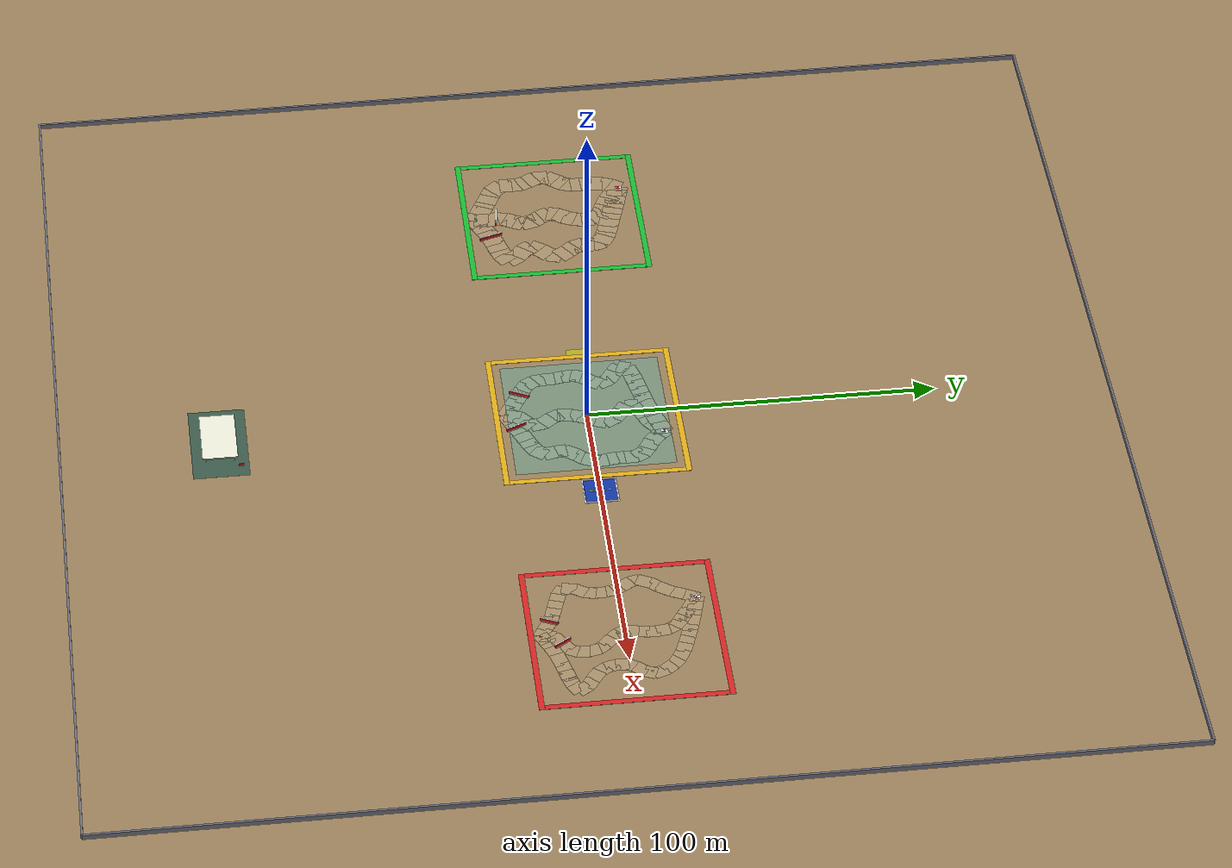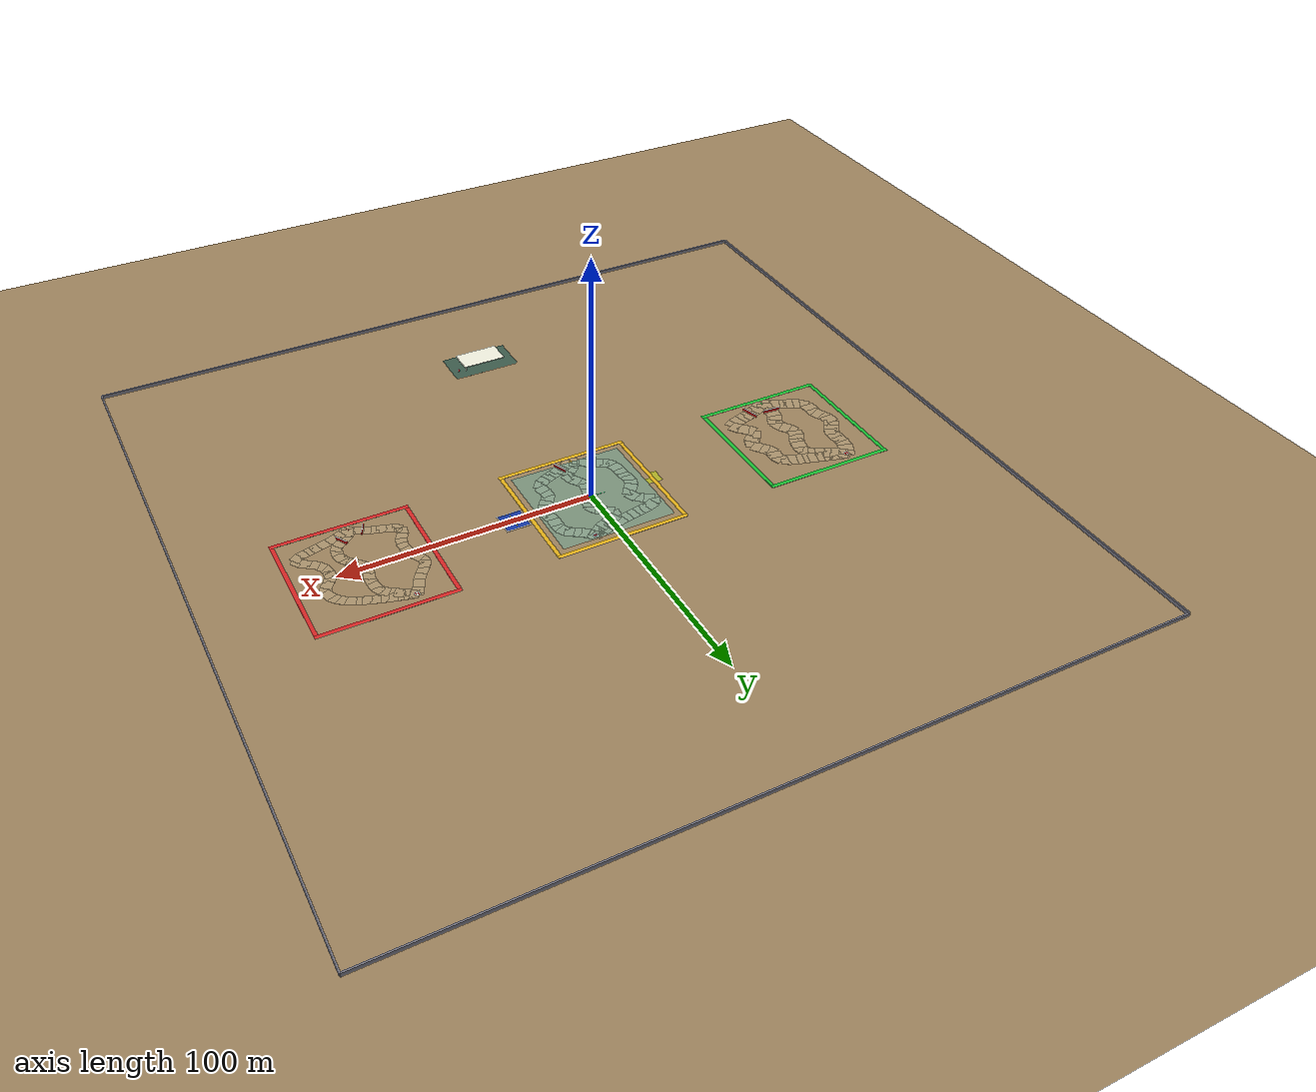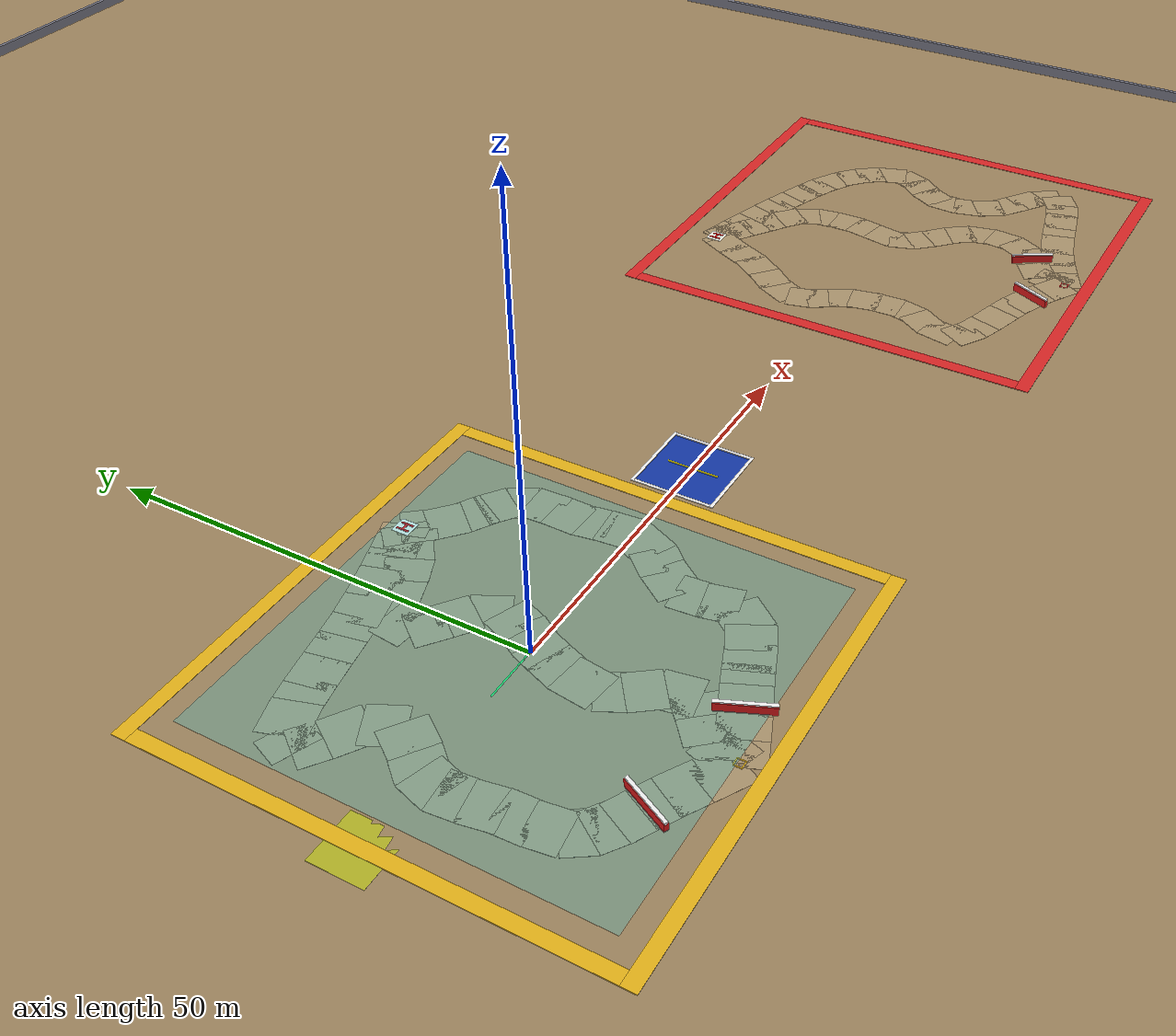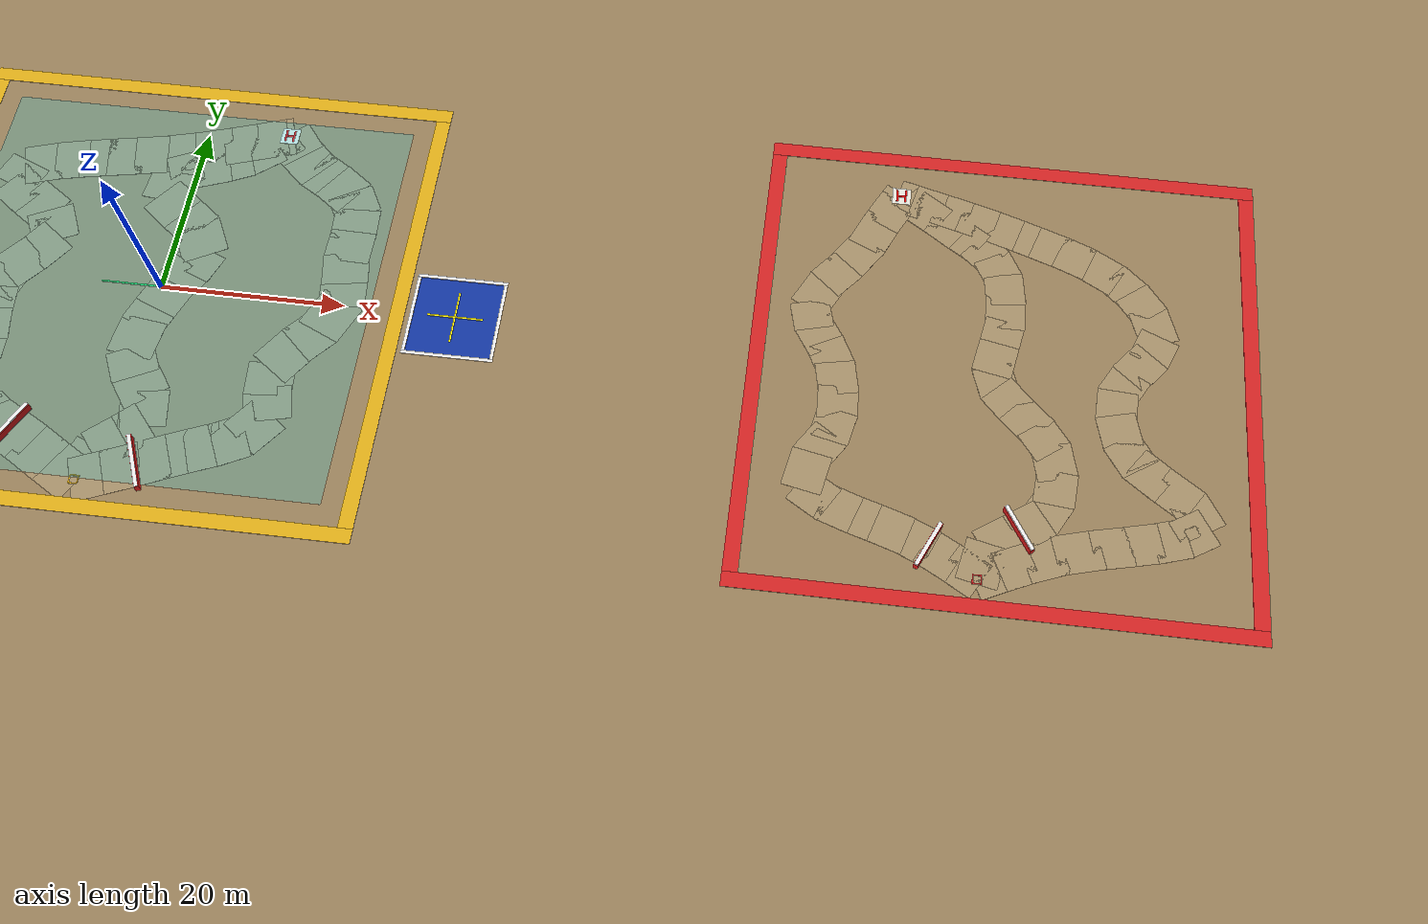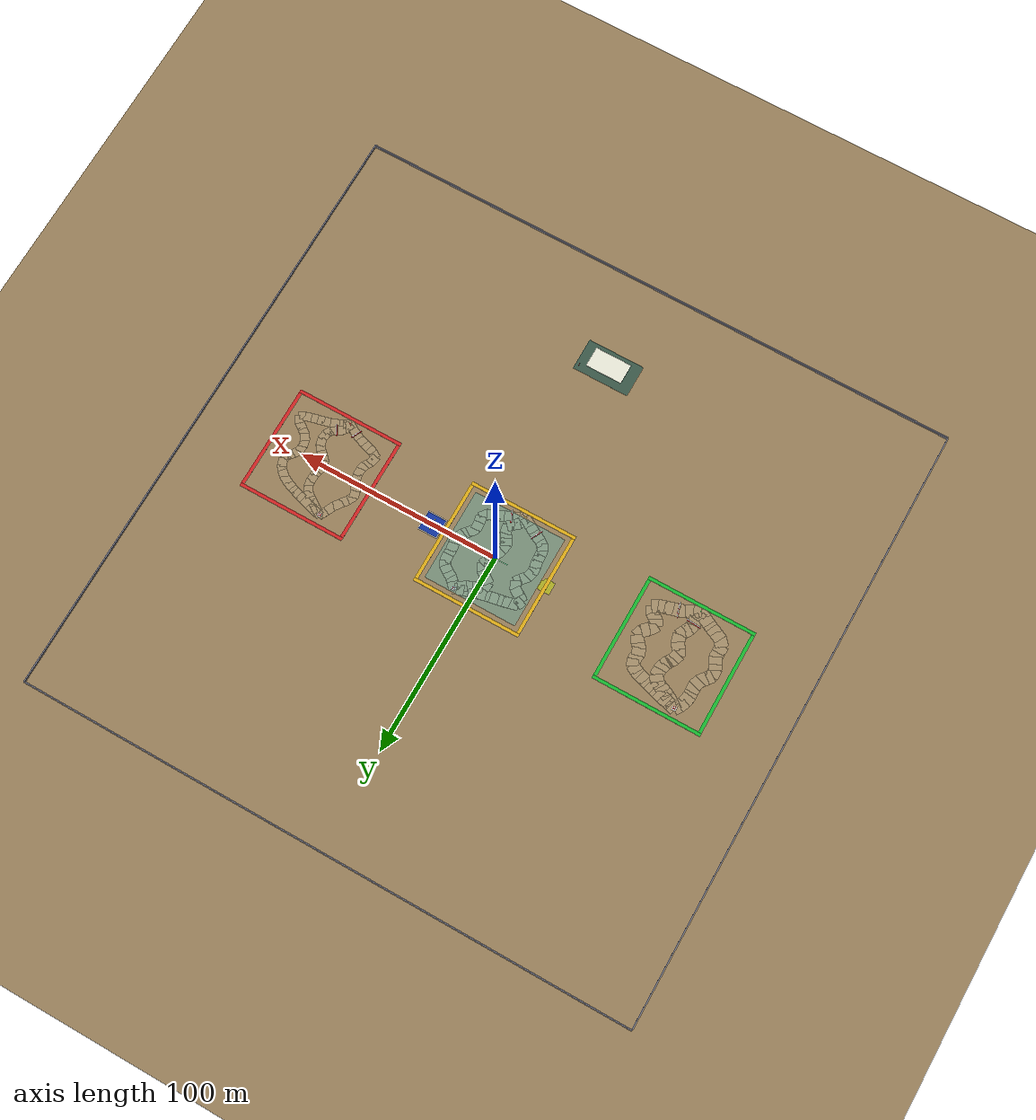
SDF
<sdf version="1.6">
 <world name="navitas_arena">
  <physics type="ode">
   <max_step_size>0.001</max_step_size>
   <real_time_factor>1</real_time_factor>
   <real_time_update_rate>1000</real_time_update_rate>
   <gravity>0 0 -9.8</gravity>
  </physics>
  <wind><linear_velocity>0.0 0.0 0.0</linear_velocity></wind>
  <scene>
   <ambient>0.275 0.275 0.275 1.0</ambient>
   <background>0.75 0.8 0.85 1.0</background>
   <shadows>true</shadows>
  </scene>
  <light name="sun" type="directional">
   <pose>0 0 120 0 -0 0</pose>
   <diffuse>0.9 0.9 0.85 1</diffuse>
   <specular>0.1 0.1 0.1 1</specular>
   <attenuation>
    <range>1200</range>
    <constant>0.9</constant>
    <linear>0.01</linear>
    <quadratic>0.001</quadratic>
   </attenuation>
   <direction>-0.4 0.2 -0.9</direction>
  </light>
  <model name="ground_plane">
   <static>true</static>
   <link name="link">
    <collision name="collision">
     <geometry><plane><normal>0 0 1</normal><size>400 400</size></plane></geometry>
     <surface><friction><ode><mu>0.800</mu><mu2>0.800</mu2></ode></friction></surface>
    </collision>
    <visual name="visual">
     <cast_shadows>false</cast_shadows>
     <geometry><plane><normal>0 0 1</normal><size>400 400</size></plane></geometry>
     <material>
      <ambient>0.62 0.52 0.37 1</ambient>
      <diffuse>0.62 0.52 0.37 1</diffuse>
      <specular>0.04 0.04 0.04 1</specular>
     </material>
    </visual>
   </link>
  </model>
  <model name="ub_N">
   <static>true</static>
   <pose>0.000 150.000 0.750 0 0 0.000</pose>
   <link name="link">
    <collision name="col"><geometry><box><size>300.000 0.600 1.500</size></box></geometry></collision>
    <visual name="vis">
     <geometry><box><size>300.000 0.600 1.500</size></box></geometry>
     <material>
      <ambient>0.45 0.45 0.50 1</ambient>
      <diffuse>0.45 0.45 0.50 1</diffuse>
      <specular>0.04 0.04 0.04 1</specular>
     </material>
    </visual>
   </link>
  </model>
  <model name="ub_S">
   <static>true</static>
   <pose>0.000 -150.000 0.750 0 0 0.000</pose>
   <link name="link">
    <collision name="col"><geometry><box><size>300.000 0.600 1.500</size></box></geometry></collision>
    <visual name="vis">
     <geometry><box><size>300.000 0.600 1.500</size></box></geometry>
     <material>
      <ambient>0.45 0.45 0.50 1</ambient>
      <diffuse>0.45 0.45 0.50 1</diffuse>
      <specular>0.04 0.04 0.04 1</specular>
     </material>
    </visual>
   </link>
  </model>
  <model name="ub_W">
   <static>true</static>
   <pose>-150.000 0.000 0.750 0 0 0.000</pose>
   <link name="link">
    <collision name="col"><geometry><box><size>0.600 300.000 1.500</size></box></geometry></collision>
    <visual name="vis">
     <geometry><box><size>0.600 300.000 1.500</size></box></geometry>
     <material>
      <ambient>0.45 0.45 0.50 1</ambient>
      <diffuse>0.45 0.45 0.50 1</diffuse>
      <specular>0.04 0.04 0.04 1</specular>
     </material>
    </visual>
   </link>
  </model>
  <model name="ub_E">
   <static>true</static>
   <pose>150.000 0.000 0.750 0 0 0.000</pose>
   <link name="link">
    <collision name="col"><geometry><box><size>0.600 300.000 1.500</size></box></geometry></collision>
    <visual name="vis">
     <geometry><box><size>0.600 300.000 1.500</size></box></geometry>
     <material>
      <ambient>0.45 0.45 0.50 1</ambient>
      <diffuse>0.45 0.45 0.50 1</diffuse>
      <specular>0.04 0.04 0.04 1</specular>
     </material>
    </visual>
   </link>
  </model>
  <model name="judge_camp_floor">
   <static>true</static>
   <pose>0.000 -105.000 0.010 0 0 0.000</pose>
   <link name="link">
    <collision name="col"><geometry><box><size>28.000 16.000 0.020</size></box></geometry></collision>
    <visual name="vis">
     <geometry><box><size>28.000 16.000 0.020</size></box></geometry>
     <material>
      <ambient>0.24 0.36 0.30 1</ambient>
      <diffuse>0.24 0.36 0.30 1</diffuse>
      <specular>0.04 0.04 0.04 1</specular>
     </material>
    </visual>
   </link>
  </model>
  <model name="judge_tent_roof">
   <static>true</static>
   <pose>0.000 -105.000 2.600 0 0 0.000</pose>
   <link name="link">
    <collision name="col"><geometry><box><size>18.000 10.000 0.350</size></box></geometry></collision>
    <visual name="vis">
     <geometry><box><size>18.000 10.000 0.350</size></box></geometry>
     <material>
      <ambient>0.95 0.95 0.88 1</ambient>
      <diffuse>0.95 0.95 0.88 1</diffuse>
      <specular>0.04 0.04 0.04 1</specular>
     </material>
    </visual>
   </link>
  </model>
  <model name="judge_tent_pole_1">
   <static>true</static>
   <pose>-8.000 -109.000 1.200 0 0 0.000</pose>
   <link name="link">
    <collision name="col"><geometry><box><size>0.180 0.180 2.400</size></box></geometry></collision>
    <visual name="vis">
     <geometry><box><size>0.180 0.180 2.400</size></box></geometry>
     <material>
      <ambient>0.85 0.85 0.80 1</ambient>
      <diffuse>0.85 0.85 0.80 1</diffuse>
      <specular>0.04 0.04 0.04 1</specular>
     </material>
    </visual>
   </link>
  </model>
  <model name="judge_tent_pole_2">
   <static>true</static>
   <pose>8.000 -109.000 1.200 0 0 0.000</pose>
   <link name="link">
    <collision name="col"><geometry><box><size>0.180 0.180 2.400</size></box></geometry></collision>
    <visual name="vis">
     <geometry><box><size>0.180 0.180 2.400</size></box></geometry>
     <material>
      <ambient>0.85 0.85 0.80 1</ambient>
      <diffuse>0.85 0.85 0.80 1</diffuse>
      <specular>0.04 0.04 0.04 1</specular>
     </material>
    </visual>
   </link>
  </model>
  <model name="judge_tent_pole_3">
   <static>true</static>
   <pose>-8.000 -101.000 1.200 0 0 0.000</pose>
   <link name="link">
    <collision name="col"><geometry><box><size>0.180 0.180 2.400</size></box></geometry></collision>
    <visual name="vis">
     <geometry><box><size>0.180 0.180 2.400</size></box></geometry>
     <material>
      <ambient>0.85 0.85 0.80 1</ambient>
      <diffuse>0.85 0.85 0.80 1</diffuse>
      <specular>0.04 0.04 0.04 1</specular>
     </material>
    </visual>
   </link>
  </model>
  <model name="judge_tent_pole_4">
   <static>true</static>
   <pose>8.000 -101.000 1.200 0 0 0.000</pose>
   <link name="link">
    <collision name="col"><geometry><box><size>0.180 0.180 2.400</size></box></geometry></collision>
    <visual name="vis">
     <geometry><box><size>0.180 0.180 2.400</size></box></geometry>
     <material>
      <ambient>0.85 0.85 0.80 1</ambient>
      <diffuse>0.85 0.85 0.80 1</diffuse>
      <specular>0.04 0.04 0.04 1</specular>
     </material>
    </visual>
   </link>
  </model>
  <model name="judge_table">
   <static>true</static>
   <pose>0.000 -105.000 0.450 0 0 0.000</pose>
   <link name="link">
    <collision name="col"><geometry><box><size>5.000 1.400 0.250</size></box></geometry></collision>
    <visual name="vis">
     <geometry><box><size>5.000 1.400 0.250</size></box></geometry>
     <material>
      <ambient>0.28 0.18 0.12 1</ambient>
      <diffuse>0.28 0.18 0.12 1</diffuse>
      <specular>0.04 0.04 0.04 1</specular>
     </material>
    </visual>
   </link>
  </model>
  <model name="judge_monitor_1">
   <static>true</static>
   <pose>-1.400 -104.750 0.950 0 0 0.000</pose>
   <link name="link">
    <collision name="col"><geometry><box><size>1.000 0.120 0.650</size></box></geometry></collision>
    <visual name="vis">
     <geometry><box><size>1.000 0.120 0.650</size></box></geometry>
     <material>
      <ambient>0.02 0.02 0.03 1</ambient>
      <diffuse>0.02 0.02 0.03 1</diffuse>
      <specular>0.04 0.04 0.04 1</specular>
     </material>
    </visual>
   </link>
  </model>
  <model name="judge_monitor_2">
   <static>true</static>
   <pose>1.400 -104.750 0.950 0 0 0.000</pose>
   <link name="link">
    <collision name="col"><geometry><box><size>1.000 0.120 0.650</size></box></geometry></collision>
    <visual name="vis">
     <geometry><box><size>1.000 0.120 0.650</size></box></geometry>
     <material>
      <ambient>0.02 0.02 0.03 1</ambient>
      <diffuse>0.02 0.02 0.03 1</diffuse>
      <specular>0.04 0.04 0.04 1</specular>
     </material>
    </visual>
   </link>
  </model>
  <model name="judge_chair_1">
   <static>true</static>
   <pose>-3.000 -107.000 0.350 0 0 0.000</pose>
   <link name="link">
    <collision name="col"><geometry><box><size>0.900 0.900 0.250</size></box></geometry></collision>
    <visual name="vis">
     <geometry><box><size>0.900 0.900 0.250</size></box></geometry>
     <material>
      <ambient>0.16 0.16 0.16 1</ambient>
      <diffuse>0.16 0.16 0.16 1</diffuse>
      <specular>0.04 0.04 0.04 1</specular>
     </material>
    </visual>
   </link>
  </model>
  <model name="judge_chair_2">
   <static>true</static>
   <pose>0.000 -107.000 0.350 0 0 0.000</pose>
   <link name="link">
    <collision name="col"><geometry><box><size>0.900 0.900 0.250</size></box></geometry></collision>
    <visual name="vis">
     <geometry><box><size>0.900 0.900 0.250</size></box></geometry>
     <material>
      <ambient>0.16 0.16 0.16 1</ambient>
      <diffuse>0.16 0.16 0.16 1</diffuse>
      <specular>0.04 0.04 0.04 1</specular>
     </material>
    </visual>
   </link>
  </model>
  <model name="judge_chair_3">
   <static>true</static>
   <pose>3.000 -107.000 0.350 0 0 0.000</pose>
   <link name="link">
    <collision name="col"><geometry><box><size>0.900 0.900 0.250</size></box></geometry></collision>
    <visual name="vis">
     <geometry><box><size>0.900 0.900 0.250</size></box></geometry>
     <material>
      <ambient>0.16 0.16 0.16 1</ambient>
      <diffuse>0.16 0.16 0.16 1</diffuse>
      <specular>0.04 0.04 0.04 1</specular>
     </material>
    </visual>
   </link>
  </model>
  <model name="judge_flag">
   <static>true</static>
   <pose>12.000 -100.000 1.400 0 0 0.000</pose>
   <link name="link">
    <collision name="col"><geometry><box><size>0.120 0.120 2.800</size></box></geometry></collision>
    <visual name="vis">
     <geometry><box><size>0.120 0.120 2.800</size></box></geometry>
     <material>
      <ambient>0.85 0.85 0.85 1</ambient>
      <diffuse>0.85 0.85 0.85 1</diffuse>
      <specular>0.04 0.04 0.04 1</specular>
     </material>
    </visual>
   </link>
  </model>
  <model name="judge_flag_panel">
   <static>true</static>
   <pose>12.000 -99.200 2.300 0 0 0.000</pose>
   <link name="link">
    <collision name="col"><geometry><box><size>0.080 1.400 0.800</size></box></geometry></collision>
    <visual name="vis">
     <geometry><box><size>0.080 1.400 0.800</size></box></geometry>
     <material>
      <ambient>0.90 0.10 0.10 1</ambient>
      <diffuse>0.90 0.10 0.10 1</diffuse>
      <specular>0.04 0.04 0.04 1</specular>
     </material>
    </visual>
   </link>
  </model>
  <model name="landing">
   <static>true</static>
   <pose>32.000 0.000 0.010 0 0 0.000</pose>
   <link name="link">
    <collision name="col"><geometry><box><size>9.000 9.000 0.020</size></box></geometry></collision>
    <visual name="vis">
     <geometry><box><size>9.000 9.000 0.020</size></box></geometry>
     <material>
      <ambient>0.08 0.22 0.65 1</ambient>
      <diffuse>0.08 0.22 0.65 1</diffuse>
      <specular>0.04 0.04 0.04 1</specular>
     </material>
    </visual>
   </link>
  </model>
  <model name="landing_border_n">
   <static>true</static>
   <pose>32.000 4.700 0.080 0 0 0.000</pose>
   <link name="link">
    <collision name="col"><geometry><box><size>9.800 0.350 0.080</size></box></geometry></collision>
    <visual name="vis">
     <geometry><box><size>9.800 0.350 0.080</size></box></geometry>
     <material>
      <ambient>0.95 0.95 0.95 1</ambient>
      <diffuse>0.95 0.95 0.95 1</diffuse>
      <specular>0.04 0.04 0.04 1</specular>
     </material>
    </visual>
   </link>
  </model>
  <model name="landing_border_s">
   <static>true</static>
   <pose>32.000 -4.700 0.080 0 0 0.000</pose>
   <link name="link">
    <collision name="col"><geometry><box><size>9.800 0.350 0.080</size></box></geometry></collision>
    <visual name="vis">
     <geometry><box><size>9.800 0.350 0.080</size></box></geometry>
     <material>
      <ambient>0.95 0.95 0.95 1</ambient>
      <diffuse>0.95 0.95 0.95 1</diffuse>
      <specular>0.04 0.04 0.04 1</specular>
     </material>
    </visual>
   </link>
  </model>
  <model name="landing_border_w">
   <static>true</static>
   <pose>27.300 0.000 0.080 0 0 0.000</pose>
   <link name="link">
    <collision name="col"><geometry><box><size>0.350 9.000 0.080</size></box></geometry></collision>
    <visual name="vis">
     <geometry><box><size>0.350 9.000 0.080</size></box></geometry>
     <material>
      <ambient>0.95 0.95 0.95 1</ambient>
      <diffuse>0.95 0.95 0.95 1</diffuse>
      <specular>0.04 0.04 0.04 1</specular>
     </material>
    </visual>
   </link>
  </model>
  <model name="landing_border_e">
   <static>true</static>
   <pose>36.700 0.000 0.080 0 0 0.000</pose>
   <link name="link">
    <collision name="col"><geometry><box><size>0.350 9.000 0.080</size></box></geometry></collision>
    <visual name="vis">
     <geometry><box><size>0.350 9.000 0.080</size></box></geometry>
     <material>
      <ambient>0.95 0.95 0.95 1</ambient>
      <diffuse>0.95 0.95 0.95 1</diffuse>
      <specular>0.04 0.04 0.04 1</specular>
     </material>
    </visual>
   </link>
  </model>
  <model name="landing_cross_x">
   <static>true</static>
   <pose>32.000 0.000 0.100 0 0 0.000</pose>
   <link name="link">
    <collision name="col"><geometry><box><size>6.000 0.180 0.080</size></box></geometry></collision>
    <visual name="vis">
     <geometry><box><size>6.000 0.180 0.080</size></box></geometry>
     <material>
      <ambient>1.00 0.95 0.05 1</ambient>
      <diffuse>1.00 0.95 0.05 1</diffuse>
      <specular>0.04 0.04 0.04 1</specular>
     </material>
    </visual>
   </link>
  </model>
  <model name="landing_cross_y">
   <static>true</static>
   <pose>32.000 0.000 0.100 0 0 0.000</pose>
   <link name="link">
    <collision name="col"><geometry><box><size>0.180 6.000 0.080</size></box></geometry></collision>
    <visual name="vis">
     <geometry><box><size>0.180 6.000 0.080</size></box></geometry>
     <material>
      <ambient>1.00 0.95 0.05 1</ambient>
      <diffuse>1.00 0.95 0.05 1</diffuse>
      <specular>0.04 0.04 0.04 1</specular>
     </material>
    </visual>
   </link>
  </model>
  <model name="launch">
   <static>true</static>
   <pose>-26.000 0.000 0.010 0 0 0.000</pose>
   <link name="link">
    <collision name="col"><geometry><box><size>6.000 6.000 0.020</size></box></geometry></collision>
    <visual name="vis">
     <geometry><box><size>6.000 6.000 0.020</size></box></geometry>
     <material>
      <ambient>0.70 0.70 0.15 1</ambient>
      <diffuse>0.70 0.70 0.15 1</diffuse>
      <specular>0.04 0.04 0.04 1</specular>
     </material>
    </visual>
   </link>
  </model>
  <model name="gd_kolay">
   <static>true</static>
   <pose>-90.000 0.000 0.010 0 0 0.000</pose>
   <link name="link">
    <collision name="col"><geometry><box><size>50.000 50.000 0.020</size></box></geometry></collision>
    <visual name="vis">
     <geometry><box><size>50.000 50.000 0.020</size></box></geometry>
     <material>
      <ambient>0.62 0.52 0.37 1</ambient>
      <diffuse>0.62 0.52 0.37 1</diffuse>
      <specular>0.04 0.04 0.04 1</specular>
     </material>
    </visual>
   </link>
  </model>
  <model name="grid_kolay_h0">
   <static>true</static>
   <pose>-90.000 -25.000 0.015 0 0 0.000</pose>
   <link name="link">
    <collision name="col"><geometry><box><size>50.000 0.100 0.006</size></box></geometry></collision>
    <visual name="vis">
     <geometry><box><size>50.000 0.100 0.006</size></box></geometry>
     <material>
      <ambient>0.30 0.24 0.17 1</ambient>
      <diffuse>0.30 0.24 0.17 1</diffuse>
      <specular>0.04 0.04 0.04 1</specular>
     </material>
    </visual>
   </link>
  </model>
  <model name="grid_kolay_v0">
   <static>true</static>
   <pose>-115.000 0.000 0.015 0 0 0.000</pose>
   <link name="link">
    <collision name="col"><geometry><box><size>0.100 50.000 0.006</size></box></geometry></collision>
    <visual name="vis">
     <geometry><box><size>0.100 50.000 0.006</size></box></geometry>
     <material>
      <ambient>0.30 0.24 0.17 1</ambient>
      <diffuse>0.30 0.24 0.17 1</diffuse>
      <specular>0.04 0.04 0.04 1</specular>
     </material>
    </visual>
   </link>
  </model>
  <model name="grid_kolay_h1">
   <static>true</static>
   <pose>-90.000 -20.000 0.015 0 0 0.000</pose>
   <link name="link">
    <collision name="col"><geometry><box><size>50.000 0.100 0.006</size></box></geometry></collision>
    <visual name="vis">
     <geometry><box><size>50.000 0.100 0.006</size></box></geometry>
     <material>
      <ambient>0.30 0.24 0.17 1</ambient>
      <diffuse>0.30 0.24 0.17 1</diffuse>
      <specular>0.04 0.04 0.04 1</specular>
     </material>
    </visual>
   </link>
  </model>
  <model name="grid_kolay_v1">
   <static>true</static>
   <pose>-110.000 0.000 0.015 0 0 0.000</pose>
   <link name="link">
    <collision name="col"><geometry><box><size>0.100 50.000 0.006</size></box></geometry></collision>
    <visual name="vis">
     <geometry><box><size>0.100 50.000 0.006</size></box></geometry>
     <material>
      <ambient>0.30 0.24 0.17 1</ambient>
      <diffuse>0.30 0.24 0.17 1</diffuse>
      <specular>0.04 0.04 0.04 1</specular>
     </material>
    </visual>
   </link>
  </model>
  <model name="grid_kolay_h2">
   <static>true</static>
   <pose>-90.000 -15.000 0.015 0 0 0.000</pose>
   <link name="link">
    <collision name="col"><geometry><box><size>50.000 0.100 0.006</size></box></geometry></collision>
    <visual name="vis">
     <geometry><box><size>50.000 0.100 0.006</size></box></geometry>
     <material>
      <ambient>0.30 0.24 0.17 1</ambient>
      <diffuse>0.30 0.24 0.17 1</diffuse>
      <specular>0.04 0.04 0.04 1</specular>
     </material>
    </visual>
   </link>
  </model>
  <model name="grid_kolay_v2">
   <static>true</static>
   <pose>-105.000 0.000 0.015 0 0 0.000</pose>
   <link name="link">
    <collision name="col"><geometry><box><size>0.100 50.000 0.006</size></box></geometry></collision>
    <visual name="vis">
     <geometry><box><size>0.100 50.000 0.006</size></box></geometry>
     <material>
      <ambient>0.30 0.24 0.17 1</ambient>
      <diffuse>0.30 0.24 0.17 1</diffuse>
      <specular>0.04 0.04 0.04 1</specular>
     </material>
    </visual>
   </link>
  </model>
  <model name="grid_kolay_h3">
   <static>true</static>
   <pose>-90.000 -10.000 0.015 0 0 0.000</pose>
   <link name="link">
    <collision name="col"><geometry><box><size>50.000 0.100 0.006</size></box></geometry></collision>
    <visual name="vis">
     <geometry><box><size>50.000 0.100 0.006</size></box></geometry>
     <material>
      <ambient>0.30 0.24 0.17 1</ambient>
      <diffuse>0.30 0.24 0.17 1</diffuse>
      <specular>0.04 0.04 0.04 1</specular>
     </material>
    </visual>
   </link>
  </model>
  <model name="grid_kolay_v3">
   <static>true</static>
   <pose>-100.000 0.000 0.015 0 0 0.000</pose>
   <link name="link">
    <collision name="col"><geometry><box><size>0.100 50.000 0.006</size></box></geometry></collision>
    <visual name="vis">
     <geometry><box><size>0.100 50.000 0.006</size></box></geometry>
     <material>
      <ambient>0.30 0.24 0.17 1</ambient>
      <diffuse>0.30 0.24 0.17 1</diffuse>
      <specular>0.04 0.04 0.04 1</specular>
     </material>
    </visual>
   </link>
  </model>
  <model name="grid_kolay_h4">
   <static>true</static>
   <pose>-90.000 -5.000 0.015 0 0 0.000</pose>
   <link name="link">
    <collision name="col"><geometry><box><size>50.000 0.100 0.006</size></box></geometry></collision>
    <visual name="vis">
     <geometry><box><size>50.000 0.100 0.006</size></box></geometry>
     <material>
      <ambient>0.30 0.24 0.17 1</ambient>
      <diffuse>0.30 0.24 0.17 1</diffuse>
      <specular>0.04 0.04 0.04 1</specular>
     </material>
    </visual>
   </link>
  </model>
  <model name="grid_kolay_v4">
   <static>true</static>
   <pose>-95.000 0.000 0.015 0 0 0.000</pose>
   <link name="link">
    <collision name="col"><geometry><box><size>0.100 50.000 0.006</size></box></geometry></collision>
    <visual name="vis">
     <geometry><box><size>0.100 50.000 0.006</size></box></geometry>
     <material>
      <ambient>0.30 0.24 0.17 1</ambient>
      <diffuse>0.30 0.24 0.17 1</diffuse>
      <specular>0.04 0.04 0.04 1</specular>
     </material>
    </visual>
   </link>
  </model>
  <model name="grid_kolay_h5">
   <static>true</static>
   <pose>-90.000 0.000 0.015 0 0 0.000</pose>
   <link name="link">
    <collision name="col"><geometry><box><size>50.000 0.100 0.006</size></box></geometry></collision>
    <visual name="vis">
     <geometry><box><size>50.000 0.100 0.006</size></box></geometry>
     <material>
      <ambient>0.30 0.24 0.17 1</ambient>
      <diffuse>0.30 0.24 0.17 1</diffuse>
      <specular>0.04 0.04 0.04 1</specular>
     </material>
    </visual>
   </link>
  </model>
  <model name="grid_kolay_v5">
   <static>true</static>
   <pose>-90.000 0.000 0.015 0 0 0.000</pose>
   <link name="link">
    <collision name="col"><geometry><box><size>0.100 50.000 0.006</size></box></geometry></collision>
    <visual name="vis">
     <geometry><box><size>0.100 50.000 0.006</size></box></geometry>
     <material>
      <ambient>0.30 0.24 0.17 1</ambient>
      <diffuse>0.30 0.24 0.17 1</diffuse>
      <specular>0.04 0.04 0.04 1</specular>
     </material>
    </visual>
   </link>
  </model>
  <model name="grid_kolay_h6">
   <static>true</static>
   <pose>-90.000 5.000 0.015 0 0 0.000</pose>
   <link name="link">
    <collision name="col"><geometry><box><size>50.000 0.100 0.006</size></box></geometry></collision>
    <visual name="vis">
     <geometry><box><size>50.000 0.100 0.006</size></box></geometry>
     <material>
      <ambient>0.30 0.24 0.17 1</ambient>
      <diffuse>0.30 0.24 0.17 1</diffuse>
      <specular>0.04 0.04 0.04 1</specular>
     </material>
    </visual>
   </link>
  </model>
  <model name="grid_kolay_v6">
   <static>true</static>
   <pose>-85.000 0.000 0.015 0 0 0.000</pose>
   <link name="link">
    <collision name="col"><geometry><box><size>0.100 50.000 0.006</size></box></geometry></collision>
    <visual name="vis">
     <geometry><box><size>0.100 50.000 0.006</size></box></geometry>
     <material>
      <ambient>0.30 0.24 0.17 1</ambient>
      <diffuse>0.30 0.24 0.17 1</diffuse>
      <specular>0.04 0.04 0.04 1</specular>
     </material>
    </visual>
   </link>
  </model>
  <model name="grid_kolay_h7">
   <static>true</static>
   <pose>-90.000 10.000 0.015 0 0 0.000</pose>
   <link name="link">
    <collision name="col"><geometry><box><size>50.000 0.100 0.006</size></box></geometry></collision>
    <visual name="vis">
     <geometry><box><size>50.000 0.100 0.006</size></box></geometry>
     <material>
      <ambient>0.30 0.24 0.17 1</ambient>
      <diffuse>0.30 0.24 0.17 1</diffuse>
      <specular>0.04 0.04 0.04 1</specular>
     </material>
    </visual>
   </link>
  </model>
  <model name="grid_kolay_v7">
   <static>true</static>
   <pose>-80.000 0.000 0.015 0 0 0.000</pose>
   <link name="link">
    <collision name="col"><geometry><box><size>0.100 50.000 0.006</size></box></geometry></collision>
    <visual name="vis">
     <geometry><box><size>0.100 50.000 0.006</size></box></geometry>
     <material>
      <ambient>0.30 0.24 0.17 1</ambient>
      <diffuse>0.30 0.24 0.17 1</diffuse>
      <specular>0.04 0.04 0.04 1</specular>
     </material>
    </visual>
   </link>
  </model>
  <model name="grid_kolay_h8">
   <static>true</static>
   <pose>-90.000 15.000 0.015 0 0 0.000</pose>
   <link name="link">
    <collision name="col"><geometry><box><size>50.000 0.100 0.006</size></box></geometry></collision>
    <visual name="vis">
     <geometry><box><size>50.000 0.100 0.006</size></box></geometry>
     <material>
      <ambient>0.30 0.24 0.17 1</ambient>
      <diffuse>0.30 0.24 0.17 1</diffuse>
      <specular>0.04 0.04 0.04 1</specular>
     </material>
    </visual>
   </link>
  </model>
  <model name="grid_kolay_v8">
   <static>true</static>
   <pose>-75.000 0.000 0.015 0 0 0.000</pose>
   <link name="link">
    <collision name="col"><geometry><box><size>0.100 50.000 0.006</size></box></geometry></collision>
    <visual name="vis">
     <geometry><box><size>0.100 50.000 0.006</size></box></geometry>
     <material>
      <ambient>0.30 0.24 0.17 1</ambient>
      <diffuse>0.30 0.24 0.17 1</diffuse>
      <specular>0.04 0.04 0.04 1</specular>
     </material>
    </visual>
   </link>
  </model>
  <model name="grid_kolay_h9">
   <static>true</static>
   <pose>-90.000 20.000 0.015 0 0 0.000</pose>
   <link name="link">
    <collision name="col"><geometry><box><size>50.000 0.100 0.006</size></box></geometry></collision>
    <visual name="vis">
     <geometry><box><size>50.000 0.100 0.006</size></box></geometry>
     <material>
      <ambient>0.30 0.24 0.17 1</ambient>
      <diffuse>0.30 0.24 0.17 1</diffuse>
      <specular>0.04 0.04 0.04 1</specular>
     </material>
    </visual>
   </link>
  </model>
  <model name="grid_kolay_v9">
   <static>true</static>
   <pose>-70.000 0.000 0.015 0 0 0.000</pose>
   <link name="link">
    <collision name="col"><geometry><box><size>0.100 50.000 0.006</size></box></geometry></collision>
    <visual name="vis">
     <geometry><box><size>0.100 50.000 0.006</size></box></geometry>
     <material>
      <ambient>0.30 0.24 0.17 1</ambient>
      <diffuse>0.30 0.24 0.17 1</diffuse>
      <specular>0.04 0.04 0.04 1</specular>
     </material>
    </visual>
   </link>
  </model>
  <model name="grid_kolay_h10">
   <static>true</static>
   <pose>-90.000 25.000 0.015 0 0 0.000</pose>
   <link name="link">
    <collision name="col"><geometry><box><size>50.000 0.100 0.006</size></box></geometry></collision>
    <visual name="vis">
     <geometry><box><size>50.000 0.100 0.006</size></box></geometry>
     <material>
      <ambient>0.30 0.24 0.17 1</ambient>
      <diffuse>0.30 0.24 0.17 1</diffuse>
      <specular>0.04 0.04 0.04 1</specular>
     </material>
    </visual>
   </link>
  </model>
  <model name="grid_kolay_v10">
   <static>true</static>
   <pose>-65.000 0.000 0.015 0 0 0.000</pose>
   <link name="link">
    <collision name="col"><geometry><box><size>0.100 50.000 0.006</size></box></geometry></collision>
    <visual name="vis">
     <geometry><box><size>0.100 50.000 0.006</size></box></geometry>
     <material>
      <ambient>0.30 0.24 0.17 1</ambient>
      <diffuse>0.30 0.24 0.17 1</diffuse>
      <specular>0.04 0.04 0.04 1</specular>
     </material>
    </visual>
   </link>
  </model>
  <model name="brd_kolay_N">
   <static>true</static>
   <pose>-90.000 25.800 0.040 0 0 0.000</pose>
   <link name="link">
    <collision name="col"><geometry><box><size>53.200 1.600 0.080</size></box></geometry></collision>
    <visual name="vis">
     <geometry><box><size>53.200 1.600 0.080</size></box></geometry>
     <material>
      <ambient>0.10 0.75 0.20 1</ambient>
      <diffuse>0.10 0.75 0.20 1</diffuse>
      <specular>0.04 0.04 0.04 1</specular>
     </material>
    </visual>
   </link>
  </model>
  <model name="brd_kolay_S">
   <static>true</static>
   <pose>-90.000 -25.800 0.040 0 0 0.000</pose>
   <link name="link">
    <collision name="col"><geometry><box><size>53.200 1.600 0.080</size></box></geometry></collision>
    <visual name="vis">
     <geometry><box><size>53.200 1.600 0.080</size></box></geometry>
     <material>
      <ambient>0.10 0.75 0.20 1</ambient>
      <diffuse>0.10 0.75 0.20 1</diffuse>
      <specular>0.04 0.04 0.04 1</specular>
     </material>
    </visual>
   </link>
  </model>
  <model name="brd_kolay_W">
   <static>true</static>
   <pose>-115.800 0.000 0.040 0 0 0.000</pose>
   <link name="link">
    <collision name="col"><geometry><box><size>1.600 50.000 0.080</size></box></geometry></collision>
    <visual name="vis">
     <geometry><box><size>1.600 50.000 0.080</size></box></geometry>
     <material>
      <ambient>0.10 0.75 0.20 1</ambient>
      <diffuse>0.10 0.75 0.20 1</diffuse>
      <specular>0.04 0.04 0.04 1</specular>
     </material>
    </visual>
   </link>
  </model>
  <model name="brd_kolay_E">
   <static>true</static>
   <pose>-64.200 0.000 0.040 0 0 0.000</pose>
   <link name="link">
    <collision name="col"><geometry><box><size>1.600 50.000 0.080</size></box></geometry></collision>
    <visual name="vis">
     <geometry><box><size>1.600 50.000 0.080</size></box></geometry>
     <material>
      <ambient>0.10 0.75 0.20 1</ambient>
      <diffuse>0.10 0.75 0.20 1</diffuse>
      <specular>0.04 0.04 0.04 1</specular>
     </material>
    </visual>
   </link>
  </model>
  <model name="road_kolay_1_0">
   <static>true</static>
   <pose>-92.110 -22.266 0.040 0 0 2.681</pose>
   <link name="link">
    <collision name="col"><geometry><box><size>4.201 6.000 0.020</size></box></geometry></collision>
    <visual name="vis">
     <geometry><box><size>4.201 6.000 0.020</size></box></geometry>
     <material>
      <ambient>0.67 0.58 0.43 1</ambient>
      <diffuse>0.67 0.58 0.43 1</diffuse>
      <specular>0.04 0.04 0.04 1</specular>
     </material>
    </visual>
   </link>
  </model>
  <model name="road_kolay_1_1">
   <static>true</static>
   <pose>-94.920 -20.856 0.040 0 0 2.672</pose>
   <link name="link">
    <collision name="col"><geometry><box><size>3.885 6.000 0.020</size></box></geometry></collision>
    <visual name="vis">
     <geometry><box><size>3.885 6.000 0.020</size></box></geometry>
     <material>
      <ambient>0.67 0.58 0.43 1</ambient>
      <diffuse>0.67 0.58 0.43 1</diffuse>
      <specular>0.04 0.04 0.04 1</specular>
     </material>
    </visual>
   </link>
  </model>
  <model name="road_kolay_1_2">
   <static>true</static>
   <pose>-97.476 -19.557 0.040 0 0 2.670</pose>
   <link name="link">
    <collision name="col"><geometry><box><size>3.650 6.000 0.020</size></box></geometry></collision>
    <visual name="vis">
     <geometry><box><size>3.650 6.000 0.020</size></box></geometry>
     <material>
      <ambient>0.67 0.58 0.43 1</ambient>
      <diffuse>0.67 0.58 0.43 1</diffuse>
      <specular>0.04 0.04 0.04 1</specular>
     </material>
    </visual>
   </link>
  </model>
  <model name="road_kolay_1_3">
   <static>true</static>
   <pose>-99.999 -18.352 0.040 0 0 2.722</pose>
   <link name="link">
    <collision name="col"><geometry><box><size>3.744 6.000 0.020</size></box></geometry></collision>
    <visual name="vis">
     <geometry><box><size>3.744 6.000 0.020</size></box></geometry>
     <material>
      <ambient>0.67 0.58 0.43 1</ambient>
      <diffuse>0.67 0.58 0.43 1</diffuse>
      <specular>0.04 0.04 0.04 1</specular>
     </material>
    </visual>
   </link>
  </model>
  <model name="road_kolay_1_4">
   <static>true</static>
   <pose>-102.541 -17.135 0.040 0 0 2.668</pose>
   <link name="link">
    <collision name="col"><geometry><box><size>3.696 6.000 0.020</size></box></geometry></collision>
    <visual name="vis">
     <geometry><box><size>3.696 6.000 0.020</size></box></geometry>
     <material>
      <ambient>0.67 0.58 0.43 1</ambient>
      <diffuse>0.67 0.58 0.43 1</diffuse>
      <specular>0.04 0.04 0.04 1</specular>
     </material>
    </visual>
   </link>
  </model>
  <model name="road_kolay_1_5">
   <static>true</static>
   <pose>-104.956 -15.129 0.040 0 0 2.279</pose>
   <link name="link">
    <collision name="col"><geometry><box><size>4.502 6.000 0.020</size></box></geometry></collision>
    <visual name="vis">
     <geometry><box><size>4.502 6.000 0.020</size></box></geometry>
     <material>
      <ambient>0.67 0.58 0.43 1</ambient>
      <diffuse>0.67 0.58 0.43 1</diffuse>
      <specular>0.04 0.04 0.04 1</specular>
     </material>
    </visual>
   </link>
  </model>
  <model name="road_kolay_1_6">
   <static>true</static>
   <pose>-106.126 -12.340 0.040 0 0 1.570</pose>
   <link name="link">
    <collision name="col"><geometry><box><size>3.740 6.000 0.020</size></box></geometry></collision>
    <visual name="vis">
     <geometry><box><size>3.740 6.000 0.020</size></box></geometry>
     <material>
      <ambient>0.67 0.58 0.43 1</ambient>
      <diffuse>0.67 0.58 0.43 1</diffuse>
      <specular>0.04 0.04 0.04 1</specular>
     </material>
    </visual>
   </link>
  </model>
  <model name="road_kolay_1_7">
   <static>true</static>
   <pose>-106.145 -9.460 0.040 0 0 1.585</pose>
   <link name="link">
    <collision name="col"><geometry><box><size>3.820 6.000 0.020</size></box></geometry></collision>
    <visual name="vis">
     <geometry><box><size>3.820 6.000 0.020</size></box></geometry>
     <material>
      <ambient>0.67 0.58 0.43 1</ambient>
      <diffuse>0.67 0.58 0.43 1</diffuse>
      <specular>0.04 0.04 0.04 1</specular>
     </material>
    </visual>
   </link>
  </model>
  <model name="road_kolay_1_8">
   <static>true</static>
   <pose>-106.685 -6.833 0.040 0 0 1.989</pose>
   <link name="link">
    <collision name="col"><geometry><box><size>3.454 6.000 0.020</size></box></geometry></collision>
    <visual name="vis">
     <geometry><box><size>3.454 6.000 0.020</size></box></geometry>
     <material>
      <ambient>0.67 0.58 0.43 1</ambient>
      <diffuse>0.67 0.58 0.43 1</diffuse>
      <specular>0.04 0.04 0.04 1</specular>
     </material>
    </visual>
   </link>
  </model>
  <model name="road_kolay_1_9">
   <static>true</static>
   <pose>-107.845 -4.500 0.040 0 0 2.073</pose>
   <link name="link">
    <collision name="col"><geometry><box><size>3.562 6.000 0.020</size></box></geometry></collision>
    <visual name="vis">
     <geometry><box><size>3.562 6.000 0.020</size></box></geometry>
     <material>
      <ambient>0.67 0.58 0.43 1</ambient>
      <diffuse>0.67 0.58 0.43 1</diffuse>
      <specular>0.04 0.04 0.04 1</specular>
     </material>
    </visual>
   </link>
  </model>
  <model name="road_kolay_1_10">
   <static>true</static>
   <pose>-108.529 -1.583 0.040 0 0 1.596</pose>
   <link name="link">
    <collision name="col"><geometry><box><size>4.401 6.000 0.020</size></box></geometry></collision>
    <visual name="vis">
     <geometry><box><size>4.401 6.000 0.020</size></box></geometry>
     <material>
      <ambient>0.67 0.58 0.43 1</ambient>
      <diffuse>0.67 0.58 0.43 1</diffuse>
      <specular>0.04 0.04 0.04 1</specular>
     </material>
    </visual>
   </link>
  </model>
  <model name="road_kolay_1_11">
   <static>true</static>
   <pose>-107.723 1.333 0.040 0 0 0.941</pose>
   <link name="link">
    <collision name="col"><geometry><box><size>3.787 6.000 0.020</size></box></geometry></collision>
    <visual name="vis">
     <geometry><box><size>3.787 6.000 0.020</size></box></geometry>
     <material>
      <ambient>0.67 0.58 0.43 1</ambient>
      <diffuse>0.67 0.58 0.43 1</diffuse>
      <specular>0.04 0.04 0.04 1</specular>
     </material>
    </visual>
   </link>
  </model>
  <model name="road_kolay_1_12">
   <static>true</static>
   <pose>-105.942 3.667 0.040 0 0 0.897</pose>
   <link name="link">
    <collision name="col"><geometry><box><size>3.885 6.000 0.020</size></box></geometry></collision>
    <visual name="vis">
     <geometry><box><size>3.885 6.000 0.020</size></box></geometry>
     <material>
      <ambient>0.67 0.58 0.43 1</ambient>
      <diffuse>0.67 0.58 0.43 1</diffuse>
      <specular>0.04 0.04 0.04 1</specular>
     </material>
    </visual>
   </link>
  </model>
  <model name="road_kolay_1_13">
   <static>true</static>
   <pose>-104.572 6.137 0.040 0 0 1.245</pose>
   <link name="link">
    <collision name="col"><geometry><box><size>3.651 6.000 0.020</size></box></geometry></collision>
    <visual name="vis">
     <geometry><box><size>3.651 6.000 0.020</size></box></geometry>
     <material>
      <ambient>0.67 0.58 0.43 1</ambient>
      <diffuse>0.67 0.58 0.43 1</diffuse>
      <specular>0.04 0.04 0.04 1</specular>
     </material>
    </visual>
   </link>
  </model>
  <model name="road_kolay_1_14">
   <static>true</static>
   <pose>-104.165 8.910 0.040 0 0 1.593</pose>
   <link name="link">
    <collision name="col"><geometry><box><size>3.841 6.000 0.020</size></box></geometry></collision>
    <visual name="vis">
     <geometry><box><size>3.841 6.000 0.020</size></box></geometry>
     <material>
      <ambient>0.67 0.58 0.43 1</ambient>
      <diffuse>0.67 0.58 0.43 1</diffuse>
      <specular>0.04 0.04 0.04 1</specular>
     </material>
    </visual>
   </link>
  </model>
  <model name="road_kolay_1_15">
   <static>true</static>
   <pose>-104.246 11.690 0.040 0 0 1.609</pose>
   <link name="link">
    <collision name="col"><geometry><box><size>3.522 6.000 0.020</size></box></geometry></collision>
    <visual name="vis">
     <geometry><box><size>3.522 6.000 0.020</size></box></geometry>
     <material>
      <ambient>0.67 0.58 0.43 1</ambient>
      <diffuse>0.67 0.58 0.43 1</diffuse>
      <specular>0.04 0.04 0.04 1</specular>
     </material>
    </visual>
   </link>
  </model>
  <model name="road_kolay_1_16">
   <static>true</static>
   <pose>-104.036 14.583 0.040 0 0 1.408</pose>
   <link name="link">
    <collision name="col"><geometry><box><size>4.109 6.000 0.020</size></box></geometry></collision>
    <visual name="vis">
     <geometry><box><size>4.109 6.000 0.020</size></box></geometry>
     <material>
      <ambient>0.67 0.58 0.43 1</ambient>
      <diffuse>0.67 0.58 0.43 1</diffuse>
      <specular>0.04 0.04 0.04 1</specular>
     </material>
    </visual>
   </link>
  </model>
  <model name="road_kolay_1_17">
   <static>true</static>
   <pose>-103.196 17.519 0.040 0 0 1.166</pose>
   <link name="link">
    <collision name="col"><geometry><box><size>3.842 6.000 0.020</size></box></geometry></collision>
    <visual name="vis">
     <geometry><box><size>3.842 6.000 0.020</size></box></geometry>
     <material>
      <ambient>0.67 0.58 0.43 1</ambient>
      <diffuse>0.67 0.58 0.43 1</diffuse>
      <specular>0.04 0.04 0.04 1</specular>
     </material>
    </visual>
   </link>
  </model>
  <model name="road_kolay_1_18">
   <static>true</static>
   <pose>-101.885 19.935 0.040 0 0 0.969</pose>
   <link name="link">
    <collision name="col"><geometry><box><size>3.484 6.000 0.020</size></box></geometry></collision>
    <visual name="vis">
     <geometry><box><size>3.484 6.000 0.020</size></box></geometry>
     <material>
      <ambient>0.67 0.58 0.43 1</ambient>
      <diffuse>0.67 0.58 0.43 1</diffuse>
      <specular>0.04 0.04 0.04 1</specular>
     </material>
    </visual>
   </link>
  </model>
  <model name="road_kolay_2_0">
   <static>true</static>
   <pose>-90.490 -21.250 0.040 0 0 1.490</pose>
   <link name="link">
    <collision name="col"><geometry><box><size>4.412 6.000 0.020</size></box></geometry></collision>
    <visual name="vis">
     <geometry><box><size>4.412 6.000 0.020</size></box></geometry>
     <material>
      <ambient>0.67 0.58 0.43 1</ambient>
      <diffuse>0.67 0.58 0.43 1</diffuse>
      <specular>0.04 0.04 0.04 1</specular>
     </material>
    </visual>
   </link>
  </model>
  <model name="road_kolay_2_1">
   <static>true</static>
   <pose>-90.547 -18.111 0.040 0 0 1.713</pose>
   <link name="link">
    <collision name="col"><geometry><box><size>3.706 6.000 0.020</size></box></geometry></collision>
    <visual name="vis">
     <geometry><box><size>3.706 6.000 0.020</size></box></geometry>
     <material>
      <ambient>0.67 0.58 0.43 1</ambient>
      <diffuse>0.67 0.58 0.43 1</diffuse>
      <specular>0.04 0.04 0.04 1</specular>
     </material>
    </visual>
   </link>
  </model>
  <model name="road_kolay_2_2">
   <static>true</static>
   <pose>-90.478 -15.350 0.040 0 0 1.378</pose>
   <link name="link">
    <collision name="col"><geometry><box><size>3.696 6.000 0.020</size></box></geometry></collision>
    <visual name="vis">
     <geometry><box><size>3.696 6.000 0.020</size></box></geometry>
     <material>
      <ambient>0.67 0.58 0.43 1</ambient>
      <diffuse>0.67 0.58 0.43 1</diffuse>
      <specular>0.04 0.04 0.04 1</specular>
     </material>
    </visual>
   </link>
  </model>
  <model name="road_kolay_2_3">
   <static>true</static>
   <pose>-89.535 -12.817 0.040 0 0 1.043</pose>
   <link name="link">
    <collision name="col"><geometry><box><size>3.587 6.000 0.020</size></box></geometry></collision>
    <visual name="vis">
     <geometry><box><size>3.587 6.000 0.020</size></box></geometry>
     <material>
      <ambient>0.67 0.58 0.43 1</ambient>
      <diffuse>0.67 0.58 0.43 1</diffuse>
      <specular>0.04 0.04 0.04 1</specular>
     </material>
    </visual>
   </link>
  </model>
  <model name="road_kolay_2_4">
   <static>true</static>
   <pose>-88.283 -10.426 0.040 0 0 1.133</pose>
   <link name="link">
    <collision name="col"><geometry><box><size>3.617 6.000 0.020</size></box></geometry></collision>
    <visual name="vis">
     <geometry><box><size>3.617 6.000 0.020</size></box></geometry>
     <material>
      <ambient>0.67 0.58 0.43 1</ambient>
      <diffuse>0.67 0.58 0.43 1</diffuse>
      <specular>0.04 0.04 0.04 1</specular>
     </material>
    </visual>
   </link>
  </model>
  <model name="road_kolay_2_5">
   <static>true</static>
   <pose>-88.152 -7.431 0.040 0 0 1.818</pose>
   <link name="link">
    <collision name="col"><geometry><box><size>4.540 6.000 0.020</size></box></geometry></collision>
    <visual name="vis">
     <geometry><box><size>4.540 6.000 0.020</size></box></geometry>
     <material>
      <ambient>0.67 0.58 0.43 1</ambient>
      <diffuse>0.67 0.58 0.43 1</diffuse>
      <specular>0.04 0.04 0.04 1</specular>
     </material>
    </visual>
   </link>
  </model>
  <model name="road_kolay_2_6">
   <static>true</static>
   <pose>-89.501 -4.500 0.040 0 0 2.229</pose>
   <link name="link">
    <collision name="col"><geometry><box><size>3.850 6.000 0.020</size></box></geometry></collision>
    <visual name="vis">
     <geometry><box><size>3.850 6.000 0.020</size></box></geometry>
     <material>
      <ambient>0.67 0.58 0.43 1</ambient>
      <diffuse>0.67 0.58 0.43 1</diffuse>
      <specular>0.04 0.04 0.04 1</specular>
     </material>
    </visual>
   </link>
  </model>
  <model name="road_kolay_2_7">
   <static>true</static>
   <pose>-90.909 -2.167 0.040 0 0 1.980</pose>
   <link name="link">
    <collision name="col"><geometry><box><size>3.443 6.000 0.020</size></box></geometry></collision>
    <visual name="vis">
     <geometry><box><size>3.443 6.000 0.020</size></box></geometry>
     <material>
      <ambient>0.67 0.58 0.43 1</ambient>
      <diffuse>0.67 0.58 0.43 1</diffuse>
      <specular>0.04 0.04 0.04 1</specular>
     </material>
    </visual>
   </link>
  </model>
  <model name="road_kolay_2_8">
   <static>true</static>
   <pose>-91.073 0.167 0.040 0 0 1.286</pose>
   <link name="link">
    <collision name="col"><geometry><box><size>3.331 6.000 0.020</size></box></geometry></collision>
    <visual name="vis">
     <geometry><box><size>3.331 6.000 0.020</size></box></geometry>
     <material>
      <ambient>0.67 0.58 0.43 1</ambient>
      <diffuse>0.67 0.58 0.43 1</diffuse>
      <specular>0.04 0.04 0.04 1</specular>
     </material>
    </visual>
   </link>
  </model>
  <model name="road_kolay_2_9">
   <static>true</static>
   <pose>-89.992 2.500 0.040 0 0 1.006</pose>
   <link name="link">
    <collision name="col"><geometry><box><size>3.662 6.000 0.020</size></box></geometry></collision>
    <visual name="vis">
     <geometry><box><size>3.662 6.000 0.020</size></box></geometry>
     <material>
      <ambient>0.67 0.58 0.43 1</ambient>
      <diffuse>0.67 0.58 0.43 1</diffuse>
      <specular>0.04 0.04 0.04 1</specular>
     </material>
    </visual>
   </link>
  </model>
  <model name="road_kolay_2_10">
   <static>true</static>
   <pose>-88.686 4.833 0.040 0 0 1.118</pose>
   <link name="link">
    <collision name="col"><geometry><box><size>3.494 6.000 0.020</size></box></geometry></collision>
    <visual name="vis">
     <geometry><box><size>3.494 6.000 0.020</size></box></geometry>
     <material>
      <ambient>0.67 0.58 0.43 1</ambient>
      <diffuse>0.67 0.58 0.43 1</diffuse>
      <specular>0.04 0.04 0.04 1</specular>
     </material>
    </visual>
   </link>
  </model>
  <model name="road_kolay_2_11">
   <static>true</static>
   <pose>-87.765 7.460 0.040 0 0 1.333</pose>
   <link name="link">
    <collision name="col"><geometry><box><size>3.904 6.000 0.020</size></box></geometry></collision>
    <visual name="vis">
     <geometry><box><size>3.904 6.000 0.020</size></box></geometry>
     <material>
      <ambient>0.67 0.58 0.43 1</ambient>
      <diffuse>0.67 0.58 0.43 1</diffuse>
      <specular>0.04 0.04 0.04 1</specular>
     </material>
    </visual>
   </link>
  </model>
  <model name="road_kolay_2_12">
   <static>true</static>
   <pose>-87.390 10.340 0.040 0 0 1.556</pose>
   <link name="link">
    <collision name="col"><geometry><box><size>3.740 6.000 0.020</size></box></geometry></collision>
    <visual name="vis">
     <geometry><box><size>3.740 6.000 0.020</size></box></geometry>
     <material>
      <ambient>0.67 0.58 0.43 1</ambient>
      <diffuse>0.67 0.58 0.43 1</diffuse>
      <specular>0.04 0.04 0.04 1</specular>
     </material>
    </visual>
   </link>
  </model>
  <model name="road_kolay_2_13">
   <static>true</static>
   <pose>-88.023 12.771 0.040 0 0 2.145</pose>
   <link name="link">
    <collision name="col"><geometry><box><size>3.309 6.000 0.020</size></box></geometry></collision>
    <visual name="vis">
     <geometry><box><size>3.309 6.000 0.020</size></box></geometry>
     <material>
      <ambient>0.67 0.58 0.43 1</ambient>
      <diffuse>0.67 0.58 0.43 1</diffuse>
      <specular>0.04 0.04 0.04 1</specular>
     </material>
    </visual>
   </link>
  </model>
  <model name="road_kolay_2_14">
   <static>true</static>
   <pose>-89.848 14.469 0.040 0 0 2.611</pose>
   <link name="link">
    <collision name="col"><geometry><box><size>3.613 6.000 0.020</size></box></geometry></collision>
    <visual name="vis">
     <geometry><box><size>3.613 6.000 0.020</size></box></geometry>
     <material>
      <ambient>0.67 0.58 0.43 1</ambient>
      <diffuse>0.67 0.58 0.43 1</diffuse>
      <specular>0.04 0.04 0.04 1</specular>
     </material>
    </visual>
   </link>
  </model>
  <model name="road_kolay_2_15">
   <static>true</static>
   <pose>-92.396 15.758 0.040 0 0 2.730</pose>
   <link name="link">
    <collision name="col"><geometry><box><size>3.908 6.000 0.020</size></box></geometry></collision>
    <visual name="vis">
     <geometry><box><size>3.908 6.000 0.020</size></box></geometry>
     <material>
      <ambient>0.67 0.58 0.43 1</ambient>
      <diffuse>0.67 0.58 0.43 1</diffuse>
      <specular>0.04 0.04 0.04 1</specular>
     </material>
    </visual>
   </link>
  </model>
  <model name="road_kolay_2_16">
   <static>true</static>
   <pose>-94.954 16.930 0.040 0 0 2.692</pose>
   <link name="link">
    <collision name="col"><geometry><box><size>3.521 6.000 0.020</size></box></geometry></collision>
    <visual name="vis">
     <geometry><box><size>3.521 6.000 0.020</size></box></geometry>
     <material>
      <ambient>0.67 0.58 0.43 1</ambient>
      <diffuse>0.67 0.58 0.43 1</diffuse>
      <specular>0.04 0.04 0.04 1</specular>
     </material>
    </visual>
   </link>
  </model>
  <model name="road_kolay_2_17">
   <static>true</static>
   <pose>-97.374 18.320 0.040 0 0 2.557</pose>
   <link name="link">
    <collision name="col"><geometry><box><size>3.872 6.000 0.020</size></box></geometry></collision>
    <visual name="vis">
     <geometry><box><size>3.872 6.000 0.020</size></box></geometry>
     <material>
      <ambient>0.67 0.58 0.43 1</ambient>
      <diffuse>0.67 0.58 0.43 1</diffuse>
      <specular>0.04 0.04 0.04 1</specular>
     </material>
    </visual>
   </link>
  </model>
  <model name="road_kolay_2_18">
   <static>true</static>
   <pose>-99.883 20.070 0.040 0 0 2.510</pose>
   <link name="link">
    <collision name="col"><geometry><box><size>4.048 6.000 0.020</size></box></geometry></collision>
    <visual name="vis">
     <geometry><box><size>4.048 6.000 0.020</size></box></geometry>
     <material>
      <ambient>0.67 0.58 0.43 1</ambient>
      <diffuse>0.67 0.58 0.43 1</diffuse>
      <specular>0.04 0.04 0.04 1</specular>
     </material>
    </visual>
   </link>
  </model>
  <model name="road_kolay_3_0">
   <static>true</static>
   <pose>-89.138 -22.266 0.040 0 0 0.457</pose>
   <link name="link">
    <collision name="col"><geometry><box><size>4.229 6.000 0.020</size></box></geometry></collision>
    <visual name="vis">
     <geometry><box><size>4.229 6.000 0.020</size></box></geometry>
     <material>
      <ambient>0.67 0.58 0.43 1</ambient>
      <diffuse>0.67 0.58 0.43 1</diffuse>
      <specular>0.04 0.04 0.04 1</specular>
     </material>
    </visual>
   </link>
  </model>
  <model name="road_kolay_3_1">
   <static>true</static>
   <pose>-86.196 -20.856 0.040 0 0 0.436</pose>
   <link name="link">
    <collision name="col"><geometry><box><size>4.096 6.000 0.020</size></box></geometry></collision>
    <visual name="vis">
     <geometry><box><size>4.096 6.000 0.020</size></box></geometry>
     <material>
      <ambient>0.67 0.58 0.43 1</ambient>
      <diffuse>0.67 0.58 0.43 1</diffuse>
      <specular>0.04 0.04 0.04 1</specular>
     </material>
    </visual>
   </link>
  </model>
  <model name="road_kolay_3_2">
   <static>true</static>
   <pose>-83.397 -19.642 0.040 0 0 0.380</pose>
   <link name="link">
    <collision name="col"><geometry><box><size>3.808 6.000 0.020</size></box></geometry></collision>
    <visual name="vis">
     <geometry><box><size>3.808 6.000 0.020</size></box></geometry>
     <material>
      <ambient>0.67 0.58 0.43 1</ambient>
      <diffuse>0.67 0.58 0.43 1</diffuse>
      <specular>0.04 0.04 0.04 1</specular>
     </material>
    </visual>
   </link>
  </model>
  <model name="road_kolay_3_3">
   <static>true</static>
   <pose>-80.676 -18.702 0.040 0 0 0.284</pose>
   <link name="link">
    <collision name="col"><geometry><box><size>3.755 6.000 0.020</size></box></geometry></collision>
    <visual name="vis">
     <geometry><box><size>3.755 6.000 0.020</size></box></geometry>
     <material>
      <ambient>0.67 0.58 0.43 1</ambient>
      <diffuse>0.67 0.58 0.43 1</diffuse>
      <specular>0.04 0.04 0.04 1</specular>
     </material>
    </visual>
   </link>
  </model>
  <model name="road_kolay_3_4">
   <static>true</static>
   <pose>-77.800 -17.886 0.040 0 0 0.270</pose>
   <link name="link">
    <collision name="col"><geometry><box><size>4.026 6.000 0.020</size></box></geometry></collision>
    <visual name="vis">
     <geometry><box><size>4.026 6.000 0.020</size></box></geometry>
     <material>
      <ambient>0.67 0.58 0.43 1</ambient>
      <diffuse>0.67 0.58 0.43 1</diffuse>
      <specular>0.04 0.04 0.04 1</specular>
     </material>
    </visual>
   </link>
  </model>
  <model name="road_kolay_3_5">
   <static>true</static>
   <pose>-74.918 -17.017 0.040 0 0 0.317</pose>
   <link name="link">
    <collision name="col"><geometry><box><size>3.795 6.000 0.020</size></box></geometry></collision>
    <visual name="vis">
     <geometry><box><size>3.795 6.000 0.020</size></box></geometry>
     <material>
      <ambient>0.67 0.58 0.43 1</ambient>
      <diffuse>0.67 0.58 0.43 1</diffuse>
      <specular>0.04 0.04 0.04 1</specular>
     </material>
    </visual>
   </link>
  </model>
  <model name="road_kolay_3_6">
   <static>true</static>
   <pose>-72.310 -15.783 0.040 0 0 0.566</pose>
   <link name="link">
    <collision name="col"><geometry><box><size>3.820 6.000 0.020</size></box></geometry></collision>
    <visual name="vis">
     <geometry><box><size>3.820 6.000 0.020</size></box></geometry>
     <material>
      <ambient>0.67 0.58 0.43 1</ambient>
      <diffuse>0.67 0.58 0.43 1</diffuse>
      <specular>0.04 0.04 0.04 1</specular>
     </material>
    </visual>
   </link>
  </model>
  <model name="road_kolay_3_7">
   <static>true</static>
   <pose>-71.950 -13.587 0.040 0 0 2.124</pose>
   <link name="link">
    <collision name="col"><geometry><box><size>4.221 6.000 0.020</size></box></geometry></collision>
    <visual name="vis">
     <geometry><box><size>4.221 6.000 0.020</size></box></geometry>
     <material>
      <ambient>0.67 0.58 0.43 1</ambient>
      <diffuse>0.67 0.58 0.43 1</diffuse>
      <specular>0.04 0.04 0.04 1</specular>
     </material>
    </visual>
   </link>
  </model>
  <model name="road_kolay_3_8">
   <static>true</static>
   <pose>-74.099 -11.124 0.040 0 0 2.452</pose>
   <link name="link">
    <collision name="col"><geometry><box><size>4.206 6.000 0.020</size></box></geometry></collision>
    <visual name="vis">
     <geometry><box><size>4.206 6.000 0.020</size></box></geometry>
     <material>
      <ambient>0.67 0.58 0.43 1</ambient>
      <diffuse>0.67 0.58 0.43 1</diffuse>
      <specular>0.04 0.04 0.04 1</specular>
     </material>
    </visual>
   </link>
  </model>
  <model name="road_kolay_3_9">
   <static>true</static>
   <pose>-76.035 -9.036 0.040 0 0 2.138</pose>
   <link name="link">
    <collision name="col"><geometry><box><size>3.358 6.000 0.020</size></box></geometry></collision>
    <visual name="vis">
     <geometry><box><size>3.358 6.000 0.020</size></box></geometry>
     <material>
      <ambient>0.67 0.58 0.43 1</ambient>
      <diffuse>0.67 0.58 0.43 1</diffuse>
      <specular>0.04 0.04 0.04 1</specular>
     </material>
    </visual>
   </link>
  </model>
  <model name="road_kolay_3_10">
   <static>true</static>
   <pose>-75.678 -6.500 0.040 0 0 0.974</pose>
   <link name="link">
    <collision name="col"><geometry><box><size>4.526 6.000 0.020</size></box></geometry></collision>
    <visual name="vis">
     <geometry><box><size>4.526 6.000 0.020</size></box></geometry>
     <material>
      <ambient>0.67 0.58 0.43 1</ambient>
      <diffuse>0.67 0.58 0.43 1</diffuse>
      <specular>0.04 0.04 0.04 1</specular>
     </material>
    </visual>
   </link>
  </model>
  <model name="road_kolay_3_11">
   <static>true</static>
   <pose>-73.572 -4.000 0.040 0 0 0.744</pose>
   <link name="link">
    <collision name="col"><geometry><box><size>3.855 6.000 0.020</size></box></geometry></collision>
    <visual name="vis">
     <geometry><box><size>3.855 6.000 0.020</size></box></geometry>
     <material>
      <ambient>0.67 0.58 0.43 1</ambient>
      <diffuse>0.67 0.58 0.43 1</diffuse>
      <specular>0.04 0.04 0.04 1</specular>
     </material>
    </visual>
   </link>
  </model>
  <model name="road_kolay_3_12">
   <static>true</static>
   <pose>-72.023 -1.417 0.040 0 0 1.287</pose>
   <link name="link">
    <collision name="col"><geometry><box><size>4.199 6.000 0.020</size></box></geometry></collision>
    <visual name="vis">
     <geometry><box><size>4.199 6.000 0.020</size></box></geometry>
     <material>
      <ambient>0.67 0.58 0.43 1</ambient>
      <diffuse>0.67 0.58 0.43 1</diffuse>
      <specular>0.04 0.04 0.04 1</specular>
     </material>
    </visual>
   </link>
  </model>
  <model name="road_kolay_3_13">
   <static>true</static>
   <pose>-72.366 1.333 0.040 0 0 2.175</pose>
   <link name="link">
    <collision name="col"><geometry><box><size>3.736 6.000 0.020</size></box></geometry></collision>
    <visual name="vis">
     <geometry><box><size>3.736 6.000 0.020</size></box></geometry>
     <material>
      <ambient>0.67 0.58 0.43 1</ambient>
      <diffuse>0.67 0.58 0.43 1</diffuse>
      <specular>0.04 0.04 0.04 1</specular>
     </material>
    </visual>
   </link>
  </model>
  <model name="road_kolay_3_14">
   <static>true</static>
   <pose>-74.146 3.667 0.040 0 0 2.267</pose>
   <link name="link">
    <collision name="col"><geometry><box><size>3.940 6.000 0.020</size></box></geometry></collision>
    <visual name="vis">
     <geometry><box><size>3.940 6.000 0.020</size></box></geometry>
     <material>
      <ambient>0.67 0.58 0.43 1</ambient>
      <diffuse>0.67 0.58 0.43 1</diffuse>
      <specular>0.04 0.04 0.04 1</specular>
     </material>
    </visual>
   </link>
  </model>
  <model name="road_kolay_3_15">
   <static>true</static>
   <pose>-75.534 6.137 0.040 0 0 1.878</pose>
   <link name="link">
    <collision name="col"><geometry><box><size>3.635 6.000 0.020</size></box></geometry></collision>
    <visual name="vis">
     <geometry><box><size>3.635 6.000 0.020</size></box></geometry>
     <material>
      <ambient>0.67 0.58 0.43 1</ambient>
      <diffuse>0.67 0.58 0.43 1</diffuse>
      <specular>0.04 0.04 0.04 1</specular>
     </material>
    </visual>
   </link>
  </model>
  <model name="road_kolay_3_16">
   <static>true</static>
   <pose>-75.733 8.910 0.040 0 0 1.426</pose>
   <link name="link">
    <collision name="col"><geometry><box><size>3.871 6.000 0.020</size></box></geometry></collision>
    <visual name="vis">
     <geometry><box><size>3.871 6.000 0.020</size></box></geometry>
     <material>
      <ambient>0.67 0.58 0.43 1</ambient>
      <diffuse>0.67 0.58 0.43 1</diffuse>
      <specular>0.04 0.04 0.04 1</specular>
     </material>
    </visual>
   </link>
  </model>
  <model name="road_kolay_3_17">
   <static>true</static>
   <pose>-75.998 11.690 0.040 0 0 1.921</pose>
   <link name="link">
    <collision name="col"><geometry><box><size>3.689 6.000 0.020</size></box></geometry></collision>
    <visual name="vis">
     <geometry><box><size>3.689 6.000 0.020</size></box></geometry>
     <material>
      <ambient>0.67 0.58 0.43 1</ambient>
      <diffuse>0.67 0.58 0.43 1</diffuse>
      <specular>0.04 0.04 0.04 1</specular>
     </material>
    </visual>
   </link>
  </model>
  <model name="road_kolay_3_18">
   <static>true</static>
   <pose>-77.755 13.717 0.040 0 0 2.630</pose>
   <link name="link">
    <collision name="col"><geometry><box><size>3.833 6.000 0.020</size></box></geometry></collision>
    <visual name="vis">
     <geometry><box><size>3.833 6.000 0.020</size></box></geometry>
     <material>
      <ambient>0.67 0.58 0.43 1</ambient>
      <diffuse>0.67 0.58 0.43 1</diffuse>
      <specular>0.04 0.04 0.04 1</specular>
     </material>
    </visual>
   </link>
  </model>
  <model name="road_kolay_3_19">
   <static>true</static>
   <pose>-80.196 14.853 0.040 0 0 2.796</pose>
   <link name="link">
    <collision name="col"><geometry><box><size>3.371 6.000 0.020</size></box></geometry></collision>
    <visual name="vis">
     <geometry><box><size>3.371 6.000 0.020</size></box></geometry>
     <material>
      <ambient>0.67 0.58 0.43 1</ambient>
      <diffuse>0.67 0.58 0.43 1</diffuse>
      <specular>0.04 0.04 0.04 1</specular>
     </material>
    </visual>
   </link>
  </model>
  <model name="road_kolay_3_20">
   <static>true</static>
   <pose>-82.643 15.657 0.040 0 0 2.850</pose>
   <link name="link">
    <collision name="col"><geometry><box><size>3.582 6.000 0.020</size></box></geometry></collision>
    <visual name="vis">
     <geometry><box><size>3.582 6.000 0.020</size></box></geometry>
     <material>
      <ambient>0.67 0.58 0.43 1</ambient>
      <diffuse>0.67 0.58 0.43 1</diffuse>
      <specular>0.04 0.04 0.04 1</specular>
     </material>
    </visual>
   </link>
  </model>
  <model name="road_kolay_3_21">
   <static>true</static>
   <pose>-85.226 16.409 0.040 0 0 2.866</pose>
   <link name="link">
    <collision name="col"><geometry><box><size>3.599 6.000 0.020</size></box></geometry></collision>
    <visual name="vis">
     <geometry><box><size>3.599 6.000 0.020</size></box></geometry>
     <material>
      <ambient>0.67 0.58 0.43 1</ambient>
      <diffuse>0.67 0.58 0.43 1</diffuse>
      <specular>0.04 0.04 0.04 1</specular>
     </material>
    </visual>
   </link>
  </model>
  <model name="road_kolay_3_22">
   <static>true</static>
   <pose>-87.730 17.138 0.040 0 0 2.850</pose>
   <link name="link">
    <collision name="col"><geometry><box><size>3.416 6.000 0.020</size></box></geometry></collision>
    <visual name="vis">
     <geometry><box><size>3.416 6.000 0.020</size></box></geometry>
     <material>
      <ambient>0.67 0.58 0.43 1</ambient>
      <diffuse>0.67 0.58 0.43 1</diffuse>
      <specular>0.04 0.04 0.04 1</specular>
     </material>
    </visual>
   </link>
  </model>
  <model name="road_kolay_3_23">
   <static>true</static>
   <pose>-90.262 17.910 0.040 0 0 2.842</pose>
   <link name="link">
    <collision name="col"><geometry><box><size>3.678 6.000 0.020</size></box></geometry></collision>
    <visual name="vis">
     <geometry><box><size>3.678 6.000 0.020</size></box></geometry>
     <material>
      <ambient>0.67 0.58 0.43 1</ambient>
      <diffuse>0.67 0.58 0.43 1</diffuse>
      <specular>0.04 0.04 0.04 1</specular>
     </material>
    </visual>
   </link>
  </model>
  <model name="road_kolay_3_24">
   <static>true</static>
   <pose>-93.007 18.730 0.040 0 0 2.860</pose>
   <link name="link">
    <collision name="col"><geometry><box><size>3.853 6.000 0.020</size></box></geometry></collision>
    <visual name="vis">
     <geometry><box><size>3.853 6.000 0.020</size></box></geometry>
     <material>
      <ambient>0.67 0.58 0.43 1</ambient>
      <diffuse>0.67 0.58 0.43 1</diffuse>
      <specular>0.04 0.04 0.04 1</specular>
     </material>
    </visual>
   </link>
  </model>
  <model name="road_kolay_3_25">
   <static>true</static>
   <pose>-95.791 19.520 0.040 0 0 2.870</pose>
   <link name="link">
    <collision name="col"><geometry><box><size>3.735 6.000 0.020</size></box></geometry></collision>
    <visual name="vis">
     <geometry><box><size>3.735 6.000 0.020</size></box></geometry>
     <material>
      <ambient>0.67 0.58 0.43 1</ambient>
      <diffuse>0.67 0.58 0.43 1</diffuse>
      <specular>0.04 0.04 0.04 1</specular>
     </material>
    </visual>
   </link>
  </model>
  <model name="road_kolay_3_26">
   <static>true</static>
   <pose>-98.326 20.220 0.040 0 0 2.874</pose>
   <link name="link">
    <collision name="col"><geometry><box><size>3.324 6.000 0.020</size></box></geometry></collision>
    <visual name="vis">
     <geometry><box><size>3.324 6.000 0.020</size></box></geometry>
     <material>
      <ambient>0.67 0.58 0.43 1</ambient>
      <diffuse>0.67 0.58 0.43 1</diffuse>
      <specular>0.04 0.04 0.04 1</specular>
     </material>
    </visual>
   </link>
  </model>
  <model name="road_kolay_3_27">
   <static>true</static>
   <pose>-100.325 20.770 0.040 0 0 2.871</pose>
   <link name="link">
    <collision name="col"><geometry><box><size>2.621 6.000 0.020</size></box></geometry></collision>
    <visual name="vis">
     <geometry><box><size>2.621 6.000 0.020</size></box></geometry>
     <material>
      <ambient>0.67 0.58 0.43 1</ambient>
      <diffuse>0.67 0.58 0.43 1</diffuse>
      <specular>0.04 0.04 0.04 1</specular>
     </material>
    </visual>
   </link>
  </model>
  <model name="bar_kolay_2">
   <static>true</static>
   <pose>-90.745 -16.722 0.500 0 0 3.061</pose>
   <link name="link">
    <collision name="col"><geometry><box><size>7.000 0.500 1.000</size></box></geometry></collision>
    <visual name="vis">
     <geometry><box><size>7.000 0.500 1.000</size></box></geometry>
     <material>
      <ambient>0.85 0.10 0.10 1</ambient>
      <diffuse>0.85 0.10 0.10 1</diffuse>
      <specular>0.04 0.04 0.04 1</specular>
     </material>
    </visual>
   </link>
  </model>
  <model name="bar_kolay_2b">
   <static>true</static>
   <pose>-90.745 -16.722 1.000 0 0 3.061</pose>
   <link name="link">
    <collision name="col"><geometry><box><size>7.000 0.400 0.300</size></box></geometry></collision>
    <visual name="vis">
     <geometry><box><size>7.000 0.400 0.300</size></box></geometry>
     <material>
      <ambient>0.95 0.95 0.95 1</ambient>
      <diffuse>0.95 0.95 0.95 1</diffuse>
      <specular>0.04 0.04 0.04 1</specular>
     </material>
    </visual>
   </link>
  </model>
  <model name="bar_kolay_3">
   <static>true</static>
   <pose>-82.047 -19.102 0.500 0 0 1.867</pose>
   <link name="link">
    <collision name="col"><geometry><box><size>7.000 0.500 1.000</size></box></geometry></collision>
    <visual name="vis">
     <geometry><box><size>7.000 0.500 1.000</size></box></geometry>
     <material>
      <ambient>0.85 0.10 0.10 1</ambient>
      <diffuse>0.85 0.10 0.10 1</diffuse>
      <specular>0.04 0.04 0.04 1</specular>
     </material>
    </visual>
   </link>
  </model>
  <model name="bar_kolay_3b">
   <static>true</static>
   <pose>-82.047 -19.102 1.000 0 0 1.867</pose>
   <link name="link">
    <collision name="col"><geometry><box><size>7.000 0.400 0.300</size></box></geometry></collision>
    <visual name="vis">
     <geometry><box><size>7.000 0.400 0.300</size></box></geometry>
     <material>
      <ambient>0.95 0.95 0.95 1</ambient>
      <diffuse>0.95 0.95 0.95 1</diffuse>
      <specular>0.04 0.04 0.04 1</specular>
     </material>
    </visual>
   </link>
  </model>
  <model name="kb_kolay_N">
   <static>true</static>
   <pose>-90.632 -22.560 0.070 0 0 0.000</pose>
   <link name="link">
    <collision name="col"><geometry><box><size>1.000 0.120 0.040</size></box></geometry></collision>
    <visual name="vis">
     <geometry><box><size>1.000 0.120 0.040</size></box></geometry>
     <material>
      <ambient>0.10 0.75 0.20 1</ambient>
      <diffuse>0.10 0.75 0.20 1</diffuse>
      <specular>0.04 0.04 0.04 1</specular>
     </material>
    </visual>
   </link>
  </model>
  <model name="kb_kolay_S">
   <static>true</static>
   <pose>-90.632 -23.440 0.070 0 0 0.000</pose>
   <link name="link">
    <collision name="col"><geometry><box><size>1.000 0.120 0.040</size></box></geometry></collision>
    <visual name="vis">
     <geometry><box><size>1.000 0.120 0.040</size></box></geometry>
     <material>
      <ambient>0.10 0.75 0.20 1</ambient>
      <diffuse>0.10 0.75 0.20 1</diffuse>
      <specular>0.04 0.04 0.04 1</specular>
     </material>
    </visual>
   </link>
  </model>
  <model name="kb_kolay_W">
   <static>true</static>
   <pose>-91.072 -23.000 0.070 0 0 0.000</pose>
   <link name="link">
    <collision name="col"><geometry><box><size>0.120 0.760 0.040</size></box></geometry></collision>
    <visual name="vis">
     <geometry><box><size>0.120 0.760 0.040</size></box></geometry>
     <material>
      <ambient>0.10 0.75 0.20 1</ambient>
      <diffuse>0.10 0.75 0.20 1</diffuse>
      <specular>0.04 0.04 0.04 1</specular>
     </material>
    </visual>
   </link>
  </model>
  <model name="kb_kolay_E">
   <static>true</static>
   <pose>-90.192 -23.000 0.070 0 0 0.000</pose>
   <link name="link">
    <collision name="col"><geometry><box><size>0.120 0.760 0.040</size></box></geometry></collision>
    <visual name="vis">
     <geometry><box><size>0.120 0.760 0.040</size></box></geometry>
     <material>
      <ambient>0.10 0.75 0.20 1</ambient>
      <diffuse>0.10 0.75 0.20 1</diffuse>
      <specular>0.04 0.04 0.04 1</specular>
     </material>
    </visual>
   </link>
  </model>
  <model name="hbpad_kolay">
   <static>true</static>
   <pose>-101.153 21.000 0.070 0 0 0.000</pose>
   <link name="link">
    <collision name="col"><geometry><box><size>2.000 2.000 0.040</size></box></geometry></collision>
    <visual name="vis">
     <geometry><box><size>2.000 2.000 0.040</size></box></geometry>
     <material>
      <ambient>0.92 0.92 0.88 1</ambient>
      <diffuse>0.92 0.92 0.88 1</diffuse>
      <specular>0.04 0.04 0.04 1</specular>
     </material>
    </visual>
   </link>
  </model>
  <model name="H_kolay_l">
   <static>true</static>
   <pose>-101.603 21.000 0.100 0 0 0.000</pose>
   <link name="link">
    <collision name="col"><geometry><box><size>0.220 1.450 0.080</size></box></geometry></collision>
    <visual name="vis">
     <geometry><box><size>0.220 1.450 0.080</size></box></geometry>
     <material>
      <ambient>0.90 0.02 0.02 1</ambient>
      <diffuse>0.90 0.02 0.02 1</diffuse>
      <specular>0.04 0.04 0.04 1</specular>
     </material>
    </visual>
   </link>
  </model>
  <model name="H_kolay_r">
   <static>true</static>
   <pose>-100.703 21.000 0.100 0 0 0.000</pose>
   <link name="link">
    <collision name="col"><geometry><box><size>0.220 1.450 0.080</size></box></geometry></collision>
    <visual name="vis">
     <geometry><box><size>0.220 1.450 0.080</size></box></geometry>
     <material>
      <ambient>0.90 0.02 0.02 1</ambient>
      <diffuse>0.90 0.02 0.02 1</diffuse>
      <specular>0.04 0.04 0.04 1</specular>
     </material>
    </visual>
   </link>
  </model>
  <model name="H_kolay_b">
   <static>true</static>
   <pose>-101.153 21.000 0.100 0 0 0.000</pose>
   <link name="link">
    <collision name="col"><geometry><box><size>1.100 0.220 0.080</size></box></geometry></collision>
    <visual name="vis">
     <geometry><box><size>1.100 0.220 0.080</size></box></geometry>
     <material>
      <ambient>0.90 0.02 0.02 1</ambient>
      <diffuse>0.90 0.02 0.02 1</diffuse>
      <specular>0.04 0.04 0.04 1</specular>
     </material>
    </visual>
   </link>
  </model>
  <model name="gd_orta">
   <static>true</static>
   <pose>0.000 0.000 0.010 0 0 0.000</pose>
   <link name="link">
    <collision name="col"><geometry><box><size>50.000 50.000 0.020</size></box></geometry></collision>
    <visual name="vis">
     <geometry><box><size>50.000 50.000 0.020</size></box></geometry>
     <material>
      <ambient>0.62 0.52 0.37 1</ambient>
      <diffuse>0.62 0.52 0.37 1</diffuse>
      <specular>0.04 0.04 0.04 1</specular>
     </material>
    </visual>
   </link>
  </model>
  <model name="grid_orta_h0">
   <static>true</static>
   <pose>0.000 -25.000 0.015 0 0 0.000</pose>
   <link name="link">
    <collision name="col"><geometry><box><size>50.000 0.100 0.006</size></box></geometry></collision>
    <visual name="vis">
     <geometry><box><size>50.000 0.100 0.006</size></box></geometry>
     <material>
      <ambient>0.30 0.24 0.17 1</ambient>
      <diffuse>0.30 0.24 0.17 1</diffuse>
      <specular>0.04 0.04 0.04 1</specular>
     </material>
    </visual>
   </link>
  </model>
  <model name="grid_orta_v0">
   <static>true</static>
   <pose>-25.000 0.000 0.015 0 0 0.000</pose>
   <link name="link">
    <collision name="col"><geometry><box><size>0.100 50.000 0.006</size></box></geometry></collision>
    <visual name="vis">
     <geometry><box><size>0.100 50.000 0.006</size></box></geometry>
     <material>
      <ambient>0.30 0.24 0.17 1</ambient>
      <diffuse>0.30 0.24 0.17 1</diffuse>
      <specular>0.04 0.04 0.04 1</specular>
     </material>
    </visual>
   </link>
  </model>
  <model name="grid_orta_h1">
   <static>true</static>
   <pose>0.000 -20.000 0.015 0 0 0.000</pose>
   <link name="link">
    <collision name="col"><geometry><box><size>50.000 0.100 0.006</size></box></geometry></collision>
    <visual name="vis">
     <geometry><box><size>50.000 0.100 0.006</size></box></geometry>
     <material>
      <ambient>0.30 0.24 0.17 1</ambient>
      <diffuse>0.30 0.24 0.17 1</diffuse>
      <specular>0.04 0.04 0.04 1</specular>
     </material>
    </visual>
   </link>
  </model>
  <model name="grid_orta_v1">
   <static>true</static>
   <pose>-20.000 0.000 0.015 0 0 0.000</pose>
   <link name="link">
    <collision name="col"><geometry><box><size>0.100 50.000 0.006</size></box></geometry></collision>
    <visual name="vis">
     <geometry><box><size>0.100 50.000 0.006</size></box></geometry>
     <material>
      <ambient>0.30 0.24 0.17 1</ambient>
      <diffuse>0.30 0.24 0.17 1</diffuse>
      <specular>0.04 0.04 0.04 1</specular>
     </material>
    </visual>
   </link>
  </model>
  <model name="grid_orta_h2">
   <static>true</static>
   <pose>0.000 -15.000 0.015 0 0 0.000</pose>
   <link name="link">
    <collision name="col"><geometry><box><size>50.000 0.100 0.006</size></box></geometry></collision>
    <visual name="vis">
     <geometry><box><size>50.000 0.100 0.006</size></box></geometry>
     <material>
      <ambient>0.30 0.24 0.17 1</ambient>
      <diffuse>0.30 0.24 0.17 1</diffuse>
      <specular>0.04 0.04 0.04 1</specular>
     </material>
    </visual>
   </link>
  </model>
  <model name="grid_orta_v2">
   <static>true</static>
   <pose>-15.000 0.000 0.015 0 0 0.000</pose>
   <link name="link">
    <collision name="col"><geometry><box><size>0.100 50.000 0.006</size></box></geometry></collision>
    <visual name="vis">
     <geometry><box><size>0.100 50.000 0.006</size></box></geometry>
     <material>
      <ambient>0.30 0.24 0.17 1</ambient>
      <diffuse>0.30 0.24 0.17 1</diffuse>
      <specular>0.04 0.04 0.04 1</specular>
     </material>
    </visual>
   </link>
  </model>
  <model name="grid_orta_h3">
   <static>true</static>
   <pose>0.000 -10.000 0.015 0 0 0.000</pose>
   <link name="link">
    <collision name="col"><geometry><box><size>50.000 0.100 0.006</size></box></geometry></collision>
    <visual name="vis">
     <geometry><box><size>50.000 0.100 0.006</size></box></geometry>
     <material>
      <ambient>0.30 0.24 0.17 1</ambient>
      <diffuse>0.30 0.24 0.17 1</diffuse>
      <specular>0.04 0.04 0.04 1</specular>
     </material>
    </visual>
   </link>
  </model>
  <model name="grid_orta_v3">
   <static>true</static>
   <pose>-10.000 0.000 0.015 0 0 0.000</pose>
   <link name="link">
    <collision name="col"><geometry><box><size>0.100 50.000 0.006</size></box></geometry></collision>
    <visual name="vis">
     <geometry><box><size>0.100 50.000 0.006</size></box></geometry>
     <material>
      <ambient>0.30 0.24 0.17 1</ambient>
      <diffuse>0.30 0.24 0.17 1</diffuse>
      <specular>0.04 0.04 0.04 1</specular>
     </material>
    </visual>
   </link>
  </model>
  <model name="grid_orta_h4">
   <static>true</static>
   <pose>0.000 -5.000 0.015 0 0 0.000</pose>
   <link name="link">
    <collision name="col"><geometry><box><size>50.000 0.100 0.006</size></box></geometry></collision>
    <visual name="vis">
     <geometry><box><size>50.000 0.100 0.006</size></box></geometry>
     <material>
      <ambient>0.30 0.24 0.17 1</ambient>
      <diffuse>0.30 0.24 0.17 1</diffuse>
      <specular>0.04 0.04 0.04 1</specular>
     </material>
    </visual>
   </link>
  </model>
  <model name="grid_orta_v4">
   <static>true</static>
   <pose>-5.000 0.000 0.015 0 0 0.000</pose>
   <link name="link">
    <collision name="col"><geometry><box><size>0.100 50.000 0.006</size></box></geometry></collision>
    <visual name="vis">
     <geometry><box><size>0.100 50.000 0.006</size></box></geometry>
     <material>
      <ambient>0.30 0.24 0.17 1</ambient>
      <diffuse>0.30 0.24 0.17 1</diffuse>
      <specular>0.04 0.04 0.04 1</specular>
     </material>
    </visual>
   </link>
  </model>
  <model name="grid_orta_h5">
   <static>true</static>
   <pose>0.000 0.000 0.015 0 0 0.000</pose>
   <link name="link">
    <collision name="col"><geometry><box><size>50.000 0.100 0.006</size></box></geometry></collision>
    <visual name="vis">
     <geometry><box><size>50.000 0.100 0.006</size></box></geometry>
     <material>
      <ambient>0.30 0.24 0.17 1</ambient>
      <diffuse>0.30 0.24 0.17 1</diffuse>
      <specular>0.04 0.04 0.04 1</specular>
     </material>
    </visual>
   </link>
  </model>
  <model name="grid_orta_v5">
   <static>true</static>
   <pose>0.000 0.000 0.015 0 0 0.000</pose>
   <link name="link">
    <collision name="col"><geometry><box><size>0.100 50.000 0.006</size></box></geometry></collision>
    <visual name="vis">
     <geometry><box><size>0.100 50.000 0.006</size></box></geometry>
     <material>
      <ambient>0.30 0.24 0.17 1</ambient>
      <diffuse>0.30 0.24 0.17 1</diffuse>
      <specular>0.04 0.04 0.04 1</specular>
     </material>
    </visual>
   </link>
  </model>
  <model name="grid_orta_h6">
   <static>true</static>
   <pose>0.000 5.000 0.015 0 0 0.000</pose>
   <link name="link">
    <collision name="col"><geometry><box><size>50.000 0.100 0.006</size></box></geometry></collision>
    <visual name="vis">
     <geometry><box><size>50.000 0.100 0.006</size></box></geometry>
     <material>
      <ambient>0.30 0.24 0.17 1</ambient>
      <diffuse>0.30 0.24 0.17 1</diffuse>
      <specular>0.04 0.04 0.04 1</specular>
     </material>
    </visual>
   </link>
  </model>
  <model name="grid_orta_v6">
   <static>true</static>
   <pose>5.000 0.000 0.015 0 0 0.000</pose>
   <link name="link">
    <collision name="col"><geometry><box><size>0.100 50.000 0.006</size></box></geometry></collision>
    <visual name="vis">
     <geometry><box><size>0.100 50.000 0.006</size></box></geometry>
     <material>
      <ambient>0.30 0.24 0.17 1</ambient>
      <diffuse>0.30 0.24 0.17 1</diffuse>
      <specular>0.04 0.04 0.04 1</specular>
     </material>
    </visual>
   </link>
  </model>
  <model name="grid_orta_h7">
   <static>true</static>
   <pose>0.000 10.000 0.015 0 0 0.000</pose>
   <link name="link">
    <collision name="col"><geometry><box><size>50.000 0.100 0.006</size></box></geometry></collision>
    <visual name="vis">
     <geometry><box><size>50.000 0.100 0.006</size></box></geometry>
     <material>
      <ambient>0.30 0.24 0.17 1</ambient>
      <diffuse>0.30 0.24 0.17 1</diffuse>
      <specular>0.04 0.04 0.04 1</specular>
     </material>
    </visual>
   </link>
  </model>
  <model name="grid_orta_v7">
   <static>true</static>
   <pose>10.000 0.000 0.015 0 0 0.000</pose>
   <link name="link">
    <collision name="col"><geometry><box><size>0.100 50.000 0.006</size></box></geometry></collision>
    <visual name="vis">
     <geometry><box><size>0.100 50.000 0.006</size></box></geometry>
     <material>
      <ambient>0.30 0.24 0.17 1</ambient>
      <diffuse>0.30 0.24 0.17 1</diffuse>
      <specular>0.04 0.04 0.04 1</specular>
     </material>
    </visual>
   </link>
  </model>
  <model name="grid_orta_h8">
   <static>true</static>
   <pose>0.000 15.000 0.015 0 0 0.000</pose>
   <link name="link">
    <collision name="col"><geometry><box><size>50.000 0.100 0.006</size></box></geometry></collision>
    <visual name="vis">
     <geometry><box><size>50.000 0.100 0.006</size></box></geometry>
     <material>
      <ambient>0.30 0.24 0.17 1</ambient>
      <diffuse>0.30 0.24 0.17 1</diffuse>
      <specular>0.04 0.04 0.04 1</specular>
     </material>
    </visual>
   </link>
  </model>
  <model name="grid_orta_v8">
   <static>true</static>
   <pose>15.000 0.000 0.015 0 0 0.000</pose>
   <link name="link">
    <collision name="col"><geometry><box><size>0.100 50.000 0.006</size></box></geometry></collision>
    <visual name="vis">
     <geometry><box><size>0.100 50.000 0.006</size></box></geometry>
     <material>
      <ambient>0.30 0.24 0.17 1</ambient>
      <diffuse>0.30 0.24 0.17 1</diffuse>
      <specular>0.04 0.04 0.04 1</specular>
     </material>
    </visual>
   </link>
  </model>
  <model name="grid_orta_h9">
   <static>true</static>
   <pose>0.000 20.000 0.015 0 0 0.000</pose>
   <link name="link">
    <collision name="col"><geometry><box><size>50.000 0.100 0.006</size></box></geometry></collision>
    <visual name="vis">
     <geometry><box><size>50.000 0.100 0.006</size></box></geometry>
     <material>
      <ambient>0.30 0.24 0.17 1</ambient>
      <diffuse>0.30 0.24 0.17 1</diffuse>
      <specular>0.04 0.04 0.04 1</specular>
     </material>
    </visual>
   </link>
  </model>
  <model name="grid_orta_v9">
   <static>true</static>
   <pose>20.000 0.000 0.015 0 0 0.000</pose>
   <link name="link">
    <collision name="col"><geometry><box><size>0.100 50.000 0.006</size></box></geometry></collision>
    <visual name="vis">
     <geometry><box><size>0.100 50.000 0.006</size></box></geometry>
     <material>
      <ambient>0.30 0.24 0.17 1</ambient>
      <diffuse>0.30 0.24 0.17 1</diffuse>
      <specular>0.04 0.04 0.04 1</specular>
     </material>
    </visual>
   </link>
  </model>
  <model name="grid_orta_h10">
   <static>true</static>
   <pose>0.000 25.000 0.015 0 0 0.000</pose>
   <link name="link">
    <collision name="col"><geometry><box><size>50.000 0.100 0.006</size></box></geometry></collision>
    <visual name="vis">
     <geometry><box><size>50.000 0.100 0.006</size></box></geometry>
     <material>
      <ambient>0.30 0.24 0.17 1</ambient>
      <diffuse>0.30 0.24 0.17 1</diffuse>
      <specular>0.04 0.04 0.04 1</specular>
     </material>
    </visual>
   </link>
  </model>
  <model name="grid_orta_v10">
   <static>true</static>
   <pose>25.000 0.000 0.015 0 0 0.000</pose>
   <link name="link">
    <collision name="col"><geometry><box><size>0.100 50.000 0.006</size></box></geometry></collision>
    <visual name="vis">
     <geometry><box><size>0.100 50.000 0.006</size></box></geometry>
     <material>
      <ambient>0.30 0.24 0.17 1</ambient>
      <diffuse>0.30 0.24 0.17 1</diffuse>
      <specular>0.04 0.04 0.04 1</specular>
     </material>
    </visual>
   </link>
  </model>
  <model name="brd_orta_N">
   <static>true</static>
   <pose>0.000 25.800 0.040 0 0 0.000</pose>
   <link name="link">
    <collision name="col"><geometry><box><size>53.200 1.600 0.080</size></box></geometry></collision>
    <visual name="vis">
     <geometry><box><size>53.200 1.600 0.080</size></box></geometry>
     <material>
      <ambient>0.90 0.70 0.10 1</ambient>
      <diffuse>0.90 0.70 0.10 1</diffuse>
      <specular>0.04 0.04 0.04 1</specular>
     </material>
    </visual>
   </link>
  </model>
  <model name="brd_orta_S">
   <static>true</static>
   <pose>0.000 -25.800 0.040 0 0 0.000</pose>
   <link name="link">
    <collision name="col"><geometry><box><size>53.200 1.600 0.080</size></box></geometry></collision>
    <visual name="vis">
     <geometry><box><size>53.200 1.600 0.080</size></box></geometry>
     <material>
      <ambient>0.90 0.70 0.10 1</ambient>
      <diffuse>0.90 0.70 0.10 1</diffuse>
      <specular>0.04 0.04 0.04 1</specular>
     </material>
    </visual>
   </link>
  </model>
  <model name="brd_orta_W">
   <static>true</static>
   <pose>-25.800 0.000 0.040 0 0 0.000</pose>
   <link name="link">
    <collision name="col"><geometry><box><size>1.600 50.000 0.080</size></box></geometry></collision>
    <visual name="vis">
     <geometry><box><size>1.600 50.000 0.080</size></box></geometry>
     <material>
      <ambient>0.90 0.70 0.10 1</ambient>
      <diffuse>0.90 0.70 0.10 1</diffuse>
      <specular>0.04 0.04 0.04 1</specular>
     </material>
    </visual>
   </link>
  </model>
  <model name="brd_orta_E">
   <static>true</static>
   <pose>25.800 0.000 0.040 0 0 0.000</pose>
   <link name="link">
    <collision name="col"><geometry><box><size>1.600 50.000 0.080</size></box></geometry></collision>
    <visual name="vis">
     <geometry><box><size>1.600 50.000 0.080</size></box></geometry>
     <material>
      <ambient>0.90 0.70 0.10 1</ambient>
      <diffuse>0.90 0.70 0.10 1</diffuse>
      <specular>0.04 0.04 0.04 1</specular>
     </material>
    </visual>
   </link>
  </model>
  <model name="road_orta_1_0">
   <static>true</static>
   <pose>-4.169 -22.070 0.040 0 0 2.623</pose>
   <link name="link">
    <collision name="col"><geometry><box><size>4.656 5.000 0.020</size></box></geometry></collision>
    <visual name="vis">
     <geometry><box><size>4.656 5.000 0.020</size></box></geometry>
     <material>
      <ambient>0.67 0.58 0.43 1</ambient>
      <diffuse>0.67 0.58 0.43 1</diffuse>
      <specular>0.04 0.04 0.04 1</specular>
     </material>
    </visual>
   </link>
  </model>
  <model name="road_orta_1_1">
   <static>true</static>
   <pose>-7.198 -20.320 0.040 0 0 2.611</pose>
   <link name="link">
    <collision name="col"><geometry><box><size>4.141 5.000 0.020</size></box></geometry></collision>
    <visual name="vis">
     <geometry><box><size>4.141 5.000 0.020</size></box></geometry>
     <material>
      <ambient>0.67 0.58 0.43 1</ambient>
      <diffuse>0.67 0.58 0.43 1</diffuse>
      <specular>0.04 0.04 0.04 1</specular>
     </material>
    </visual>
   </link>
  </model>
  <model name="road_orta_1_2">
   <static>true</static>
   <pose>-9.670 -18.930 0.040 0 0 2.654</pose>
   <link name="link">
    <collision name="col"><geometry><box><size>3.332 5.000 0.020</size></box></geometry></collision>
    <visual name="vis">
     <geometry><box><size>3.332 5.000 0.020</size></box></geometry>
     <material>
      <ambient>0.67 0.58 0.43 1</ambient>
      <diffuse>0.67 0.58 0.43 1</diffuse>
      <specular>0.04 0.04 0.04 1</specular>
     </material>
    </visual>
   </link>
  </model>
  <model name="road_orta_1_3">
   <static>true</static>
   <pose>-11.906 -17.758 0.040 0 0 2.664</pose>
   <link name="link">
    <collision name="col"><geometry><box><size>3.518 5.000 0.020</size></box></geometry></collision>
    <visual name="vis">
     <geometry><box><size>3.518 5.000 0.020</size></box></geometry>
     <material>
      <ambient>0.67 0.58 0.43 1</ambient>
      <diffuse>0.67 0.58 0.43 1</diffuse>
      <specular>0.04 0.04 0.04 1</specular>
     </material>
    </visual>
   </link>
  </model>
  <model name="road_orta_1_4">
   <static>true</static>
   <pose>-14.068 -16.469 0.040 0 0 2.539</pose>
   <link name="link">
    <collision name="col"><geometry><box><size>3.324 5.000 0.020</size></box></geometry></collision>
    <visual name="vis">
     <geometry><box><size>3.324 5.000 0.020</size></box></geometry>
     <material>
      <ambient>0.67 0.58 0.43 1</ambient>
      <diffuse>0.67 0.58 0.43 1</diffuse>
      <specular>0.04 0.04 0.04 1</specular>
     </material>
    </visual>
   </link>
  </model>
  <model name="road_orta_1_5">
   <static>true</static>
   <pose>-15.738 -14.771 0.040 0 0 2.157</pose>
   <link name="link">
    <collision name="col"><geometry><box><size>3.328 5.000 0.020</size></box></geometry></collision>
    <visual name="vis">
     <geometry><box><size>3.328 5.000 0.020</size></box></geometry>
     <material>
      <ambient>0.67 0.58 0.43 1</ambient>
      <diffuse>0.67 0.58 0.43 1</diffuse>
      <specular>0.04 0.04 0.04 1</specular>
     </material>
    </visual>
   </link>
  </model>
  <model name="road_orta_1_6">
   <static>true</static>
   <pose>-16.605 -12.340 0.040 0 0 1.707</pose>
   <link name="link">
    <collision name="col"><geometry><box><size>3.767 5.000 0.020</size></box></geometry></collision>
    <visual name="vis">
     <geometry><box><size>3.767 5.000 0.020</size></box></geometry>
     <material>
      <ambient>0.67 0.58 0.43 1</ambient>
      <diffuse>0.67 0.58 0.43 1</diffuse>
      <specular>0.04 0.04 0.04 1</specular>
     </material>
    </visual>
   </link>
  </model>
  <model name="road_orta_1_7">
   <static>true</static>
   <pose>-16.860 -9.460 0.040 0 0 1.612</pose>
   <link name="link">
    <collision name="col"><geometry><box><size>3.822 5.000 0.020</size></box></geometry></collision>
    <visual name="vis">
     <geometry><box><size>3.822 5.000 0.020</size></box></geometry>
     <material>
      <ambient>0.67 0.58 0.43 1</ambient>
      <diffuse>0.67 0.58 0.43 1</diffuse>
      <specular>0.04 0.04 0.04 1</specular>
     </material>
    </visual>
   </link>
  </model>
  <model name="road_orta_1_8">
   <static>true</static>
   <pose>-17.165 -6.600 0.040 0 0 1.744</pose>
   <link name="link">
    <collision name="col"><geometry><box><size>3.742 5.000 0.020</size></box></geometry></collision>
    <visual name="vis">
     <geometry><box><size>3.742 5.000 0.020</size></box></geometry>
     <material>
      <ambient>0.67 0.58 0.43 1</ambient>
      <diffuse>0.67 0.58 0.43 1</diffuse>
      <specular>0.04 0.04 0.04 1</specular>
     </material>
    </visual>
   </link>
  </model>
  <model name="road_orta_1_9">
   <static>true</static>
   <pose>-17.538 -3.800 0.040 0 0 1.662</pose>
   <link name="link">
    <collision name="col"><geometry><box><size>3.712 5.000 0.020</size></box></geometry></collision>
    <visual name="vis">
     <geometry><box><size>3.712 5.000 0.020</size></box></geometry>
     <material>
      <ambient>0.67 0.58 0.43 1</ambient>
      <diffuse>0.67 0.58 0.43 1</diffuse>
      <specular>0.04 0.04 0.04 1</specular>
     </material>
    </visual>
   </link>
  </model>
  <model name="road_orta_1_10">
   <static>true</static>
   <pose>-17.275 -1.117 0.040 0 0 1.275</pose>
   <link name="link">
    <collision name="col"><geometry><box><size>3.584 5.000 0.020</size></box></geometry></collision>
    <visual name="vis">
     <geometry><box><size>3.584 5.000 0.020</size></box></geometry>
     <material>
      <ambient>0.67 0.58 0.43 1</ambient>
      <diffuse>0.67 0.58 0.43 1</diffuse>
      <specular>0.04 0.04 0.04 1</specular>
     </material>
    </visual>
   </link>
  </model>
  <model name="road_orta_1_11">
   <static>true</static>
   <pose>-15.885 1.333 0.040 0 0 0.863</pose>
   <link name="link">
    <collision name="col"><geometry><box><size>3.971 5.000 0.020</size></box></geometry></collision>
    <visual name="vis">
     <geometry><box><size>3.971 5.000 0.020</size></box></geometry>
     <material>
      <ambient>0.67 0.58 0.43 1</ambient>
      <diffuse>0.67 0.58 0.43 1</diffuse>
      <specular>0.04 0.04 0.04 1</specular>
     </material>
    </visual>
   </link>
  </model>
  <model name="road_orta_1_12">
   <static>true</static>
   <pose>-14.071 3.667 0.040 0 0 0.961</pose>
   <link name="link">
    <collision name="col"><geometry><box><size>3.747 5.000 0.020</size></box></geometry></collision>
    <visual name="vis">
     <geometry><box><size>3.747 5.000 0.020</size></box></geometry>
     <material>
      <ambient>0.67 0.58 0.43 1</ambient>
      <diffuse>0.67 0.58 0.43 1</diffuse>
      <specular>0.04 0.04 0.04 1</specular>
     </material>
    </visual>
   </link>
  </model>
  <model name="road_orta_1_13">
   <static>true</static>
   <pose>-13.981 6.321 0.040 0 0 2.025</pose>
   <link name="link">
    <collision name="col"><geometry><box><size>4.211 5.000 0.020</size></box></geometry></collision>
    <visual name="vis">
     <geometry><box><size>4.211 5.000 0.020</size></box></geometry>
     <material>
      <ambient>0.67 0.58 0.43 1</ambient>
      <diffuse>0.67 0.58 0.43 1</diffuse>
      <specular>0.04 0.04 0.04 1</specular>
     </material>
    </visual>
   </link>
  </model>
  <model name="road_orta_1_14">
   <static>true</static>
   <pose>-16.132 8.732 0.040 0 0 2.567</pose>
   <link name="link">
    <collision name="col"><geometry><box><size>4.297 5.000 0.020</size></box></geometry></collision>
    <visual name="vis">
     <geometry><box><size>4.297 5.000 0.020</size></box></geometry>
     <material>
      <ambient>0.67 0.58 0.43 1</ambient>
      <diffuse>0.67 0.58 0.43 1</diffuse>
      <specular>0.04 0.04 0.04 1</specular>
     </material>
    </visual>
   </link>
  </model>
  <model name="road_orta_1_15">
   <static>true</static>
   <pose>-18.769 10.541 0.040 0 0 2.511</pose>
   <link name="link">
    <collision name="col"><geometry><box><size>3.900 5.000 0.020</size></box></geometry></collision>
    <visual name="vis">
     <geometry><box><size>3.900 5.000 0.020</size></box></geometry>
     <material>
      <ambient>0.67 0.58 0.43 1</ambient>
      <diffuse>0.67 0.58 0.43 1</diffuse>
      <specular>0.04 0.04 0.04 1</specular>
     </material>
    </visual>
   </link>
  </model>
  <model name="road_orta_1_16">
   <static>true</static>
   <pose>-19.522 12.579 0.040 0 0 1.193</pose>
   <link name="link">
    <collision name="col"><geometry><box><size>3.383 5.000 0.020</size></box></geometry></collision>
    <visual name="vis">
     <geometry><box><size>3.383 5.000 0.020</size></box></geometry>
     <material>
      <ambient>0.67 0.58 0.43 1</ambient>
      <diffuse>0.67 0.58 0.43 1</diffuse>
      <specular>0.04 0.04 0.04 1</specular>
     </material>
    </visual>
   </link>
  </model>
  <model name="road_orta_1_17">
   <static>true</static>
   <pose>-17.463 14.228 0.040 0 0 0.300</pose>
   <link name="link">
    <collision name="col"><geometry><box><size>4.249 5.000 0.020</size></box></geometry></collision>
    <visual name="vis">
     <geometry><box><size>4.249 5.000 0.020</size></box></geometry>
     <material>
      <ambient>0.67 0.58 0.43 1</ambient>
      <diffuse>0.67 0.58 0.43 1</diffuse>
      <specular>0.04 0.04 0.04 1</specular>
     </material>
    </visual>
   </link>
  </model>
  <model name="road_orta_1_18">
   <static>true</static>
   <pose>-14.494 15.023 0.040 0 0 0.216</pose>
   <link name="link">
    <collision name="col"><geometry><box><size>3.704 5.000 0.020</size></box></geometry></collision>
    <visual name="vis">
     <geometry><box><size>3.704 5.000 0.020</size></box></geometry>
     <material>
      <ambient>0.67 0.58 0.43 1</ambient>
      <diffuse>0.67 0.58 0.43 1</diffuse>
      <specular>0.04 0.04 0.04 1</specular>
     </material>
    </visual>
   </link>
  </model>
  <model name="road_orta_1_19">
   <static>true</static>
   <pose>-11.645 15.608 0.040 0 0 0.190</pose>
   <link name="link">
    <collision name="col"><geometry><box><size>3.913 5.000 0.020</size></box></geometry></collision>
    <visual name="vis">
     <geometry><box><size>3.913 5.000 0.020</size></box></geometry>
     <material>
      <ambient>0.67 0.58 0.43 1</ambient>
      <diffuse>0.67 0.58 0.43 1</diffuse>
      <specular>0.04 0.04 0.04 1</specular>
     </material>
    </visual>
   </link>
  </model>
  <model name="road_orta_1_20">
   <static>true</static>
   <pose>-8.689 16.164 0.040 0 0 0.183</pose>
   <link name="link">
    <collision name="col"><geometry><box><size>3.902 5.000 0.020</size></box></geometry></collision>
    <visual name="vis">
     <geometry><box><size>3.902 5.000 0.020</size></box></geometry>
     <material>
      <ambient>0.67 0.58 0.43 1</ambient>
      <diffuse>0.67 0.58 0.43 1</diffuse>
      <specular>0.04 0.04 0.04 1</specular>
     </material>
    </visual>
   </link>
  </model>
  <model name="road_orta_1_21">
   <static>true</static>
   <pose>-5.854 16.703 0.040 0 0 0.193</pose>
   <link name="link">
    <collision name="col"><geometry><box><size>3.670 5.000 0.020</size></box></geometry></collision>
    <visual name="vis">
     <geometry><box><size>3.670 5.000 0.020</size></box></geometry>
     <material>
      <ambient>0.67 0.58 0.43 1</ambient>
      <diffuse>0.67 0.58 0.43 1</diffuse>
      <specular>0.04 0.04 0.04 1</specular>
     </material>
    </visual>
   </link>
  </model>
  <model name="road_orta_1_22">
   <static>true</static>
   <pose>-2.560 17.461 0.040 0 0 0.249</pose>
   <link name="link">
    <collision name="col"><geometry><box><size>4.891 5.000 0.020</size></box></geometry></collision>
    <visual name="vis">
     <geometry><box><size>4.891 5.000 0.020</size></box></geometry>
     <material>
      <ambient>0.67 0.58 0.43 1</ambient>
      <diffuse>0.67 0.58 0.43 1</diffuse>
      <specular>0.04 0.04 0.04 1</specular>
     </material>
    </visual>
   </link>
  </model>
  <model name="road_orta_1_23">
   <static>true</static>
   <pose>0.905 18.411 0.040 0 0 0.291</pose>
   <link name="link">
    <collision name="col"><geometry><box><size>4.097 5.000 0.020</size></box></geometry></collision>
    <visual name="vis">
     <geometry><box><size>4.097 5.000 0.020</size></box></geometry>
     <material>
      <ambient>0.67 0.58 0.43 1</ambient>
      <diffuse>0.67 0.58 0.43 1</diffuse>
      <specular>0.04 0.04 0.04 1</specular>
     </material>
    </visual>
   </link>
  </model>
  <model name="road_orta_1_24">
   <static>true</static>
   <pose>3.800 19.305 0.040 0 0 0.308</pose>
   <link name="link">
    <collision name="col"><geometry><box><size>3.763 5.000 0.020</size></box></geometry></collision>
    <visual name="vis">
     <geometry><box><size>3.763 5.000 0.020</size></box></geometry>
     <material>
      <ambient>0.67 0.58 0.43 1</ambient>
      <diffuse>0.67 0.58 0.43 1</diffuse>
      <specular>0.04 0.04 0.04 1</specular>
     </material>
    </visual>
   </link>
  </model>
  <model name="road_orta_1_25">
   <static>true</static>
   <pose>6.735 20.255 0.040 0 0 0.317</pose>
   <link name="link">
    <collision name="col"><geometry><box><size>4.207 5.000 0.020</size></box></geometry></collision>
    <visual name="vis">
     <geometry><box><size>4.207 5.000 0.020</size></box></geometry>
     <material>
      <ambient>0.67 0.58 0.43 1</ambient>
      <diffuse>0.67 0.58 0.43 1</diffuse>
      <specular>0.04 0.04 0.04 1</specular>
     </material>
    </visual>
   </link>
  </model>
  <model name="road_orta_1_26">
   <static>true</static>
   <pose>8.666 20.885 0.040 0 0 0.309</pose>
   <link name="link">
    <collision name="col"><geometry><box><size>1.656 5.000 0.020</size></box></geometry></collision>
    <visual name="vis">
     <geometry><box><size>1.656 5.000 0.020</size></box></geometry>
     <material>
      <ambient>0.67 0.58 0.43 1</ambient>
      <diffuse>0.67 0.58 0.43 1</diffuse>
      <specular>0.04 0.04 0.04 1</specular>
     </material>
    </visual>
   </link>
  </model>
  <model name="road_orta_2_0">
   <static>true</static>
   <pose>-1.967 -21.250 0.040 0 0 1.255</pose>
   <link name="link">
    <collision name="col"><geometry><box><size>4.582 5.000 0.020</size></box></geometry></collision>
    <visual name="vis">
     <geometry><box><size>4.582 5.000 0.020</size></box></geometry>
     <material>
      <ambient>0.67 0.58 0.43 1</ambient>
      <diffuse>0.67 0.58 0.43 1</diffuse>
      <specular>0.04 0.04 0.04 1</specular>
     </material>
    </visual>
   </link>
  </model>
  <model name="road_orta_2_1">
   <static>true</static>
   <pose>-0.460 -18.696 0.040 0 0 0.710</pose>
   <link name="link">
    <collision name="col"><geometry><box><size>3.367 5.000 0.020</size></box></geometry></collision>
    <visual name="vis">
     <geometry><box><size>3.367 5.000 0.020</size></box></geometry>
     <material>
      <ambient>0.67 0.58 0.43 1</ambient>
      <diffuse>0.67 0.58 0.43 1</diffuse>
      <specular>0.04 0.04 0.04 1</specular>
     </material>
    </visual>
   </link>
  </model>
  <model name="road_orta_2_2">
   <static>true</static>
   <pose>1.478 -16.984 0.040 0 0 0.736</pose>
   <link name="link">
    <collision name="col"><geometry><box><size>3.606 5.000 0.020</size></box></geometry></collision>
    <visual name="vis">
     <geometry><box><size>3.606 5.000 0.020</size></box></geometry>
     <material>
      <ambient>0.67 0.58 0.43 1</ambient>
      <diffuse>0.67 0.58 0.43 1</diffuse>
      <specular>0.04 0.04 0.04 1</specular>
     </material>
    </visual>
   </link>
  </model>
  <model name="road_orta_2_3">
   <static>true</static>
   <pose>2.206 -14.464 0.040 0 0 1.740</pose>
   <link name="link">
    <collision name="col"><geometry><box><size>4.171 5.000 0.020</size></box></geometry></collision>
    <visual name="vis">
     <geometry><box><size>4.171 5.000 0.020</size></box></geometry>
     <material>
      <ambient>0.67 0.58 0.43 1</ambient>
      <diffuse>0.67 0.58 0.43 1</diffuse>
      <specular>0.04 0.04 0.04 1</specular>
     </material>
    </visual>
   </link>
  </model>
  <model name="road_orta_2_4">
   <static>true</static>
   <pose>1.013 -11.639 0.040 0 0 2.219</pose>
   <link name="link">
    <collision name="col"><geometry><box><size>3.943 5.000 0.020</size></box></geometry></collision>
    <visual name="vis">
     <geometry><box><size>3.943 5.000 0.020</size></box></geometry>
     <material>
      <ambient>0.67 0.58 0.43 1</ambient>
      <diffuse>0.67 0.58 0.43 1</diffuse>
      <specular>0.04 0.04 0.04 1</specular>
     </material>
    </visual>
   </link>
  </model>
  <model name="road_orta_2_5">
   <static>true</static>
   <pose>-0.507 -9.213 0.040 0 0 2.032</pose>
   <link name="link">
    <collision name="col"><geometry><box><size>3.609 5.000 0.020</size></box></geometry></collision>
    <visual name="vis">
     <geometry><box><size>3.609 5.000 0.020</size></box></geometry>
     <material>
      <ambient>0.67 0.58 0.43 1</ambient>
      <diffuse>0.67 0.58 0.43 1</diffuse>
      <specular>0.04 0.04 0.04 1</specular>
     </material>
    </visual>
   </link>
  </model>
  <model name="road_orta_2_6">
   <static>true</static>
   <pose>-0.887 -6.250 0.040 0 0 1.444</pose>
   <link name="link">
    <collision name="col"><geometry><box><size>4.428 5.000 0.020</size></box></geometry></collision>
    <visual name="vis">
     <geometry><box><size>4.428 5.000 0.020</size></box></geometry>
     <material>
      <ambient>0.67 0.58 0.43 1</ambient>
      <diffuse>0.67 0.58 0.43 1</diffuse>
      <specular>0.04 0.04 0.04 1</specular>
     </material>
    </visual>
   </link>
  </model>
  <model name="road_orta_2_7">
   <static>true</static>
   <pose>-0.231 -3.333 0.040 0 0 1.214</pose>
   <link name="link">
    <collision name="col"><geometry><box><size>3.390 5.000 0.020</size></box></geometry></collision>
    <visual name="vis">
     <geometry><box><size>3.390 5.000 0.020</size></box></geometry>
     <material>
      <ambient>0.67 0.58 0.43 1</ambient>
      <diffuse>0.67 0.58 0.43 1</diffuse>
      <specular>0.04 0.04 0.04 1</specular>
     </material>
    </visual>
   </link>
  </model>
  <model name="road_orta_2_8">
   <static>true</static>
   <pose>0.663 -1.000 0.040 0 0 1.196</pose>
   <link name="link">
    <collision name="col"><geometry><box><size>3.408 5.000 0.020</size></box></geometry></collision>
    <visual name="vis">
     <geometry><box><size>3.408 5.000 0.020</size></box></geometry>
     <material>
      <ambient>0.67 0.58 0.43 1</ambient>
      <diffuse>0.67 0.58 0.43 1</diffuse>
      <specular>0.04 0.04 0.04 1</specular>
     </material>
    </visual>
   </link>
  </model>
  <model name="road_orta_2_9">
   <static>true</static>
   <pose>1.823 1.333 0.040 0 0 1.031</pose>
   <link name="link">
    <collision name="col"><geometry><box><size>3.621 5.000 0.020</size></box></geometry></collision>
    <visual name="vis">
     <geometry><box><size>3.621 5.000 0.020</size></box></geometry>
     <material>
      <ambient>0.67 0.58 0.43 1</ambient>
      <diffuse>0.67 0.58 0.43 1</diffuse>
      <specular>0.04 0.04 0.04 1</specular>
     </material>
    </visual>
   </link>
  </model>
  <model name="road_orta_2_10">
   <static>true</static>
   <pose>2.977 3.667 0.040 0 0 1.199</pose>
   <link name="link">
    <collision name="col"><geometry><box><size>3.404 5.000 0.020</size></box></geometry></collision>
    <visual name="vis">
     <geometry><box><size>3.404 5.000 0.020</size></box></geometry>
     <material>
      <ambient>0.67 0.58 0.43 1</ambient>
      <diffuse>0.67 0.58 0.43 1</diffuse>
      <specular>0.04 0.04 0.04 1</specular>
     </material>
    </visual>
   </link>
  </model>
  <model name="road_orta_2_11">
   <static>true</static>
   <pose>2.650 6.321 0.040 0 0 2.054</pose>
   <link name="link">
    <collision name="col"><geometry><box><size>4.260 5.000 0.020</size></box></geometry></collision>
    <visual name="vis">
     <geometry><box><size>4.260 5.000 0.020</size></box></geometry>
     <material>
      <ambient>0.67 0.58 0.43 1</ambient>
      <diffuse>0.67 0.58 0.43 1</diffuse>
      <specular>0.04 0.04 0.04 1</specular>
     </material>
    </visual>
   </link>
  </model>
  <model name="road_orta_2_12">
   <static>true</static>
   <pose>0.633 8.732 0.040 0 0 2.500</pose>
   <link name="link">
    <collision name="col"><geometry><box><size>3.986 5.000 0.020</size></box></geometry></collision>
    <visual name="vis">
     <geometry><box><size>3.986 5.000 0.020</size></box></geometry>
     <material>
      <ambient>0.67 0.58 0.43 1</ambient>
      <diffuse>0.67 0.58 0.43 1</diffuse>
      <specular>0.04 0.04 0.04 1</specular>
     </material>
    </visual>
   </link>
  </model>
  <model name="road_orta_2_13">
   <static>true</static>
   <pose>-1.745 10.541 0.040 0 0 2.482</pose>
   <link name="link">
    <collision name="col"><geometry><box><size>3.789 5.000 0.020</size></box></geometry></collision>
    <visual name="vis">
     <geometry><box><size>3.789 5.000 0.020</size></box></geometry>
     <material>
      <ambient>0.67 0.58 0.43 1</ambient>
      <diffuse>0.67 0.58 0.43 1</diffuse>
      <specular>0.04 0.04 0.04 1</specular>
     </material>
    </visual>
   </link>
  </model>
  <model name="road_orta_2_14">
   <static>true</static>
   <pose>-2.742 12.875 0.040 0 0 1.471</pose>
   <link name="link">
    <collision name="col"><geometry><box><size>3.813 5.000 0.020</size></box></geometry></collision>
    <visual name="vis">
     <geometry><box><size>3.813 5.000 0.020</size></box></geometry>
     <material>
      <ambient>0.67 0.58 0.43 1</ambient>
      <diffuse>0.67 0.58 0.43 1</diffuse>
      <specular>0.04 0.04 0.04 1</specular>
     </material>
    </visual>
   </link>
  </model>
  <model name="road_orta_2_15">
   <static>true</static>
   <pose>-1.351 14.896 0.040 0 0 0.430</pose>
   <link name="link">
    <collision name="col"><geometry><box><size>3.643 5.000 0.020</size></box></geometry></collision>
    <visual name="vis">
     <geometry><box><size>3.643 5.000 0.020</size></box></geometry>
     <material>
      <ambient>0.67 0.58 0.43 1</ambient>
      <diffuse>0.67 0.58 0.43 1</diffuse>
      <specular>0.04 0.04 0.04 1</specular>
     </material>
    </visual>
   </link>
  </model>
  <model name="road_orta_2_16">
   <static>true</static>
   <pose>1.315 15.986 0.040 0 0 0.349</pose>
   <link name="link">
    <collision name="col"><geometry><box><size>3.924 5.000 0.020</size></box></geometry></collision>
    <visual name="vis">
     <geometry><box><size>3.924 5.000 0.020</size></box></geometry>
     <material>
      <ambient>0.67 0.58 0.43 1</ambient>
      <diffuse>0.67 0.58 0.43 1</diffuse>
      <specular>0.04 0.04 0.04 1</specular>
     </material>
    </visual>
   </link>
  </model>
  <model name="road_orta_2_17">
   <static>true</static>
   <pose>3.850 17.002 0.040 0 0 0.420</pose>
   <link name="link">
    <collision name="col"><geometry><box><size>3.341 5.000 0.020</size></box></geometry></collision>
    <visual name="vis">
     <geometry><box><size>3.341 5.000 0.020</size></box></geometry>
     <material>
      <ambient>0.67 0.58 0.43 1</ambient>
      <diffuse>0.67 0.58 0.43 1</diffuse>
      <specular>0.04 0.04 0.04 1</specular>
     </material>
    </visual>
   </link>
  </model>
  <model name="road_orta_2_18">
   <static>true</static>
   <pose>6.253 18.516 0.040 0 0 0.667</pose>
   <link name="link">
    <collision name="col"><geometry><box><size>4.181 5.000 0.020</size></box></geometry></collision>
    <visual name="vis">
     <geometry><box><size>4.181 5.000 0.020</size></box></geometry>
     <material>
      <ambient>0.67 0.58 0.43 1</ambient>
      <diffuse>0.67 0.58 0.43 1</diffuse>
      <specular>0.04 0.04 0.04 1</specular>
     </material>
    </visual>
   </link>
  </model>
  <model name="road_orta_2_19">
   <static>true</static>
   <pose>8.283 20.266 0.040 0 0 0.780</pose>
   <link name="link">
    <collision name="col"><geometry><box><size>2.988 5.000 0.020</size></box></geometry></collision>
    <visual name="vis">
     <geometry><box><size>2.988 5.000 0.020</size></box></geometry>
     <material>
      <ambient>0.67 0.58 0.43 1</ambient>
      <diffuse>0.67 0.58 0.43 1</diffuse>
      <specular>0.04 0.04 0.04 1</specular>
     </material>
    </visual>
   </link>
  </model>
  <model name="road_orta_3_0">
   <static>true</static>
   <pose>-1.054 -22.399 0.040 0 0 0.385</pose>
   <link name="link">
    <collision name="col"><geometry><box><size>4.101 5.000 0.020</size></box></geometry></collision>
    <visual name="vis">
     <geometry><box><size>4.101 5.000 0.020</size></box></geometry>
     <material>
      <ambient>0.67 0.58 0.43 1</ambient>
      <diffuse>0.67 0.58 0.43 1</diffuse>
      <specular>0.04 0.04 0.04 1</specular>
     </material>
    </visual>
   </link>
  </model>
  <model name="road_orta_3_1">
   <static>true</static>
   <pose>1.786 -21.236 0.040 0 0 0.392</pose>
   <link name="link">
    <collision name="col"><geometry><box><size>3.837 5.000 0.020</size></box></geometry></collision>
    <visual name="vis">
     <geometry><box><size>3.837 5.000 0.020</size></box></geometry>
     <material>
      <ambient>0.67 0.58 0.43 1</ambient>
      <diffuse>0.67 0.58 0.43 1</diffuse>
      <specular>0.04 0.04 0.04 1</specular>
     </material>
    </visual>
   </link>
  </model>
  <model name="road_orta_3_2">
   <static>true</static>
   <pose>4.474 -20.087 0.040 0 0 0.416</pose>
   <link name="link">
    <collision name="col"><geometry><box><size>3.809 5.000 0.020</size></box></geometry></collision>
    <visual name="vis">
     <geometry><box><size>3.809 5.000 0.020</size></box></geometry>
     <material>
      <ambient>0.67 0.58 0.43 1</ambient>
      <diffuse>0.67 0.58 0.43 1</diffuse>
      <specular>0.04 0.04 0.04 1</specular>
     </material>
    </visual>
   </link>
  </model>
  <model name="road_orta_3_3">
   <static>true</static>
   <pose>6.998 -19.002 0.040 0 0 0.395</pose>
   <link name="link">
    <collision name="col"><geometry><box><size>3.487 5.000 0.020</size></box></geometry></collision>
    <visual name="vis">
     <geometry><box><size>3.487 5.000 0.020</size></box></geometry>
     <material>
      <ambient>0.67 0.58 0.43 1</ambient>
      <diffuse>0.67 0.58 0.43 1</diffuse>
      <specular>0.04 0.04 0.04 1</specular>
     </material>
    </visual>
   </link>
  </model>
  <model name="road_orta_3_4">
   <static>true</static>
   <pose>9.476 -17.986 0.040 0 0 0.383</pose>
   <link name="link">
    <collision name="col"><geometry><box><size>3.669 5.000 0.020</size></box></geometry></collision>
    <visual name="vis">
     <geometry><box><size>3.669 5.000 0.020</size></box></geometry>
     <material>
      <ambient>0.67 0.58 0.43 1</ambient>
      <diffuse>0.67 0.58 0.43 1</diffuse>
      <specular>0.04 0.04 0.04 1</specular>
     </material>
    </visual>
   </link>
  </model>
  <model name="road_orta_3_5">
   <static>true</static>
   <pose>11.907 -16.896 0.040 0 0 0.463</pose>
   <link name="link">
    <collision name="col"><geometry><box><size>3.463 5.000 0.020</size></box></geometry></collision>
    <visual name="vis">
     <geometry><box><size>3.463 5.000 0.020</size></box></geometry>
     <material>
      <ambient>0.67 0.58 0.43 1</ambient>
      <diffuse>0.67 0.58 0.43 1</diffuse>
      <specular>0.04 0.04 0.04 1</specular>
     </material>
    </visual>
   </link>
  </model>
  <model name="road_orta_3_6">
   <static>true</static>
   <pose>14.041 -15.042 0.040 0 0 0.914</pose>
   <link name="link">
    <collision name="col"><geometry><box><size>4.137 5.000 0.020</size></box></geometry></collision>
    <visual name="vis">
     <geometry><box><size>4.137 5.000 0.020</size></box></geometry>
     <material>
      <ambient>0.67 0.58 0.43 1</ambient>
      <diffuse>0.67 0.58 0.43 1</diffuse>
      <specular>0.04 0.04 0.04 1</specular>
     </material>
    </visual>
   </link>
  </model>
  <model name="road_orta_3_7">
   <static>true</static>
   <pose>14.708 -12.340 0.040 0 0 1.793</pose>
   <link name="link">
    <collision name="col"><geometry><box><size>3.812 5.000 0.020</size></box></geometry></collision>
    <visual name="vis">
     <geometry><box><size>3.812 5.000 0.020</size></box></geometry>
     <material>
      <ambient>0.67 0.58 0.43 1</ambient>
      <diffuse>0.67 0.58 0.43 1</diffuse>
      <specular>0.04 0.04 0.04 1</specular>
     </material>
    </visual>
   </link>
  </model>
  <model name="road_orta_3_8">
   <static>true</static>
   <pose>14.275 -9.460 0.040 0 0 1.647</pose>
   <link name="link">
    <collision name="col"><geometry><box><size>3.828 5.000 0.020</size></box></geometry></collision>
    <visual name="vis">
     <geometry><box><size>3.828 5.000 0.020</size></box></geometry>
     <material>
      <ambient>0.67 0.58 0.43 1</ambient>
      <diffuse>0.67 0.58 0.43 1</diffuse>
      <specular>0.04 0.04 0.04 1</specular>
     </material>
    </visual>
   </link>
  </model>
  <model name="road_orta_3_9">
   <static>true</static>
   <pose>15.219 -6.500 0.040 0 0 0.958</pose>
   <link name="link">
    <collision name="col"><geometry><box><size>4.567 5.000 0.020</size></box></geometry></collision>
    <visual name="vis">
     <geometry><box><size>4.567 5.000 0.020</size></box></geometry>
     <material>
      <ambient>0.67 0.58 0.43 1</ambient>
      <diffuse>0.67 0.58 0.43 1</diffuse>
      <specular>0.04 0.04 0.04 1</specular>
     </material>
    </visual>
   </link>
  </model>
  <model name="road_orta_3_10">
   <static>true</static>
   <pose>17.181 -4.000 0.040 0 0 0.834</pose>
   <link name="link">
    <collision name="col"><geometry><box><size>3.600 5.000 0.020</size></box></geometry></collision>
    <visual name="vis">
     <geometry><box><size>3.600 5.000 0.020</size></box></geometry>
     <material>
      <ambient>0.67 0.58 0.43 1</ambient>
      <diffuse>0.67 0.58 0.43 1</diffuse>
      <specular>0.04 0.04 0.04 1</specular>
     </material>
    </visual>
   </link>
  </model>
  <model name="road_orta_3_11">
   <static>true</static>
   <pose>18.837 -1.300 0.040 0 0 1.156</pose>
   <link name="link">
    <collision name="col"><geometry><box><size>4.615 5.000 0.020</size></box></geometry></collision>
    <visual name="vis">
     <geometry><box><size>4.615 5.000 0.020</size></box></geometry>
     <material>
      <ambient>0.67 0.58 0.43 1</ambient>
      <diffuse>0.67 0.58 0.43 1</diffuse>
      <specular>0.04 0.04 0.04 1</specular>
     </material>
    </visual>
   </link>
  </model>
  <model name="road_orta_3_12">
   <static>true</static>
   <pose>19.454 1.800 0.040 0 0 1.664</pose>
   <link name="link">
    <collision name="col"><geometry><box><size>3.712 5.000 0.020</size></box></geometry></collision>
    <visual name="vis">
     <geometry><box><size>3.712 5.000 0.020</size></box></geometry>
     <material>
      <ambient>0.67 0.58 0.43 1</ambient>
      <diffuse>0.67 0.58 0.43 1</diffuse>
      <specular>0.04 0.04 0.04 1</specular>
     </material>
    </visual>
   </link>
  </model>
  <model name="road_orta_3_13">
   <static>true</static>
   <pose>19.097 4.600 0.040 0 0 1.730</pose>
   <link name="link">
    <collision name="col"><geometry><box><size>3.736 5.000 0.020</size></box></geometry></collision>
    <visual name="vis">
     <geometry><box><size>3.736 5.000 0.020</size></box></geometry>
     <material>
      <ambient>0.67 0.58 0.43 1</ambient>
      <diffuse>0.67 0.58 0.43 1</diffuse>
      <specular>0.04 0.04 0.04 1</specular>
     </material>
    </visual>
   </link>
  </model>
  <model name="road_orta_3_14">
   <static>true</static>
   <pose>18.908 7.460 0.040 0 0 1.546</pose>
   <link name="link">
    <collision name="col"><geometry><box><size>3.821 5.000 0.020</size></box></geometry></collision>
    <visual name="vis">
     <geometry><box><size>3.821 5.000 0.020</size></box></geometry>
     <material>
      <ambient>0.67 0.58 0.43 1</ambient>
      <diffuse>0.67 0.58 0.43 1</diffuse>
      <specular>0.04 0.04 0.04 1</specular>
     </material>
    </visual>
   </link>
  </model>
  <model name="road_orta_3_15">
   <static>true</static>
   <pose>18.885 10.340 0.040 0 0 1.612</pose>
   <link name="link">
    <collision name="col"><geometry><box><size>3.742 5.000 0.020</size></box></geometry></collision>
    <visual name="vis">
     <geometry><box><size>3.742 5.000 0.020</size></box></geometry>
     <material>
      <ambient>0.67 0.58 0.43 1</ambient>
      <diffuse>0.67 0.58 0.43 1</diffuse>
      <specular>0.04 0.04 0.04 1</specular>
     </material>
    </visual>
   </link>
  </model>
  <model name="road_orta_3_16">
   <static>true</static>
   <pose>18.223 12.833 0.040 0 0 2.083</pose>
   <link name="link">
    <collision name="col"><geometry><box><size>3.362 5.000 0.020</size></box></geometry></collision>
    <visual name="vis">
     <geometry><box><size>3.362 5.000 0.020</size></box></geometry>
     <material>
      <ambient>0.67 0.58 0.43 1</ambient>
      <diffuse>0.67 0.58 0.43 1</diffuse>
      <specular>0.04 0.04 0.04 1</specular>
     </material>
    </visual>
   </link>
  </model>
  <model name="road_orta_3_17">
   <static>true</static>
   <pose>16.523 14.688 0.040 0 0 2.523</pose>
   <link name="link">
    <collision name="col"><geometry><box><size>3.594 5.000 0.020</size></box></geometry></collision>
    <visual name="vis">
     <geometry><box><size>3.594 5.000 0.020</size></box></geometry>
     <material>
      <ambient>0.67 0.58 0.43 1</ambient>
      <diffuse>0.67 0.58 0.43 1</diffuse>
      <specular>0.04 0.04 0.04 1</specular>
     </material>
    </visual>
   </link>
  </model>
  <model name="road_orta_3_18">
   <static>true</static>
   <pose>14.255 16.153 0.040 0 0 2.613</pose>
   <link name="link">
    <collision name="col"><geometry><box><size>3.611 5.000 0.020</size></box></geometry></collision>
    <visual name="vis">
     <geometry><box><size>3.611 5.000 0.020</size></box></geometry>
     <material>
      <ambient>0.67 0.58 0.43 1</ambient>
      <diffuse>0.67 0.58 0.43 1</diffuse>
      <specular>0.04 0.04 0.04 1</specular>
     </material>
    </visual>
   </link>
  </model>
  <model name="road_orta_3_19">
   <static>true</static>
   <pose>11.930 17.854 0.040 0 0 2.420</pose>
   <link name="link">
    <collision name="col"><geometry><box><size>3.978 5.000 0.020</size></box></geometry></collision>
    <visual name="vis">
     <geometry><box><size>3.978 5.000 0.020</size></box></geometry>
     <material>
      <ambient>0.67 0.58 0.43 1</ambient>
      <diffuse>0.67 0.58 0.43 1</diffuse>
      <specular>0.04 0.04 0.04 1</specular>
     </material>
    </visual>
   </link>
  </model>
  <model name="road_orta_3_20">
   <static>true</static>
   <pose>9.900 19.935 0.040 0 0 2.259</pose>
   <link name="link">
    <collision name="col"><geometry><box><size>3.656 5.000 0.020</size></box></geometry></collision>
    <visual name="vis">
     <geometry><box><size>3.656 5.000 0.020</size></box></geometry>
     <material>
      <ambient>0.67 0.58 0.43 1</ambient>
      <diffuse>0.67 0.58 0.43 1</diffuse>
      <specular>0.04 0.04 0.04 1</specular>
     </material>
    </visual>
   </link>
  </model>
  <model name="bar_orta_1">
   <static>true</static>
   <pose>-10.744 -18.360 0.500 0 0 4.248</pose>
   <link name="link">
    <collision name="col"><geometry><box><size>6.000 0.500 1.000</size></box></geometry></collision>
    <visual name="vis">
     <geometry><box><size>6.000 0.500 1.000</size></box></geometry>
     <material>
      <ambient>0.85 0.10 0.10 1</ambient>
      <diffuse>0.85 0.10 0.10 1</diffuse>
      <specular>0.04 0.04 0.04 1</specular>
     </material>
    </visual>
   </link>
  </model>
  <model name="bar_orta_1b">
   <static>true</static>
   <pose>-10.744 -18.360 1.000 0 0 4.248</pose>
   <link name="link">
    <collision name="col"><geometry><box><size>6.000 0.400 0.300</size></box></geometry></collision>
    <visual name="vis">
     <geometry><box><size>6.000 0.400 0.300</size></box></geometry>
     <material>
      <ambient>0.95 0.95 0.95 1</ambient>
      <diffuse>0.95 0.95 0.95 1</diffuse>
      <specular>0.04 0.04 0.04 1</specular>
     </material>
    </visual>
   </link>
  </model>
  <model name="bar_orta_3">
   <static>true</static>
   <pose>3.143 -20.675 0.500 0 0 1.978</pose>
   <link name="link">
    <collision name="col"><geometry><box><size>6.000 0.500 1.000</size></box></geometry></collision>
    <visual name="vis">
     <geometry><box><size>6.000 0.500 1.000</size></box></geometry>
     <material>
      <ambient>0.85 0.10 0.10 1</ambient>
      <diffuse>0.85 0.10 0.10 1</diffuse>
      <specular>0.04 0.04 0.04 1</specular>
     </material>
    </visual>
   </link>
  </model>
  <model name="bar_orta_3b">
   <static>true</static>
   <pose>3.143 -20.675 1.000 0 0 1.978</pose>
   <link name="link">
    <collision name="col"><geometry><box><size>6.000 0.400 0.300</size></box></geometry></collision>
    <visual name="vis">
     <geometry><box><size>6.000 0.400 0.300</size></box></geometry>
     <material>
      <ambient>0.95 0.95 0.95 1</ambient>
      <diffuse>0.95 0.95 0.95 1</diffuse>
      <specular>0.04 0.04 0.04 1</specular>
     </material>
    </visual>
   </link>
  </model>
  <model name="kb_orta_N">
   <static>true</static>
   <pose>-2.538 -22.560 0.070 0 0 0.000</pose>
   <link name="link">
    <collision name="col"><geometry><box><size>1.000 0.120 0.040</size></box></geometry></collision>
    <visual name="vis">
     <geometry><box><size>1.000 0.120 0.040</size></box></geometry>
     <material>
      <ambient>0.90 0.70 0.10 1</ambient>
      <diffuse>0.90 0.70 0.10 1</diffuse>
      <specular>0.04 0.04 0.04 1</specular>
     </material>
    </visual>
   </link>
  </model>
  <model name="kb_orta_S">
   <static>true</static>
   <pose>-2.538 -23.440 0.070 0 0 0.000</pose>
   <link name="link">
    <collision name="col"><geometry><box><size>1.000 0.120 0.040</size></box></geometry></collision>
    <visual name="vis">
     <geometry><box><size>1.000 0.120 0.040</size></box></geometry>
     <material>
      <ambient>0.90 0.70 0.10 1</ambient>
      <diffuse>0.90 0.70 0.10 1</diffuse>
      <specular>0.04 0.04 0.04 1</specular>
     </material>
    </visual>
   </link>
  </model>
  <model name="kb_orta_W">
   <static>true</static>
   <pose>-2.978 -23.000 0.070 0 0 0.000</pose>
   <link name="link">
    <collision name="col"><geometry><box><size>0.120 0.760 0.040</size></box></geometry></collision>
    <visual name="vis">
     <geometry><box><size>0.120 0.760 0.040</size></box></geometry>
     <material>
      <ambient>0.90 0.70 0.10 1</ambient>
      <diffuse>0.90 0.70 0.10 1</diffuse>
      <specular>0.04 0.04 0.04 1</specular>
     </material>
    </visual>
   </link>
  </model>
  <model name="kb_orta_E">
   <static>true</static>
   <pose>-2.098 -23.000 0.070 0 0 0.000</pose>
   <link name="link">
    <collision name="col"><geometry><box><size>0.120 0.760 0.040</size></box></geometry></collision>
    <visual name="vis">
     <geometry><box><size>0.120 0.760 0.040</size></box></geometry>
     <material>
      <ambient>0.90 0.70 0.10 1</ambient>
      <diffuse>0.90 0.70 0.10 1</diffuse>
      <specular>0.04 0.04 0.04 1</specular>
     </material>
    </visual>
   </link>
  </model>
  <model name="hbpad_orta">
   <static>true</static>
   <pose>9.026 21.000 0.070 0 0 0.000</pose>
   <link name="link">
    <collision name="col"><geometry><box><size>2.000 2.000 0.040</size></box></geometry></collision>
    <visual name="vis">
     <geometry><box><size>2.000 2.000 0.040</size></box></geometry>
     <material>
      <ambient>0.92 0.92 0.88 1</ambient>
      <diffuse>0.92 0.92 0.88 1</diffuse>
      <specular>0.04 0.04 0.04 1</specular>
     </material>
    </visual>
   </link>
  </model>
  <model name="H_orta_l">
   <static>true</static>
   <pose>8.576 21.000 0.100 0 0 0.000</pose>
   <link name="link">
    <collision name="col"><geometry><box><size>0.220 1.450 0.080</size></box></geometry></collision>
    <visual name="vis">
     <geometry><box><size>0.220 1.450 0.080</size></box></geometry>
     <material>
      <ambient>0.90 0.02 0.02 1</ambient>
      <diffuse>0.90 0.02 0.02 1</diffuse>
      <specular>0.04 0.04 0.04 1</specular>
     </material>
    </visual>
   </link>
  </model>
  <model name="H_orta_r">
   <static>true</static>
   <pose>9.476 21.000 0.100 0 0 0.000</pose>
   <link name="link">
    <collision name="col"><geometry><box><size>0.220 1.450 0.080</size></box></geometry></collision>
    <visual name="vis">
     <geometry><box><size>0.220 1.450 0.080</size></box></geometry>
     <material>
      <ambient>0.90 0.02 0.02 1</ambient>
      <diffuse>0.90 0.02 0.02 1</diffuse>
      <specular>0.04 0.04 0.04 1</specular>
     </material>
    </visual>
   </link>
  </model>
  <model name="H_orta_b">
   <static>true</static>
   <pose>9.026 21.000 0.100 0 0 0.000</pose>
   <link name="link">
    <collision name="col"><geometry><box><size>1.100 0.220 0.080</size></box></geometry></collision>
    <visual name="vis">
     <geometry><box><size>1.100 0.220 0.080</size></box></geometry>
     <material>
      <ambient>0.90 0.02 0.02 1</ambient>
      <diffuse>0.90 0.02 0.02 1</diffuse>
      <specular>0.04 0.04 0.04 1</specular>
     </material>
    </visual>
   </link>
  </model>
  <model name="gd_zor">
   <static>true</static>
   <pose>90.000 0.000 0.010 0 0 0.000</pose>
   <link name="link">
    <collision name="col"><geometry><box><size>50.000 50.000 0.020</size></box></geometry></collision>
    <visual name="vis">
     <geometry><box><size>50.000 50.000 0.020</size></box></geometry>
     <material>
      <ambient>0.62 0.52 0.37 1</ambient>
      <diffuse>0.62 0.52 0.37 1</diffuse>
      <specular>0.04 0.04 0.04 1</specular>
     </material>
    </visual>
   </link>
  </model>
  <model name="grid_zor_h0">
   <static>true</static>
   <pose>90.000 -25.000 0.015 0 0 0.000</pose>
   <link name="link">
    <collision name="col"><geometry><box><size>50.000 0.100 0.006</size></box></geometry></collision>
    <visual name="vis">
     <geometry><box><size>50.000 0.100 0.006</size></box></geometry>
     <material>
      <ambient>0.30 0.24 0.17 1</ambient>
      <diffuse>0.30 0.24 0.17 1</diffuse>
      <specular>0.04 0.04 0.04 1</specular>
     </material>
    </visual>
   </link>
  </model>
  <model name="grid_zor_v0">
   <static>true</static>
   <pose>65.000 0.000 0.015 0 0 0.000</pose>
   <link name="link">
    <collision name="col"><geometry><box><size>0.100 50.000 0.006</size></box></geometry></collision>
    <visual name="vis">
     <geometry><box><size>0.100 50.000 0.006</size></box></geometry>
     <material>
      <ambient>0.30 0.24 0.17 1</ambient>
      <diffuse>0.30 0.24 0.17 1</diffuse>
      <specular>0.04 0.04 0.04 1</specular>
     </material>
    </visual>
   </link>
  </model>
  <model name="grid_zor_h1">
   <static>true</static>
   <pose>90.000 -20.000 0.015 0 0 0.000</pose>
   <link name="link">
    <collision name="col"><geometry><box><size>50.000 0.100 0.006</size></box></geometry></collision>
    <visual name="vis">
     <geometry><box><size>50.000 0.100 0.006</size></box></geometry>
     <material>
      <ambient>0.30 0.24 0.17 1</ambient>
      <diffuse>0.30 0.24 0.17 1</diffuse>
      <specular>0.04 0.04 0.04 1</specular>
     </material>
    </visual>
   </link>
  </model>
  <model name="grid_zor_v1">
   <static>true</static>
   <pose>70.000 0.000 0.015 0 0 0.000</pose>
   <link name="link">
    <collision name="col"><geometry><box><size>0.100 50.000 0.006</size></box></geometry></collision>
    <visual name="vis">
     <geometry><box><size>0.100 50.000 0.006</size></box></geometry>
     <material>
      <ambient>0.30 0.24 0.17 1</ambient>
      <diffuse>0.30 0.24 0.17 1</diffuse>
      <specular>0.04 0.04 0.04 1</specular>
     </material>
    </visual>
   </link>
  </model>
  <model name="grid_zor_h2">
   <static>true</static>
   <pose>90.000 -15.000 0.015 0 0 0.000</pose>
   <link name="link">
    <collision name="col"><geometry><box><size>50.000 0.100 0.006</size></box></geometry></collision>
    <visual name="vis">
     <geometry><box><size>50.000 0.100 0.006</size></box></geometry>
     <material>
      <ambient>0.30 0.24 0.17 1</ambient>
      <diffuse>0.30 0.24 0.17 1</diffuse>
      <specular>0.04 0.04 0.04 1</specular>
     </material>
    </visual>
   </link>
  </model>
  <model name="grid_zor_v2">
   <static>true</static>
   <pose>75.000 0.000 0.015 0 0 0.000</pose>
   <link name="link">
    <collision name="col"><geometry><box><size>0.100 50.000 0.006</size></box></geometry></collision>
    <visual name="vis">
     <geometry><box><size>0.100 50.000 0.006</size></box></geometry>
     <material>
      <ambient>0.30 0.24 0.17 1</ambient>
      <diffuse>0.30 0.24 0.17 1</diffuse>
      <specular>0.04 0.04 0.04 1</specular>
     </material>
    </visual>
   </link>
  </model>
  <model name="grid_zor_h3">
   <static>true</static>
   <pose>90.000 -10.000 0.015 0 0 0.000</pose>
   <link name="link">
    <collision name="col"><geometry><box><size>50.000 0.100 0.006</size></box></geometry></collision>
    <visual name="vis">
     <geometry><box><size>50.000 0.100 0.006</size></box></geometry>
     <material>
      <ambient>0.30 0.24 0.17 1</ambient>
      <diffuse>0.30 0.24 0.17 1</diffuse>
      <specular>0.04 0.04 0.04 1</specular>
     </material>
    </visual>
   </link>
  </model>
  <model name="grid_zor_v3">
   <static>true</static>
   <pose>80.000 0.000 0.015 0 0 0.000</pose>
   <link name="link">
    <collision name="col"><geometry><box><size>0.100 50.000 0.006</size></box></geometry></collision>
    <visual name="vis">
     <geometry><box><size>0.100 50.000 0.006</size></box></geometry>
     <material>
      <ambient>0.30 0.24 0.17 1</ambient>
      <diffuse>0.30 0.24 0.17 1</diffuse>
      <specular>0.04 0.04 0.04 1</specular>
     </material>
    </visual>
   </link>
  </model>
  <model name="grid_zor_h4">
   <static>true</static>
   <pose>90.000 -5.000 0.015 0 0 0.000</pose>
   <link name="link">
    <collision name="col"><geometry><box><size>50.000 0.100 0.006</size></box></geometry></collision>
    <visual name="vis">
     <geometry><box><size>50.000 0.100 0.006</size></box></geometry>
     <material>
      <ambient>0.30 0.24 0.17 1</ambient>
      <diffuse>0.30 0.24 0.17 1</diffuse>
      <specular>0.04 0.04 0.04 1</specular>
     </material>
    </visual>
   </link>
  </model>
  <model name="grid_zor_v4">
   <static>true</static>
   <pose>85.000 0.000 0.015 0 0 0.000</pose>
   <link name="link">
    <collision name="col"><geometry><box><size>0.100 50.000 0.006</size></box></geometry></collision>
    <visual name="vis">
     <geometry><box><size>0.100 50.000 0.006</size></box></geometry>
     <material>
      <ambient>0.30 0.24 0.17 1</ambient>
      <diffuse>0.30 0.24 0.17 1</diffuse>
      <specular>0.04 0.04 0.04 1</specular>
     </material>
    </visual>
   </link>
  </model>
  <model name="grid_zor_h5">
   <static>true</static>
   <pose>90.000 0.000 0.015 0 0 0.000</pose>
   <link name="link">
    <collision name="col"><geometry><box><size>50.000 0.100 0.006</size></box></geometry></collision>
    <visual name="vis">
     <geometry><box><size>50.000 0.100 0.006</size></box></geometry>
     <material>
      <ambient>0.30 0.24 0.17 1</ambient>
      <diffuse>0.30 0.24 0.17 1</diffuse>
      <specular>0.04 0.04 0.04 1</specular>
     </material>
    </visual>
   </link>
  </model>
  <model name="grid_zor_v5">
   <static>true</static>
   <pose>90.000 0.000 0.015 0 0 0.000</pose>
   <link name="link">
    <collision name="col"><geometry><box><size>0.100 50.000 0.006</size></box></geometry></collision>
    <visual name="vis">
     <geometry><box><size>0.100 50.000 0.006</size></box></geometry>
     <material>
      <ambient>0.30 0.24 0.17 1</ambient>
      <diffuse>0.30 0.24 0.17 1</diffuse>
      <specular>0.04 0.04 0.04 1</specular>
     </material>
    </visual>
   </link>
  </model>
  <model name="grid_zor_h6">
   <static>true</static>
   <pose>90.000 5.000 0.015 0 0 0.000</pose>
   <link name="link">
    <collision name="col"><geometry><box><size>50.000 0.100 0.006</size></box></geometry></collision>
    <visual name="vis">
     <geometry><box><size>50.000 0.100 0.006</size></box></geometry>
     <material>
      <ambient>0.30 0.24 0.17 1</ambient>
      <diffuse>0.30 0.24 0.17 1</diffuse>
      <specular>0.04 0.04 0.04 1</specular>
     </material>
    </visual>
   </link>
  </model>
  <model name="grid_zor_v6">
   <static>true</static>
   <pose>95.000 0.000 0.015 0 0 0.000</pose>
   <link name="link">
    <collision name="col"><geometry><box><size>0.100 50.000 0.006</size></box></geometry></collision>
    <visual name="vis">
     <geometry><box><size>0.100 50.000 0.006</size></box></geometry>
     <material>
      <ambient>0.30 0.24 0.17 1</ambient>
      <diffuse>0.30 0.24 0.17 1</diffuse>
      <specular>0.04 0.04 0.04 1</specular>
     </material>
    </visual>
   </link>
  </model>
  <model name="grid_zor_h7">
   <static>true</static>
   <pose>90.000 10.000 0.015 0 0 0.000</pose>
   <link name="link">
    <collision name="col"><geometry><box><size>50.000 0.100 0.006</size></box></geometry></collision>
    <visual name="vis">
     <geometry><box><size>50.000 0.100 0.006</size></box></geometry>
     <material>
      <ambient>0.30 0.24 0.17 1</ambient>
      <diffuse>0.30 0.24 0.17 1</diffuse>
      <specular>0.04 0.04 0.04 1</specular>
     </material>
    </visual>
   </link>
  </model>
  <model name="grid_zor_v7">
   <static>true</static>
   <pose>100.000 0.000 0.015 0 0 0.000</pose>
   <link name="link">
    <collision name="col"><geometry><box><size>0.100 50.000 0.006</size></box></geometry></collision>
    <visual name="vis">
     <geometry><box><size>0.100 50.000 0.006</size></box></geometry>
     <material>
      <ambient>0.30 0.24 0.17 1</ambient>
      <diffuse>0.30 0.24 0.17 1</diffuse>
      <specular>0.04 0.04 0.04 1</specular>
     </material>
    </visual>
   </link>
  </model>
  <model name="grid_zor_h8">
   <static>true</static>
   <pose>90.000 15.000 0.015 0 0 0.000</pose>
   <link name="link">
    <collision name="col"><geometry><box><size>50.000 0.100 0.006</size></box></geometry></collision>
    <visual name="vis">
     <geometry><box><size>50.000 0.100 0.006</size></box></geometry>
     <material>
      <ambient>0.30 0.24 0.17 1</ambient>
      <diffuse>0.30 0.24 0.17 1</diffuse>
      <specular>0.04 0.04 0.04 1</specular>
     </material>
    </visual>
   </link>
  </model>
  <model name="grid_zor_v8">
   <static>true</static>
   <pose>105.000 0.000 0.015 0 0 0.000</pose>
   <link name="link">
    <collision name="col"><geometry><box><size>0.100 50.000 0.006</size></box></geometry></collision>
    <visual name="vis">
     <geometry><box><size>0.100 50.000 0.006</size></box></geometry>
     <material>
      <ambient>0.30 0.24 0.17 1</ambient>
      <diffuse>0.30 0.24 0.17 1</diffuse>
      <specular>0.04 0.04 0.04 1</specular>
     </material>
    </visual>
   </link>
  </model>
  <model name="grid_zor_h9">
   <static>true</static>
   <pose>90.000 20.000 0.015 0 0 0.000</pose>
   <link name="link">
    <collision name="col"><geometry><box><size>50.000 0.100 0.006</size></box></geometry></collision>
    <visual name="vis">
     <geometry><box><size>50.000 0.100 0.006</size></box></geometry>
     <material>
      <ambient>0.30 0.24 0.17 1</ambient>
      <diffuse>0.30 0.24 0.17 1</diffuse>
      <specular>0.04 0.04 0.04 1</specular>
     </material>
    </visual>
   </link>
  </model>
  <model name="grid_zor_v9">
   <static>true</static>
   <pose>110.000 0.000 0.015 0 0 0.000</pose>
   <link name="link">
    <collision name="col"><geometry><box><size>0.100 50.000 0.006</size></box></geometry></collision>
    <visual name="vis">
     <geometry><box><size>0.100 50.000 0.006</size></box></geometry>
     <material>
      <ambient>0.30 0.24 0.17 1</ambient>
      <diffuse>0.30 0.24 0.17 1</diffuse>
      <specular>0.04 0.04 0.04 1</specular>
     </material>
    </visual>
   </link>
  </model>
  <model name="grid_zor_h10">
   <static>true</static>
   <pose>90.000 25.000 0.015 0 0 0.000</pose>
   <link name="link">
    <collision name="col"><geometry><box><size>50.000 0.100 0.006</size></box></geometry></collision>
    <visual name="vis">
     <geometry><box><size>50.000 0.100 0.006</size></box></geometry>
     <material>
      <ambient>0.30 0.24 0.17 1</ambient>
      <diffuse>0.30 0.24 0.17 1</diffuse>
      <specular>0.04 0.04 0.04 1</specular>
     </material>
    </visual>
   </link>
  </model>
  <model name="grid_zor_v10">
   <static>true</static>
   <pose>115.000 0.000 0.015 0 0 0.000</pose>
   <link name="link">
    <collision name="col"><geometry><box><size>0.100 50.000 0.006</size></box></geometry></collision>
    <visual name="vis">
     <geometry><box><size>0.100 50.000 0.006</size></box></geometry>
     <material>
      <ambient>0.30 0.24 0.17 1</ambient>
      <diffuse>0.30 0.24 0.17 1</diffuse>
      <specular>0.04 0.04 0.04 1</specular>
     </material>
    </visual>
   </link>
  </model>
  <model name="brd_zor_N">
   <static>true</static>
   <pose>90.000 25.800 0.040 0 0 0.000</pose>
   <link name="link">
    <collision name="col"><geometry><box><size>53.200 1.600 0.080</size></box></geometry></collision>
    <visual name="vis">
     <geometry><box><size>53.200 1.600 0.080</size></box></geometry>
     <material>
      <ambient>0.85 0.15 0.15 1</ambient>
      <diffuse>0.85 0.15 0.15 1</diffuse>
      <specular>0.04 0.04 0.04 1</specular>
     </material>
    </visual>
   </link>
  </model>
  <model name="brd_zor_S">
   <static>true</static>
   <pose>90.000 -25.800 0.040 0 0 0.000</pose>
   <link name="link">
    <collision name="col"><geometry><box><size>53.200 1.600 0.080</size></box></geometry></collision>
    <visual name="vis">
     <geometry><box><size>53.200 1.600 0.080</size></box></geometry>
     <material>
      <ambient>0.85 0.15 0.15 1</ambient>
      <diffuse>0.85 0.15 0.15 1</diffuse>
      <specular>0.04 0.04 0.04 1</specular>
     </material>
    </visual>
   </link>
  </model>
  <model name="brd_zor_W">
   <static>true</static>
   <pose>64.200 0.000 0.040 0 0 0.000</pose>
   <link name="link">
    <collision name="col"><geometry><box><size>1.600 50.000 0.080</size></box></geometry></collision>
    <visual name="vis">
     <geometry><box><size>1.600 50.000 0.080</size></box></geometry>
     <material>
      <ambient>0.85 0.15 0.15 1</ambient>
      <diffuse>0.85 0.15 0.15 1</diffuse>
      <specular>0.04 0.04 0.04 1</specular>
     </material>
    </visual>
   </link>
  </model>
  <model name="brd_zor_E">
   <static>true</static>
   <pose>115.800 0.000 0.040 0 0 0.000</pose>
   <link name="link">
    <collision name="col"><geometry><box><size>1.600 50.000 0.080</size></box></geometry></collision>
    <visual name="vis">
     <geometry><box><size>1.600 50.000 0.080</size></box></geometry>
     <material>
      <ambient>0.85 0.15 0.15 1</ambient>
      <diffuse>0.85 0.15 0.15 1</diffuse>
      <specular>0.04 0.04 0.04 1</specular>
     </material>
    </visual>
   </link>
  </model>
  <model name="road_zor_1_0">
   <static>true</static>
   <pose>87.048 -22.266 0.040 0 0 2.610</pose>
   <link name="link">
    <collision name="col"><geometry><box><size>3.796 4.200 0.020</size></box></geometry></collision>
    <visual name="vis">
     <geometry><box><size>3.796 4.200 0.020</size></box></geometry>
     <material>
      <ambient>0.67 0.58 0.43 1</ambient>
      <diffuse>0.67 0.58 0.43 1</diffuse>
      <specular>0.04 0.04 0.04 1</specular>
     </material>
    </visual>
   </link>
  </model>
  <model name="road_zor_1_1">
   <static>true</static>
   <pose>84.552 -20.856 0.040 0 0 2.646</pose>
   <link name="link">
    <collision name="col"><geometry><box><size>3.737 4.200 0.020</size></box></geometry></collision>
    <visual name="vis">
     <geometry><box><size>3.737 4.200 0.020</size></box></geometry>
     <material>
      <ambient>0.67 0.58 0.43 1</ambient>
      <diffuse>0.67 0.58 0.43 1</diffuse>
      <specular>0.04 0.04 0.04 1</specular>
     </material>
    </visual>
   </link>
  </model>
  <model name="road_zor_1_2">
   <static>true</static>
   <pose>82.078 -19.642 0.040 0 0 2.727</pose>
   <link name="link">
    <collision name="col"><geometry><box><size>3.580 4.200 0.020</size></box></geometry></collision>
    <visual name="vis">
     <geometry><box><size>3.580 4.200 0.020</size></box></geometry>
     <material>
      <ambient>0.67 0.58 0.43 1</ambient>
      <diffuse>0.67 0.58 0.43 1</diffuse>
      <specular>0.04 0.04 0.04 1</specular>
     </material>
    </visual>
   </link>
  </model>
  <model name="road_zor_1_3">
   <static>true</static>
   <pose>79.591 -18.702 0.040 0 0 2.835</pose>
   <link name="link">
    <collision name="col"><geometry><box><size>3.546 4.200 0.020</size></box></geometry></collision>
    <visual name="vis">
     <geometry><box><size>3.546 4.200 0.020</size></box></geometry>
     <material>
      <ambient>0.67 0.58 0.43 1</ambient>
      <diffuse>0.67 0.58 0.43 1</diffuse>
      <specular>0.04 0.04 0.04 1</specular>
     </material>
    </visual>
   </link>
  </model>
  <model name="road_zor_1_4">
   <static>true</static>
   <pose>76.927 -17.886 0.040 0 0 2.853</pose>
   <link name="link">
    <collision name="col"><geometry><box><size>3.825 4.200 0.020</size></box></geometry></collision>
    <visual name="vis">
     <geometry><box><size>3.825 4.200 0.020</size></box></geometry>
     <material>
      <ambient>0.67 0.58 0.43 1</ambient>
      <diffuse>0.67 0.58 0.43 1</diffuse>
      <specular>0.04 0.04 0.04 1</specular>
     </material>
    </visual>
   </link>
  </model>
  <model name="road_zor_1_5">
   <static>true</static>
   <pose>74.215 -17.017 0.040 0 0 2.810</pose>
   <link name="link">
    <collision name="col"><geometry><box><size>3.672 4.200 0.020</size></box></geometry></collision>
    <visual name="vis">
     <geometry><box><size>3.672 4.200 0.020</size></box></geometry>
     <material>
      <ambient>0.67 0.58 0.43 1</ambient>
      <diffuse>0.67 0.58 0.43 1</diffuse>
      <specular>0.04 0.04 0.04 1</specular>
     </material>
    </visual>
   </link>
  </model>
  <model name="road_zor_1_6">
   <static>true</static>
   <pose>71.618 -15.783 0.040 0 0 2.595</pose>
   <link name="link">
    <collision name="col"><geometry><box><size>3.911 4.200 0.020</size></box></geometry></collision>
    <visual name="vis">
     <geometry><box><size>3.911 4.200 0.020</size></box></geometry>
     <material>
      <ambient>0.67 0.58 0.43 1</ambient>
      <diffuse>0.67 0.58 0.43 1</diffuse>
      <specular>0.04 0.04 0.04 1</specular>
     </material>
    </visual>
   </link>
  </model>
  <model name="road_zor_1_7">
   <static>true</static>
   <pose>70.666 -13.328 0.040 0 0 1.373</pose>
   <link name="link">
    <collision name="col"><geometry><box><size>4.310 4.200 0.020</size></box></geometry></collision>
    <visual name="vis">
     <geometry><box><size>4.310 4.200 0.020</size></box></geometry>
     <material>
      <ambient>0.67 0.58 0.43 1</ambient>
      <diffuse>0.67 0.58 0.43 1</diffuse>
      <specular>0.04 0.04 0.04 1</specular>
     </material>
    </visual>
   </link>
  </model>
  <model name="road_zor_1_8">
   <static>true</static>
   <pose>71.809 -10.426 0.040 0 0 0.990</pose>
   <link name="link">
    <collision name="col"><geometry><box><size>3.844 4.200 0.020</size></box></geometry></collision>
    <visual name="vis">
     <geometry><box><size>3.844 4.200 0.020</size></box></geometry>
     <material>
      <ambient>0.67 0.58 0.43 1</ambient>
      <diffuse>0.67 0.58 0.43 1</diffuse>
      <specular>0.04 0.04 0.04 1</specular>
     </material>
    </visual>
   </link>
  </model>
  <model name="road_zor_1_9">
   <static>true</static>
   <pose>72.908 -7.898 0.040 0 0 1.351</pose>
   <link name="link">
    <collision name="col"><geometry><box><size>3.560 4.200 0.020</size></box></geometry></collision>
    <visual name="vis">
     <geometry><box><size>3.560 4.200 0.020</size></box></geometry>
     <material>
      <ambient>0.67 0.58 0.43 1</ambient>
      <diffuse>0.67 0.58 0.43 1</diffuse>
      <specular>0.04 0.04 0.04 1</specular>
     </material>
    </visual>
   </link>
  </model>
  <model name="road_zor_1_10">
   <static>true</static>
   <pose>73.149 -5.200 0.040 0 0 1.606</pose>
   <link name="link">
    <collision name="col"><geometry><box><size>3.702 4.200 0.020</size></box></geometry></collision>
    <visual name="vis">
     <geometry><box><size>3.702 4.200 0.020</size></box></geometry>
     <material>
      <ambient>0.67 0.58 0.43 1</ambient>
      <diffuse>0.67 0.58 0.43 1</diffuse>
      <specular>0.04 0.04 0.04 1</specular>
     </material>
    </visual>
   </link>
  </model>
  <model name="road_zor_1_11">
   <static>true</static>
   <pose>72.821 -2.400 0.040 0 0 1.767</pose>
   <link name="link">
    <collision name="col"><geometry><box><size>3.755 4.200 0.020</size></box></geometry></collision>
    <visual name="vis">
     <geometry><box><size>3.755 4.200 0.020</size></box></geometry>
     <material>
      <ambient>0.67 0.58 0.43 1</ambient>
      <diffuse>0.67 0.58 0.43 1</diffuse>
      <specular>0.04 0.04 0.04 1</specular>
     </material>
    </visual>
   </link>
  </model>
  <model name="road_zor_1_12">
   <static>true</static>
   <pose>71.950 0.167 0.040 0 0 2.041</pose>
   <link name="link">
    <collision name="col"><geometry><box><size>3.517 4.200 0.020</size></box></geometry></collision>
    <visual name="vis">
     <geometry><box><size>3.517 4.200 0.020</size></box></geometry>
     <material>
      <ambient>0.67 0.58 0.43 1</ambient>
      <diffuse>0.67 0.58 0.43 1</diffuse>
      <specular>0.04 0.04 0.04 1</specular>
     </material>
    </visual>
   </link>
  </model>
  <model name="road_zor_1_13">
   <static>true</static>
   <pose>70.612 2.500 0.040 0 0 2.140</pose>
   <link name="link">
    <collision name="col"><geometry><box><size>3.670 4.200 0.020</size></box></geometry></collision>
    <visual name="vis">
     <geometry><box><size>3.670 4.200 0.020</size></box></geometry>
     <material>
      <ambient>0.67 0.58 0.43 1</ambient>
      <diffuse>0.67 0.58 0.43 1</diffuse>
      <specular>0.04 0.04 0.04 1</specular>
     </material>
    </visual>
   </link>
  </model>
  <model name="road_zor_1_14">
   <static>true</static>
   <pose>69.567 4.833 0.040 0 0 1.821</pose>
   <link name="link">
    <collision name="col"><geometry><box><size>3.309 4.200 0.020</size></box></geometry></collision>
    <visual name="vis">
     <geometry><box><size>3.309 4.200 0.020</size></box></geometry>
     <material>
      <ambient>0.67 0.58 0.43 1</ambient>
      <diffuse>0.67 0.58 0.43 1</diffuse>
      <specular>0.04 0.04 0.04 1</specular>
     </material>
    </visual>
   </link>
  </model>
  <model name="road_zor_1_15">
   <static>true</static>
   <pose>70.080 7.566 0.040 0 0 1.093</pose>
   <link name="link">
    <collision name="col"><geometry><box><size>4.427 4.200 0.020</size></box></geometry></collision>
    <visual name="vis">
     <geometry><box><size>4.427 4.200 0.020</size></box></geometry>
     <material>
      <ambient>0.67 0.58 0.43 1</ambient>
      <diffuse>0.67 0.58 0.43 1</diffuse>
      <specular>0.04 0.04 0.04 1</specular>
     </material>
    </visual>
   </link>
  </model>
  <model name="road_zor_1_16">
   <static>true</static>
   <pose>71.765 10.157 0.040 0 0 0.865</pose>
   <link name="link">
    <collision name="col"><geometry><box><size>3.595 4.200 0.020</size></box></geometry></collision>
    <visual name="vis">
     <geometry><box><size>3.595 4.200 0.020</size></box></geometry>
     <material>
      <ambient>0.67 0.58 0.43 1</ambient>
      <diffuse>0.67 0.58 0.43 1</diffuse>
      <specular>0.04 0.04 0.04 1</specular>
     </material>
    </visual>
   </link>
  </model>
  <model name="road_zor_1_17">
   <static>true</static>
   <pose>73.715 12.753 0.040 0 0 0.971</pose>
   <link name="link">
    <collision name="col"><geometry><box><size>4.708 4.200 0.020</size></box></geometry></collision>
    <visual name="vis">
     <geometry><box><size>4.708 4.200 0.020</size></box></geometry>
     <material>
      <ambient>0.67 0.58 0.43 1</ambient>
      <diffuse>0.67 0.58 0.43 1</diffuse>
      <specular>0.04 0.04 0.04 1</specular>
     </material>
    </visual>
   </link>
  </model>
  <model name="road_zor_1_18">
   <static>true</static>
   <pose>75.516 15.912 0.040 0 0 1.142</pose>
   <link name="link">
    <collision name="col"><geometry><box><size>4.392 4.200 0.020</size></box></geometry></collision>
    <visual name="vis">
     <geometry><box><size>4.392 4.200 0.020</size></box></geometry>
     <material>
      <ambient>0.67 0.58 0.43 1</ambient>
      <diffuse>0.67 0.58 0.43 1</diffuse>
      <specular>0.04 0.04 0.04 1</specular>
     </material>
    </visual>
   </link>
  </model>
  <model name="road_zor_1_19">
   <static>true</static>
   <pose>76.927 18.815 0.040 0 0 1.090</pose>
   <link name="link">
    <collision name="col"><geometry><box><size>3.866 4.200 0.020</size></box></geometry></collision>
    <visual name="vis">
     <geometry><box><size>3.866 4.200 0.020</size></box></geometry>
     <material>
      <ambient>0.67 0.58 0.43 1</ambient>
      <diffuse>0.67 0.58 0.43 1</diffuse>
      <specular>0.04 0.04 0.04 1</specular>
     </material>
    </visual>
   </link>
  </model>
  <model name="road_zor_1_20">
   <static>true</static>
   <pose>77.845 20.565 0.040 0 0 1.083</pose>
   <link name="link">
    <collision name="col"><geometry><box><size>1.886 4.200 0.020</size></box></geometry></collision>
    <visual name="vis">
     <geometry><box><size>1.886 4.200 0.020</size></box></geometry>
     <material>
      <ambient>0.67 0.58 0.43 1</ambient>
      <diffuse>0.67 0.58 0.43 1</diffuse>
      <specular>0.04 0.04 0.04 1</specular>
     </material>
    </visual>
   </link>
  </model>
  <model name="road_zor_2_0">
   <static>true</static>
   <pose>88.680 -21.250 0.040 0 0 1.355</pose>
   <link name="link">
    <collision name="col"><geometry><box><size>4.483 4.200 0.020</size></box></geometry></collision>
    <visual name="vis">
     <geometry><box><size>4.483 4.200 0.020</size></box></geometry>
     <material>
      <ambient>0.67 0.58 0.43 1</ambient>
      <diffuse>0.67 0.58 0.43 1</diffuse>
      <specular>0.04 0.04 0.04 1</specular>
     </material>
    </visual>
   </link>
  </model>
  <model name="road_zor_2_1">
   <static>true</static>
   <pose>90.587 -18.484 0.040 0 0 0.588</pose>
   <link name="link">
    <collision name="col"><geometry><box><size>4.562 4.200 0.020</size></box></geometry></collision>
    <visual name="vis">
     <geometry><box><size>4.562 4.200 0.020</size></box></geometry>
     <material>
      <ambient>0.67 0.58 0.43 1</ambient>
      <diffuse>0.67 0.58 0.43 1</diffuse>
      <specular>0.04 0.04 0.04 1</specular>
     </material>
    </visual>
   </link>
  </model>
  <model name="road_zor_2_2">
   <static>true</static>
   <pose>93.232 -16.688 0.040 0 0 0.608</pose>
   <link name="link">
    <collision name="col"><geometry><box><size>3.633 4.200 0.020</size></box></geometry></collision>
    <visual name="vis">
     <geometry><box><size>3.633 4.200 0.020</size></box></geometry>
     <material>
      <ambient>0.67 0.58 0.43 1</ambient>
      <diffuse>0.67 0.58 0.43 1</diffuse>
      <specular>0.04 0.04 0.04 1</specular>
     </material>
    </visual>
   </link>
  </model>
  <model name="road_zor_2_3">
   <static>true</static>
   <pose>94.960 -14.833 0.040 0 0 1.056</pose>
   <link name="link">
    <collision name="col"><geometry><box><size>3.366 4.200 0.020</size></box></geometry></collision>
    <visual name="vis">
     <geometry><box><size>3.366 4.200 0.020</size></box></geometry>
     <material>
      <ambient>0.67 0.58 0.43 1</ambient>
      <diffuse>0.67 0.58 0.43 1</diffuse>
      <specular>0.04 0.04 0.04 1</specular>
     </material>
    </visual>
   </link>
  </model>
  <model name="road_zor_2_4">
   <static>true</static>
   <pose>95.709 -12.340 0.040 0 0 1.471</pose>
   <link name="link">
    <collision name="col"><geometry><box><size>3.754 4.200 0.020</size></box></geometry></collision>
    <visual name="vis">
     <geometry><box><size>3.754 4.200 0.020</size></box></geometry>
     <material>
      <ambient>0.67 0.58 0.43 1</ambient>
      <diffuse>0.67 0.58 0.43 1</diffuse>
      <specular>0.04 0.04 0.04 1</specular>
     </material>
    </visual>
   </link>
  </model>
  <model name="road_zor_2_5">
   <static>true</static>
   <pose>95.504 -9.460 0.040 0 0 1.804</pose>
   <link name="link">
    <collision name="col"><geometry><box><size>3.901 4.200 0.020</size></box></geometry></collision>
    <visual name="vis">
     <geometry><box><size>3.901 4.200 0.020</size></box></geometry>
     <material>
      <ambient>0.67 0.58 0.43 1</ambient>
      <diffuse>0.67 0.58 0.43 1</diffuse>
      <specular>0.04 0.04 0.04 1</specular>
     </material>
    </visual>
   </link>
  </model>
  <model name="road_zor_2_6">
   <static>true</static>
   <pose>94.415 -7.000 0.040 0 0 2.210</pose>
   <link name="link">
    <collision name="col"><geometry><box><size>3.391 4.200 0.020</size></box></geometry></collision>
    <visual name="vis">
     <geometry><box><size>3.391 4.200 0.020</size></box></geometry>
     <material>
      <ambient>0.67 0.58 0.43 1</ambient>
      <diffuse>0.67 0.58 0.43 1</diffuse>
      <specular>0.04 0.04 0.04 1</specular>
     </material>
    </visual>
   </link>
  </model>
  <model name="road_zor_2_7">
   <static>true</static>
   <pose>92.602 -5.000 0.040 0 0 2.390</pose>
   <link name="link">
    <collision name="col"><geometry><box><size>3.829 4.200 0.020</size></box></geometry></collision>
    <visual name="vis">
     <geometry><box><size>3.829 4.200 0.020</size></box></geometry>
     <material>
      <ambient>0.67 0.58 0.43 1</ambient>
      <diffuse>0.67 0.58 0.43 1</diffuse>
      <specular>0.04 0.04 0.04 1</specular>
     </material>
    </visual>
   </link>
  </model>
  <model name="road_zor_2_8">
   <static>true</static>
   <pose>90.593 -3.000 0.040 0 0 2.325</pose>
   <link name="link">
    <collision name="col"><geometry><box><size>3.644 4.200 0.020</size></box></geometry></collision>
    <visual name="vis">
     <geometry><box><size>3.644 4.200 0.020</size></box></geometry>
     <material>
      <ambient>0.67 0.58 0.43 1</ambient>
      <diffuse>0.67 0.58 0.43 1</diffuse>
      <specular>0.04 0.04 0.04 1</specular>
     </material>
    </visual>
   </link>
  </model>
  <model name="road_zor_2_9">
   <static>true</static>
   <pose>89.256 -0.800 0.040 0 0 1.891</pose>
   <link name="link">
    <collision name="col"><geometry><box><size>3.428 4.200 0.020</size></box></geometry></collision>
    <visual name="vis">
     <geometry><box><size>3.428 4.200 0.020</size></box></geometry>
     <material>
      <ambient>0.67 0.58 0.43 1</ambient>
      <diffuse>0.67 0.58 0.43 1</diffuse>
      <specular>0.04 0.04 0.04 1</specular>
     </material>
    </visual>
   </link>
  </model>
  <model name="road_zor_2_10">
   <static>true</static>
   <pose>89.139 1.800 0.040 0 0 1.373</pose>
   <link name="link">
    <collision name="col"><geometry><box><size>3.756 4.200 0.020</size></box></geometry></collision>
    <visual name="vis">
     <geometry><box><size>3.756 4.200 0.020</size></box></geometry>
     <material>
      <ambient>0.67 0.58 0.43 1</ambient>
      <diffuse>0.67 0.58 0.43 1</diffuse>
      <specular>0.04 0.04 0.04 1</specular>
     </material>
    </visual>
   </link>
  </model>
  <model name="road_zor_2_11">
   <static>true</static>
   <pose>89.698 4.600 0.040 0 0 1.374</pose>
   <link name="link">
    <collision name="col"><geometry><box><size>3.755 4.200 0.020</size></box></geometry></collision>
    <visual name="vis">
     <geometry><box><size>3.755 4.200 0.020</size></box></geometry>
     <material>
      <ambient>0.67 0.58 0.43 1</ambient>
      <diffuse>0.67 0.58 0.43 1</diffuse>
      <specular>0.04 0.04 0.04 1</specular>
     </material>
    </visual>
   </link>
  </model>
  <model name="road_zor_2_12">
   <static>true</static>
   <pose>89.978 7.460 0.040 0 0 1.570</pose>
   <link name="link">
    <collision name="col"><geometry><box><size>3.820 4.200 0.020</size></box></geometry></collision>
    <visual name="vis">
     <geometry><box><size>3.820 4.200 0.020</size></box></geometry>
     <material>
      <ambient>0.67 0.58 0.43 1</ambient>
      <diffuse>0.67 0.58 0.43 1</diffuse>
      <specular>0.04 0.04 0.04 1</specular>
     </material>
    </visual>
   </link>
  </model>
  <model name="road_zor_2_13">
   <static>true</static>
   <pose>89.792 10.340 0.040 0 0 1.702</pose>
   <link name="link">
    <collision name="col"><geometry><box><size>3.765 4.200 0.020</size></box></geometry></collision>
    <visual name="vis">
     <geometry><box><size>3.765 4.200 0.020</size></box></geometry>
     <material>
      <ambient>0.67 0.58 0.43 1</ambient>
      <diffuse>0.67 0.58 0.43 1</diffuse>
      <specular>0.04 0.04 0.04 1</specular>
     </material>
    </visual>
   </link>
  </model>
  <model name="road_zor_2_14">
   <static>true</static>
   <pose>89.014 12.833 0.040 0 0 2.073</pose>
   <link name="link">
    <collision name="col"><geometry><box><size>3.349 4.200 0.020</size></box></geometry></collision>
    <visual name="vis">
     <geometry><box><size>3.349 4.200 0.020</size></box></geometry>
     <material>
      <ambient>0.67 0.58 0.43 1</ambient>
      <diffuse>0.67 0.58 0.43 1</diffuse>
      <specular>0.04 0.04 0.04 1</specular>
     </material>
    </visual>
   </link>
  </model>
  <model name="road_zor_2_15">
   <static>true</static>
   <pose>87.486 14.688 0.040 0 0 2.447</pose>
   <link name="link">
    <collision name="col"><geometry><box><size>3.342 4.200 0.020</size></box></geometry></collision>
    <visual name="vis">
     <geometry><box><size>3.342 4.200 0.020</size></box></geometry>
     <material>
      <ambient>0.67 0.58 0.43 1</ambient>
      <diffuse>0.67 0.58 0.43 1</diffuse>
      <specular>0.04 0.04 0.04 1</specular>
     </material>
    </visual>
   </link>
  </model>
  <model name="road_zor_2_16">
   <static>true</static>
   <pose>85.485 16.153 0.040 0 0 2.570</pose>
   <link name="link">
    <collision name="col"><geometry><box><size>3.428 4.200 0.020</size></box></geometry></collision>
    <visual name="vis">
     <geometry><box><size>3.428 4.200 0.020</size></box></geometry>
     <material>
      <ambient>0.67 0.58 0.43 1</ambient>
      <diffuse>0.67 0.58 0.43 1</diffuse>
      <specular>0.04 0.04 0.04 1</specular>
     </material>
    </visual>
   </link>
  </model>
  <model name="road_zor_2_17">
   <static>true</static>
   <pose>83.343 17.578 0.040 0 0 2.539</pose>
   <link name="link">
    <collision name="col"><geometry><box><size>3.519 4.200 0.020</size></box></geometry></collision>
    <visual name="vis">
     <geometry><box><size>3.519 4.200 0.020</size></box></geometry>
     <material>
      <ambient>0.67 0.58 0.43 1</ambient>
      <diffuse>0.67 0.58 0.43 1</diffuse>
      <specular>0.04 0.04 0.04 1</specular>
     </material>
    </visual>
   </link>
  </model>
  <model name="road_zor_2_18">
   <static>true</static>
   <pose>81.043 19.110 0.040 0 0 2.567</pose>
   <link name="link">
    <collision name="col"><geometry><box><size>3.809 4.200 0.020</size></box></geometry></collision>
    <visual name="vis">
     <geometry><box><size>3.809 4.200 0.020</size></box></geometry>
     <material>
      <ambient>0.67 0.58 0.43 1</ambient>
      <diffuse>0.67 0.58 0.43 1</diffuse>
      <specular>0.04 0.04 0.04 1</specular>
     </material>
    </visual>
   </link>
  </model>
  <model name="road_zor_2_19">
   <static>true</static>
   <pose>78.949 20.450 0.040 0 0 2.579</pose>
   <link name="link">
    <collision name="col"><geometry><box><size>2.964 4.200 0.020</size></box></geometry></collision>
    <visual name="vis">
     <geometry><box><size>2.964 4.200 0.020</size></box></geometry>
     <material>
      <ambient>0.67 0.58 0.43 1</ambient>
      <diffuse>0.67 0.58 0.43 1</diffuse>
      <specular>0.04 0.04 0.04 1</specular>
     </material>
    </visual>
   </link>
  </model>
  <model name="road_zor_3_0">
   <static>true</static>
   <pose>89.558 -22.399 0.040 0 0 0.445</pose>
   <link name="link">
    <collision name="col"><geometry><box><size>3.696 4.200 0.020</size></box></geometry></collision>
    <visual name="vis">
     <geometry><box><size>3.696 4.200 0.020</size></box></geometry>
     <material>
      <ambient>0.67 0.58 0.43 1</ambient>
      <diffuse>0.67 0.58 0.43 1</diffuse>
      <specular>0.04 0.04 0.04 1</specular>
     </material>
    </visual>
   </link>
  </model>
  <model name="road_zor_3_1">
   <static>true</static>
   <pose>92.056 -21.236 0.040 0 0 0.426</pose>
   <link name="link">
    <collision name="col"><geometry><box><size>3.615 4.200 0.020</size></box></geometry></collision>
    <visual name="vis">
     <geometry><box><size>3.615 4.200 0.020</size></box></geometry>
     <material>
      <ambient>0.67 0.58 0.43 1</ambient>
      <diffuse>0.67 0.58 0.43 1</diffuse>
      <specular>0.04 0.04 0.04 1</specular>
     </material>
    </visual>
   </link>
  </model>
  <model name="road_zor_3_2">
   <static>true</static>
   <pose>94.778 -20.087 0.040 0 0 0.377</pose>
   <link name="link">
    <collision name="col"><geometry><box><size>4.095 4.200 0.020</size></box></geometry></collision>
    <visual name="vis">
     <geometry><box><size>4.095 4.200 0.020</size></box></geometry>
     <material>
      <ambient>0.67 0.58 0.43 1</ambient>
      <diffuse>0.67 0.58 0.43 1</diffuse>
      <specular>0.04 0.04 0.04 1</specular>
     </material>
    </visual>
   </link>
  </model>
  <model name="road_zor_3_3">
   <static>true</static>
   <pose>98.083 -19.002 0.040 0 0 0.267</pose>
   <link name="link">
    <collision name="col"><geometry><box><size>4.675 4.200 0.020</size></box></geometry></collision>
    <visual name="vis">
     <geometry><box><size>4.675 4.200 0.020</size></box></geometry>
     <material>
      <ambient>0.67 0.58 0.43 1</ambient>
      <diffuse>0.67 0.58 0.43 1</diffuse>
      <specular>0.04 0.04 0.04 1</specular>
     </material>
    </visual>
   </link>
  </model>
  <model name="road_zor_3_4">
   <static>true</static>
   <pose>101.390 -18.163 0.040 0 0 0.225</pose>
   <link name="link">
    <collision name="col"><geometry><box><size>3.949 4.200 0.020</size></box></geometry></collision>
    <visual name="vis">
     <geometry><box><size>3.949 4.200 0.020</size></box></geometry>
     <material>
      <ambient>0.67 0.58 0.43 1</ambient>
      <diffuse>0.67 0.58 0.43 1</diffuse>
      <specular>0.04 0.04 0.04 1</specular>
     </material>
    </visual>
   </link>
  </model>
  <model name="road_zor_3_5">
   <static>true</static>
   <pose>104.353 -17.463 0.040 0 0 0.239</pose>
   <link name="link">
    <collision name="col"><geometry><box><size>3.940 4.200 0.020</size></box></geometry></collision>
    <visual name="vis">
     <geometry><box><size>3.940 4.200 0.020</size></box></geometry>
     <material>
      <ambient>0.67 0.58 0.43 1</ambient>
      <diffuse>0.67 0.58 0.43 1</diffuse>
      <specular>0.04 0.04 0.04 1</specular>
     </material>
    </visual>
   </link>
  </model>
  <model name="road_zor_3_6">
   <static>true</static>
   <pose>107.102 -16.714 0.040 0 0 0.297</pose>
   <link name="link">
    <collision name="col"><geometry><box><size>3.562 4.200 0.020</size></box></geometry></collision>
    <visual name="vis">
     <geometry><box><size>3.562 4.200 0.020</size></box></geometry>
     <material>
      <ambient>0.67 0.58 0.43 1</ambient>
      <diffuse>0.67 0.58 0.43 1</diffuse>
      <specular>0.04 0.04 0.04 1</specular>
     </material>
    </visual>
   </link>
  </model>
  <model name="road_zor_3_7">
   <static>true</static>
   <pose>109.474 -15.662 0.040 0 0 0.542</pose>
   <link name="link">
    <collision name="col"><geometry><box><size>3.467 4.200 0.020</size></box></geometry></collision>
    <visual name="vis">
     <geometry><box><size>3.467 4.200 0.020</size></box></geometry>
     <material>
      <ambient>0.67 0.58 0.43 1</ambient>
      <diffuse>0.67 0.58 0.43 1</diffuse>
      <specular>0.04 0.04 0.04 1</specular>
     </material>
    </visual>
   </link>
  </model>
  <model name="road_zor_3_8">
   <static>true</static>
   <pose>109.844 -13.779 0.040 0 0 2.110</pose>
   <link name="link">
    <collision name="col"><geometry><box><size>3.745 4.200 0.020</size></box></geometry></collision>
    <visual name="vis">
     <geometry><box><size>3.745 4.200 0.020</size></box></geometry>
     <material>
      <ambient>0.67 0.58 0.43 1</ambient>
      <diffuse>0.67 0.58 0.43 1</diffuse>
      <specular>0.04 0.04 0.04 1</specular>
     </material>
    </visual>
   </link>
  </model>
  <model name="road_zor_3_9">
   <static>true</static>
   <pose>107.779 -11.646 0.040 0 0 2.543</pose>
   <link name="link">
    <collision name="col"><geometry><box><size>4.133 4.200 0.020</size></box></geometry></collision>
    <visual name="vis">
     <geometry><box><size>4.133 4.200 0.020</size></box></geometry>
     <material>
      <ambient>0.67 0.58 0.43 1</ambient>
      <diffuse>0.67 0.58 0.43 1</diffuse>
      <specular>0.04 0.04 0.04 1</specular>
     </material>
    </visual>
   </link>
  </model>
  <model name="road_zor_3_10">
   <static>true</static>
   <pose>105.192 -9.813 0.040 0 0 2.507</pose>
   <link name="link">
    <collision name="col"><geometry><box><size>4.009 4.200 0.020</size></box></geometry></collision>
    <visual name="vis">
     <geometry><box><size>4.009 4.200 0.020</size></box></geometry>
     <material>
      <ambient>0.67 0.58 0.43 1</ambient>
      <diffuse>0.67 0.58 0.43 1</diffuse>
      <specular>0.04 0.04 0.04 1</specular>
     </material>
    </visual>
   </link>
  </model>
  <model name="road_zor_3_11">
   <static>true</static>
   <pose>103.181 -7.746 0.040 0 0 2.156</pose>
   <link name="link">
    <collision name="col"><geometry><box><size>3.649 4.200 0.020</size></box></geometry></collision>
    <visual name="vis">
     <geometry><box><size>3.649 4.200 0.020</size></box></geometry>
     <material>
      <ambient>0.67 0.58 0.43 1</ambient>
      <diffuse>0.67 0.58 0.43 1</diffuse>
      <specular>0.04 0.04 0.04 1</specular>
     </material>
    </visual>
   </link>
  </model>
  <model name="road_zor_3_12">
   <static>true</static>
   <pose>102.061 -5.200 0.040 0 0 1.823</pose>
   <link name="link">
    <collision name="col"><geometry><box><size>3.792 4.200 0.020</size></box></geometry></collision>
    <visual name="vis">
     <geometry><box><size>3.792 4.200 0.020</size></box></geometry>
     <material>
      <ambient>0.67 0.58 0.43 1</ambient>
      <diffuse>0.67 0.58 0.43 1</diffuse>
      <specular>0.04 0.04 0.04 1</specular>
     </material>
    </visual>
   </link>
  </model>
  <model name="road_zor_3_13">
   <static>true</static>
   <pose>101.792 -2.400 0.040 0 0 1.505</pose>
   <link name="link">
    <collision name="col"><geometry><box><size>3.706 4.200 0.020</size></box></geometry></collision>
    <visual name="vis">
     <geometry><box><size>3.706 4.200 0.020</size></box></geometry>
     <material>
      <ambient>0.67 0.58 0.43 1</ambient>
      <diffuse>0.67 0.58 0.43 1</diffuse>
      <specular>0.04 0.04 0.04 1</specular>
     </material>
    </visual>
   </link>
  </model>
  <model name="road_zor_3_14">
   <static>true</static>
   <pose>102.558 0.167 0.040 0 0 1.047</pose>
   <link name="link">
    <collision name="col"><geometry><box><size>3.594 4.200 0.020</size></box></geometry></collision>
    <visual name="vis">
     <geometry><box><size>3.594 4.200 0.020</size></box></geometry>
     <material>
      <ambient>0.67 0.58 0.43 1</ambient>
      <diffuse>0.67 0.58 0.43 1</diffuse>
      <specular>0.04 0.04 0.04 1</specular>
     </material>
    </visual>
   </link>
  </model>
  <model name="road_zor_3_15">
   <static>true</static>
   <pose>104.213 2.500 0.040 0 0 0.871</pose>
   <link name="link">
    <collision name="col"><geometry><box><size>3.949 4.200 0.020</size></box></geometry></collision>
    <visual name="vis">
     <geometry><box><size>3.949 4.200 0.020</size></box></geometry>
     <material>
      <ambient>0.67 0.58 0.43 1</ambient>
      <diffuse>0.67 0.58 0.43 1</diffuse>
      <specular>0.04 0.04 0.04 1</specular>
     </material>
    </visual>
   </link>
  </model>
  <model name="road_zor_3_16">
   <static>true</static>
   <pose>105.679 4.833 0.040 0 0 1.177</pose>
   <link name="link">
    <collision name="col"><geometry><box><size>3.427 4.200 0.020</size></box></geometry></collision>
    <visual name="vis">
     <geometry><box><size>3.427 4.200 0.020</size></box></geometry>
     <material>
      <ambient>0.67 0.58 0.43 1</ambient>
      <diffuse>0.67 0.58 0.43 1</diffuse>
      <specular>0.04 0.04 0.04 1</specular>
     </material>
    </visual>
   </link>
  </model>
  <model name="road_zor_3_17">
   <static>true</static>
   <pose>105.639 7.566 0.040 0 0 1.894</pose>
   <link name="link">
    <collision name="col"><geometry><box><size>4.202 4.200 0.020</size></box></geometry></collision>
    <visual name="vis">
     <geometry><box><size>4.202 4.200 0.020</size></box></geometry>
     <material>
      <ambient>0.67 0.58 0.43 1</ambient>
      <diffuse>0.67 0.58 0.43 1</diffuse>
      <specular>0.04 0.04 0.04 1</specular>
     </material>
    </visual>
   </link>
  </model>
  <model name="road_zor_3_18">
   <static>true</static>
   <pose>104.328 10.157 0.040 0 0 2.225</pose>
   <link name="link">
    <collision name="col"><geometry><box><size>3.484 4.200 0.020</size></box></geometry></collision>
    <visual name="vis">
     <geometry><box><size>3.484 4.200 0.020</size></box></geometry>
     <material>
      <ambient>0.67 0.58 0.43 1</ambient>
      <diffuse>0.67 0.58 0.43 1</diffuse>
      <specular>0.04 0.04 0.04 1</specular>
     </material>
    </visual>
   </link>
  </model>
  <model name="road_zor_3_19">
   <static>true</static>
   <pose>102.519 12.091 0.040 0 0 2.415</pose>
   <link name="link">
    <collision name="col"><geometry><box><size>3.636 4.200 0.020</size></box></geometry></collision>
    <visual name="vis">
     <geometry><box><size>3.636 4.200 0.020</size></box></geometry>
     <material>
      <ambient>0.67 0.58 0.43 1</ambient>
      <diffuse>0.67 0.58 0.43 1</diffuse>
      <specular>0.04 0.04 0.04 1</specular>
     </material>
    </visual>
   </link>
  </model>
  <model name="road_zor_3_20">
   <static>true</static>
   <pose>99.948 13.861 0.040 0 0 2.634</pose>
   <link name="link">
    <collision name="col"><geometry><box><size>4.443 4.200 0.020</size></box></geometry></collision>
    <visual name="vis">
     <geometry><box><size>4.443 4.200 0.020</size></box></geometry>
     <material>
      <ambient>0.67 0.58 0.43 1</ambient>
      <diffuse>0.67 0.58 0.43 1</diffuse>
      <specular>0.04 0.04 0.04 1</specular>
     </material>
    </visual>
   </link>
  </model>
  <model name="road_zor_3_21">
   <static>true</static>
   <pose>97.162 15.214 0.040 0 0 2.764</pose>
   <link name="link">
    <collision name="col"><geometry><box><size>3.565 4.200 0.020</size></box></geometry></collision>
    <visual name="vis">
     <geometry><box><size>3.565 4.200 0.020</size></box></geometry>
     <material>
      <ambient>0.67 0.58 0.43 1</ambient>
      <diffuse>0.67 0.58 0.43 1</diffuse>
      <specular>0.04 0.04 0.04 1</specular>
     </material>
    </visual>
   </link>
  </model>
  <model name="road_zor_3_22">
   <static>true</static>
   <pose>94.605 16.160 0.040 0 0 2.809</pose>
   <link name="link">
    <collision name="col"><geometry><box><size>3.688 4.200 0.020</size></box></geometry></collision>
    <visual name="vis">
     <geometry><box><size>3.688 4.200 0.020</size></box></geometry>
     <material>
      <ambient>0.67 0.58 0.43 1</ambient>
      <diffuse>0.67 0.58 0.43 1</diffuse>
      <specular>0.04 0.04 0.04 1</specular>
     </material>
    </visual>
   </link>
  </model>
  <model name="road_zor_3_23">
   <static>true</static>
   <pose>91.965 17.058 0.040 0 0 2.819</pose>
   <link name="link">
    <collision name="col"><geometry><box><size>3.690 4.200 0.020</size></box></geometry></collision>
    <visual name="vis">
     <geometry><box><size>3.690 4.200 0.020</size></box></geometry>
     <material>
      <ambient>0.67 0.58 0.43 1</ambient>
      <diffuse>0.67 0.58 0.43 1</diffuse>
      <specular>0.04 0.04 0.04 1</specular>
     </material>
    </visual>
   </link>
  </model>
  <model name="road_zor_3_24">
   <static>true</static>
   <pose>89.339 17.910 0.040 0 0 2.837</pose>
   <link name="link">
    <collision name="col"><geometry><box><size>3.631 4.200 0.020</size></box></geometry></collision>
    <visual name="vis">
     <geometry><box><size>3.631 4.200 0.020</size></box></geometry>
     <material>
      <ambient>0.67 0.58 0.43 1</ambient>
      <diffuse>0.67 0.58 0.43 1</diffuse>
      <specular>0.04 0.04 0.04 1</specular>
     </material>
    </visual>
   </link>
  </model>
  <model name="road_zor_3_25">
   <static>true</static>
   <pose>86.586 18.730 0.040 0 0 2.866</pose>
   <link name="link">
    <collision name="col"><geometry><box><size>3.915 4.200 0.020</size></box></geometry></collision>
    <visual name="vis">
     <geometry><box><size>3.915 4.200 0.020</size></box></geometry>
     <material>
      <ambient>0.67 0.58 0.43 1</ambient>
      <diffuse>0.67 0.58 0.43 1</diffuse>
      <specular>0.04 0.04 0.04 1</specular>
     </material>
    </visual>
   </link>
  </model>
  <model name="road_zor_3_26">
   <static>true</static>
   <pose>83.707 19.520 0.040 0 0 2.881</pose>
   <link name="link">
    <collision name="col"><geometry><box><size>3.855 4.200 0.020</size></box></geometry></collision>
    <visual name="vis">
     <geometry><box><size>3.855 4.200 0.020</size></box></geometry>
     <material>
      <ambient>0.67 0.58 0.43 1</ambient>
      <diffuse>0.67 0.58 0.43 1</diffuse>
      <specular>0.04 0.04 0.04 1</specular>
     </material>
    </visual>
   </link>
  </model>
  <model name="road_zor_3_27">
   <static>true</static>
   <pose>81.046 20.220 0.040 0 0 2.888</pose>
   <link name="link">
    <collision name="col"><geometry><box><size>3.449 4.200 0.020</size></box></geometry></collision>
    <visual name="vis">
     <geometry><box><size>3.449 4.200 0.020</size></box></geometry>
     <material>
      <ambient>0.67 0.58 0.43 1</ambient>
      <diffuse>0.67 0.58 0.43 1</diffuse>
      <specular>0.04 0.04 0.04 1</specular>
     </material>
    </visual>
   </link>
  </model>
  <model name="road_zor_3_28">
   <static>true</static>
   <pose>78.944 20.770 0.040 0 0 2.883</pose>
   <link name="link">
    <collision name="col"><geometry><box><size>2.696 4.200 0.020</size></box></geometry></collision>
    <visual name="vis">
     <geometry><box><size>2.696 4.200 0.020</size></box></geometry>
     <material>
      <ambient>0.67 0.58 0.43 1</ambient>
      <diffuse>0.67 0.58 0.43 1</diffuse>
      <specular>0.04 0.04 0.04 1</specular>
     </material>
    </visual>
   </link>
  </model>
  <model name="bar_zor_1">
   <static>true</static>
   <pose>83.305 -20.182 0.500 0 0 4.271</pose>
   <link name="link">
    <collision name="col"><geometry><box><size>5.200 0.500 1.000</size></box></geometry></collision>
    <visual name="vis">
     <geometry><box><size>5.200 0.500 1.000</size></box></geometry>
     <material>
      <ambient>0.85 0.10 0.10 1</ambient>
      <diffuse>0.85 0.10 0.10 1</diffuse>
      <specular>0.04 0.04 0.04 1</specular>
     </material>
    </visual>
   </link>
  </model>
  <model name="bar_zor_1b">
   <static>true</static>
   <pose>83.305 -20.182 1.000 0 0 4.271</pose>
   <link name="link">
    <collision name="col"><geometry><box><size>5.200 0.400 0.300</size></box></geometry></collision>
    <visual name="vis">
     <geometry><box><size>5.200 0.400 0.300</size></box></geometry>
     <material>
      <ambient>0.95 0.95 0.95 1</ambient>
      <diffuse>0.95 0.95 0.95 1</diffuse>
      <specular>0.04 0.04 0.04 1</specular>
     </material>
    </visual>
   </link>
  </model>
  <model name="bar_zor_2">
   <static>true</static>
   <pose>92.110 -17.469 0.500 0 0 2.126</pose>
   <link name="link">
    <collision name="col"><geometry><box><size>5.200 0.500 1.000</size></box></geometry></collision>
    <visual name="vis">
     <geometry><box><size>5.200 0.500 1.000</size></box></geometry>
     <material>
      <ambient>0.85 0.10 0.10 1</ambient>
      <diffuse>0.85 0.10 0.10 1</diffuse>
      <specular>0.04 0.04 0.04 1</specular>
     </material>
    </visual>
   </link>
  </model>
  <model name="bar_zor_2b">
   <static>true</static>
   <pose>92.110 -17.469 1.000 0 0 2.126</pose>
   <link name="link">
    <collision name="col"><geometry><box><size>5.200 0.400 0.300</size></box></geometry></collision>
    <visual name="vis">
     <geometry><box><size>5.200 0.400 0.300</size></box></geometry>
     <material>
      <ambient>0.95 0.95 0.95 1</ambient>
      <diffuse>0.95 0.95 0.95 1</diffuse>
      <specular>0.04 0.04 0.04 1</specular>
     </material>
    </visual>
   </link>
  </model>
  <model name="kb_zor_N">
   <static>true</static>
   <pose>88.296 -22.560 0.070 0 0 0.000</pose>
   <link name="link">
    <collision name="col"><geometry><box><size>1.000 0.120 0.040</size></box></geometry></collision>
    <visual name="vis">
     <geometry><box><size>1.000 0.120 0.040</size></box></geometry>
     <material>
      <ambient>0.85 0.15 0.15 1</ambient>
      <diffuse>0.85 0.15 0.15 1</diffuse>
      <specular>0.04 0.04 0.04 1</specular>
     </material>
    </visual>
   </link>
  </model>
  <model name="kb_zor_S">
   <static>true</static>
   <pose>88.296 -23.440 0.070 0 0 0.000</pose>
   <link name="link">
    <collision name="col"><geometry><box><size>1.000 0.120 0.040</size></box></geometry></collision>
    <visual name="vis">
     <geometry><box><size>1.000 0.120 0.040</size></box></geometry>
     <material>
      <ambient>0.85 0.15 0.15 1</ambient>
      <diffuse>0.85 0.15 0.15 1</diffuse>
      <specular>0.04 0.04 0.04 1</specular>
     </material>
    </visual>
   </link>
  </model>
  <model name="kb_zor_W">
   <static>true</static>
   <pose>87.856 -23.000 0.070 0 0 0.000</pose>
   <link name="link">
    <collision name="col"><geometry><box><size>0.120 0.760 0.040</size></box></geometry></collision>
    <visual name="vis">
     <geometry><box><size>0.120 0.760 0.040</size></box></geometry>
     <material>
      <ambient>0.85 0.15 0.15 1</ambient>
      <diffuse>0.85 0.15 0.15 1</diffuse>
      <specular>0.04 0.04 0.04 1</specular>
     </material>
    </visual>
   </link>
  </model>
  <model name="kb_zor_E">
   <static>true</static>
   <pose>88.736 -23.000 0.070 0 0 0.000</pose>
   <link name="link">
    <collision name="col"><geometry><box><size>0.120 0.760 0.040</size></box></geometry></collision>
    <visual name="vis">
     <geometry><box><size>0.120 0.760 0.040</size></box></geometry>
     <material>
      <ambient>0.85 0.15 0.15 1</ambient>
      <diffuse>0.85 0.15 0.15 1</diffuse>
      <specular>0.04 0.04 0.04 1</specular>
     </material>
    </visual>
   </link>
  </model>
  <model name="hbpad_zor">
   <static>true</static>
   <pose>78.076 21.000 0.070 0 0 0.000</pose>
   <link name="link">
    <collision name="col"><geometry><box><size>2.000 2.000 0.040</size></box></geometry></collision>
    <visual name="vis">
     <geometry><box><size>2.000 2.000 0.040</size></box></geometry>
     <material>
      <ambient>0.92 0.92 0.88 1</ambient>
      <diffuse>0.92 0.92 0.88 1</diffuse>
      <specular>0.04 0.04 0.04 1</specular>
     </material>
    </visual>
   </link>
  </model>
  <model name="H_zor_l">
   <static>true</static>
   <pose>77.626 21.000 0.100 0 0 0.000</pose>
   <link name="link">
    <collision name="col"><geometry><box><size>0.220 1.450 0.080</size></box></geometry></collision>
    <visual name="vis">
     <geometry><box><size>0.220 1.450 0.080</size></box></geometry>
     <material>
      <ambient>0.90 0.02 0.02 1</ambient>
      <diffuse>0.90 0.02 0.02 1</diffuse>
      <specular>0.04 0.04 0.04 1</specular>
     </material>
    </visual>
   </link>
  </model>
  <model name="H_zor_r">
   <static>true</static>
   <pose>78.526 21.000 0.100 0 0 0.000</pose>
   <link name="link">
    <collision name="col"><geometry><box><size>0.220 1.450 0.080</size></box></geometry></collision>
    <visual name="vis">
     <geometry><box><size>0.220 1.450 0.080</size></box></geometry>
     <material>
      <ambient>0.90 0.02 0.02 1</ambient>
      <diffuse>0.90 0.02 0.02 1</diffuse>
      <specular>0.04 0.04 0.04 1</specular>
     </material>
    </visual>
   </link>
  </model>
  <model name="H_zor_b">
   <static>true</static>
   <pose>78.076 21.000 0.100 0 0 0.000</pose>
   <link name="link">
    <collision name="col"><geometry><box><size>1.100 0.220 0.080</size></box></geometry></collision>
    <visual name="vis">
     <geometry><box><size>1.100 0.220 0.080</size></box></geometry>
     <material>
      <ambient>0.90 0.02 0.02 1</ambient>
      <diffuse>0.90 0.02 0.02 1</diffuse>
      <specular>0.04 0.04 0.04 1</specular>
     </material>
    </visual>
   </link>
  </model>
  <model name="iha_view_footprint">
   <static>false</static>
   <pose>0.000 0.000 0.130 0 0 0.000</pose>
   <link name="link">
    <gravity>false</gravity>
    <kinematic>true</kinematic>
    <visual name="vis">
     <geometry><box><size>45.612 45.612 0.035</size></box></geometry>
     <transparency>0.800</transparency>
     <material><ambient>0.00 0.85 1.00 0.20</ambient><diffuse>0.00 0.85 1.00 0.20</diffuse></material>
    </visual>
   </link>
  </model>
  <model name="ika_view_orta_center">
   <static>false</static>
   <pose>0.000 0.000 0.160 0 0 0.000</pose>
   <link name="link">
    <gravity>false</gravity>
    <kinematic>true</kinematic>
    <visual name="vis">
     <geometry><box><size>13.000 0.180 0.040</size></box></geometry>
     <transparency>0.250</transparency>
     <material><ambient>0.00 1.00 0.55 0.75</ambient><diffuse>0.00 1.00 0.55 0.75</diffuse></material>
    </visual>
   </link>
  </model>
  <model name="ika_view_orta_left">
   <static>false</static>
   <pose>0.000 0.000 0.160 0 0 0.000</pose>
   <link name="link">
    <gravity>false</gravity>
    <kinematic>true</kinematic>
    <visual name="vis">
     <geometry><box><size>13.000 0.140 0.040</size></box></geometry>
     <transparency>0.450</transparency>
     <material><ambient>0.00 1.00 0.55 0.55</ambient><diffuse>0.00 1.00 0.55 0.55</diffuse></material>
    </visual>
   </link>
  </model>
  <model name="ika_view_orta_right">
   <static>false</static>
   <pose>0.000 0.000 0.160 0 0 0.000</pose>
   <link name="link">
    <gravity>false</gravity>
    <kinematic>true</kinematic>
    <visual name="vis">
     <geometry><box><size>13.000 0.140 0.040</size></box></geometry>
     <transparency>0.450</transparency>
     <material><ambient>0.00 1.00 0.55 0.55</ambient><diffuse>0.00 1.00 0.55 0.55</diffuse></material>
    </visual>
   </link>
  </model>
  <model name="rec_cam">
   <static>true</static>
   <pose>0.000 0.000 72 0 1.5708 1.5708</pose>
   <link name="link">
    <sensor name="cam" type="camera">
     <camera>
      <horizontal_fov>1.25</horizontal_fov>
      <image><width>1280</width><height>720</height><format>R8G8B8</format></image>
      <clip><near>0.1</near><far>200</far></clip>
      <save enabled="true"><path>/tmp/frames</path></save>
     </camera>
     <always_on>1</always_on>
     <update_rate>12</update_rate>
    </sensor>
   </link>
  </model>
  <model name="rec_overview_cam">
   <static>true</static>
   <pose>0.000 0.000 210.000 0.0000 1.5708 1.5708</pose>
   <link name="link">
    <sensor name="cam" type="camera">
     <camera>
      <horizontal_fov>1.350</horizontal_fov>
      <image><width>1280</width><height>720</height><format>R8G8B8</format></image>
      <clip><near>0.1</near><far>500</far></clip>
      <save enabled="true"><path>/tmp/frames_overview</path></save>
     </camera>
     <always_on>1</always_on>
     <update_rate>4</update_rate>
    </sensor>
   </link>
  </model>
  <model name="rec_side_north">
   <static>true</static>
   <pose>0.000 118.000 78.000 0.0000 0.9500 -1.5708</pose>
   <link name="link">
    <sensor name="cam" type="camera">
     <camera>
      <horizontal_fov>1.350</horizontal_fov>
      <image><width>1280</width><height>720</height><format>R8G8B8</format></image>
      <clip><near>0.1</near><far>500</far></clip>
      <save enabled="true"><path>/tmp/frames_side_north</path></save>
     </camera>
     <always_on>1</always_on>
     <update_rate>6</update_rate>
    </sensor>
   </link>
  </model>
  <model name="rec_side_south">
   <static>true</static>
   <pose>0.000 -118.000 78.000 0.0000 0.9500 1.5708</pose>
   <link name="link">
    <sensor name="cam" type="camera">
     <camera>
      <horizontal_fov>1.350</horizontal_fov>
      <image><width>1280</width><height>720</height><format>R8G8B8</format></image>
      <clip><near>0.1</near><far>500</far></clip>
      <save enabled="true"><path>/tmp/frames_side_south</path></save>
     </camera>
     <always_on>1</always_on>
     <update_rate>6</update_rate>
    </sensor>
   </link>
  </model>
  <model name="rec_side_east">
   <static>true</static>
   <pose>142.000 0.000 58.000 0.0000 0.7200 3.1416</pose>
   <link name="link">
    <sensor name="cam" type="camera">
     <camera>
      <horizontal_fov>1.100</horizontal_fov>
      <image><width>1280</width><height>720</height><format>R8G8B8</format></image>
      <clip><near>0.1</near><far>500</far></clip>
      <save enabled="true"><path>/tmp/frames_side_east</path></save>
     </camera>
     <always_on>1</always_on>
     <update_rate>6</update_rate>
    </sensor>
   </link>
  </model>
  <model name="rec_side_west">
   <static>true</static>
   <pose>-142.000 0.000 58.000 0.0000 0.7200 0.0000</pose>
   <link name="link">
    <sensor name="cam" type="camera">
     <camera>
      <horizontal_fov>1.100</horizontal_fov>
      <image><width>1280</width><height>720</height><format>R8G8B8</format></image>
      <clip><near>0.1</near><far>500</far></clip>
      <save enabled="true"><path>/tmp/frames_side_west</path></save>
     </camera>
     <always_on>1</always_on>
     <update_rate>6</update_rate>
    </sensor>
   </link>
  </model>
  <plugin name="navitas_anim" filename="libnavitas_anim.so">
   <model name="iha">
    <waypoint>0.00 -26.000 0.000 0.500 0.0000</waypoint>
    <waypoint>0.35 -23.000 0.000 1.400 0.0000</waypoint>
    <waypoint>1.64 -6.000 0.000 6.500 0.0000</waypoint>
    <waypoint>3.26 20.000 0.000 14.000 0.1122</waypoint>
    <waypoint>3.42 22.670 0.301 14.571 0.3366</waypoint>
    <waypoint>3.57 25.207 1.188 15.143 0.5610</waypoint>
    <waypoint>3.72 27.482 2.618 15.714 0.7854</waypoint>
    <waypoint>3.88 29.382 4.518 16.286 1.0098</waypoint>
    <waypoint>4.03 30.812 6.793 16.857 1.2342</waypoint>
    <waypoint>4.18 31.699 9.330 17.429 1.4586</waypoint>
    <waypoint>4.33 32.000 12.000 18.000 1.6830</waypoint>
    <waypoint>4.49 31.699 14.670 18.571 1.9074</waypoint>
    <waypoint>4.64 30.812 17.207 19.143 2.1318</waypoint>
    <waypoint>4.79 29.382 19.482 19.714 2.3562</waypoint>
    <waypoint>4.94 27.482 21.382 20.286 2.5806</waypoint>
    <waypoint>5.10 25.207 22.812 20.857 2.8050</waypoint>
    <waypoint>5.25 22.670 23.699 21.429 3.0294</waypoint>
    <waypoint>5.40 20.000 24.000 22.000 3.0419</waypoint>
    <waypoint>7.10 -10.000 27.000 27.000 3.2538</waypoint>
    <waypoint>7.20 -11.780 26.799 27.429 -2.8050</waypoint>
    <waypoint>7.31 -13.471 26.208 27.857 -2.5806</waypoint>
    <waypoint>7.41 -14.988 25.255 28.286 -2.3562</waypoint>
    <waypoint>7.51 -16.255 23.988 28.714 -2.1318</waypoint>
    <waypoint>7.61 -17.208 22.471 29.143 -1.9074</waypoint>
    <waypoint>7.72 -17.799 20.780 29.571 -1.6830</waypoint>
    <waypoint>7.84 -18.000 19.000 30.000 -1.5708</waypoint>
    <waypoint>10.62 -18.000 -20.000 30.000 -1.4586</waypoint>
    <waypoint>10.73 -17.850 -21.335 30.000 -1.2342</waypoint>
    <waypoint>10.86 -17.406 -22.603 30.000 -1.0098</waypoint>
    <waypoint>10.99 -16.691 -23.741 30.000 -0.7854</waypoint>
    <waypoint>11.12 -15.741 -24.691 30.000 -0.5610</waypoint>
    <waypoint>11.26 -14.603 -25.406 30.000 -0.3366</waypoint>
    <waypoint>11.39 -13.335 -25.850 30.000 -0.1122</waypoint>
    <waypoint>11.53 -12.000 -26.000 30.000 0.1122</waypoint>
    <waypoint>11.66 -10.665 -25.850 30.000 0.3366</waypoint>
    <waypoint>11.80 -9.397 -25.406 30.000 0.5610</waypoint>
    <waypoint>11.93 -8.259 -24.691 30.000 0.7854</waypoint>
    <waypoint>12.06 -7.309 -23.741 30.000 1.0098</waypoint>
    <waypoint>12.20 -6.594 -22.603 30.000 1.2342</waypoint>
    <waypoint>12.33 -6.150 -21.335 30.000 1.4586</waypoint>
    <waypoint>12.47 -6.000 -20.000 30.000 1.5708</waypoint>
    <waypoint>16.47 -6.000 20.000 30.000 1.4586</waypoint>
    <waypoint>16.60 -5.850 21.335 30.000 1.2342</waypoint>
    <waypoint>16.74 -5.406 22.603 30.000 1.0098</waypoint>
    <waypoint>16.87 -4.691 23.741 30.000 0.7854</waypoint>
    <waypoint>17.01 -3.741 24.691 30.000 0.5610</waypoint>
    <waypoint>17.14 -2.603 25.406 30.000 0.3366</waypoint>
    <waypoint>17.27 -1.335 25.850 30.000 0.1122</waypoint>
    <waypoint>17.41 0.000 26.000 30.000 -0.1122</waypoint>
    <waypoint>17.54 1.335 25.850 30.000 -0.3366</waypoint>
    <waypoint>17.68 2.603 25.406 30.000 -0.5610</waypoint>
    <waypoint>17.81 3.741 24.691 30.000 -0.7854</waypoint>
    <waypoint>17.95 4.691 23.741 30.000 -1.0098</waypoint>
    <waypoint>18.08 5.406 22.603 30.000 -1.2342</waypoint>
    <waypoint>18.21 5.850 21.335 30.000 -1.4586</waypoint>
    <waypoint>18.35 6.000 20.000 30.000 -1.5708</waypoint>
    <waypoint>22.35 6.000 -20.000 30.000 -1.4586</waypoint>
    <waypoint>22.48 6.150 -21.335 30.000 -1.2342</waypoint>
    <waypoint>22.62 6.594 -22.603 30.000 -1.0098</waypoint>
    <waypoint>22.75 7.309 -23.741 30.000 -0.7854</waypoint>
    <waypoint>22.89 8.259 -24.691 30.000 -0.5610</waypoint>
    <waypoint>23.02 9.397 -25.406 30.000 -0.3366</waypoint>
    <waypoint>23.16 10.665 -25.850 30.000 -0.1122</waypoint>
    <waypoint>23.29 12.000 -26.000 30.000 0.1122</waypoint>
    <waypoint>23.42 13.335 -25.850 30.000 0.3366</waypoint>
    <waypoint>23.56 14.603 -25.406 30.000 0.5610</waypoint>
    <waypoint>23.69 15.741 -24.691 30.000 0.7854</waypoint>
    <waypoint>23.83 16.691 -23.741 30.000 1.0098</waypoint>
    <waypoint>23.96 17.406 -22.603 30.000 1.2342</waypoint>
    <waypoint>24.10 17.850 -21.335 30.000 1.4586</waypoint>
    <waypoint>24.23 18.000 -20.000 30.000 1.5708</waypoint>
    <waypoint>28.23 18.000 20.000 30.000 1.4586</waypoint>
    <waypoint>28.39 18.176 21.558 30.000 1.2342</waypoint>
    <waypoint>28.54 18.693 23.037 30.000 1.0098</waypoint>
    <waypoint>28.70 19.527 24.364 30.000 0.7854</waypoint>
    <waypoint>28.86 20.636 25.473 30.000 0.5610</waypoint>
    <waypoint>29.01 21.963 26.307 30.000 0.3366</waypoint>
    <waypoint>29.17 23.442 26.824 30.000 0.1122</waypoint>
    <waypoint>29.33 25.000 27.000 30.000 -0.1122</waypoint>
    <waypoint>29.48 26.558 26.824 30.000 -0.3366</waypoint>
    <waypoint>29.64 28.037 26.307 30.000 -0.5610</waypoint>
    <waypoint>29.80 29.364 25.473 30.000 -0.7854</waypoint>
    <waypoint>29.95 30.473 24.364 30.000 -1.0098</waypoint>
    <waypoint>30.11 31.307 23.037 30.000 -1.2342</waypoint>
    <waypoint>30.26 31.824 21.558 30.000 -1.4586</waypoint>
    <waypoint>30.42 32.000 20.000 30.000 -1.5708</waypoint>
    <waypoint>31.19 32.000 13.000 26.000 -1.5708</waypoint>
    <waypoint>32.07 32.000 6.000 21.000 -1.5708</waypoint>
    <waypoint>32.32 32.000 4.500 19.500 -1.5708</waypoint>
    <waypoint>32.52 32.060 4.048 18.144 -1.5708</waypoint>
    <waypoint>32.72 32.216 3.596 16.787 -1.5708</waypoint>
    <waypoint>32.92 32.368 3.144 15.431 -1.5708</waypoint>
    <waypoint>33.12 32.364 2.692 14.075 -1.5708</waypoint>
    <waypoint>33.32 32.287 2.240 12.719 -1.5708</waypoint>
    <waypoint>33.42 32.222 2.000 12.000 -1.5708</waypoint>
    <waypoint>33.52 32.155 1.887 11.437 -1.5708</waypoint>
    <waypoint>33.72 32.000 1.648 10.241 -1.5708</waypoint>
    <waypoint>33.92 31.858 1.409 9.044 -1.5708</waypoint>
    <waypoint>34.12 31.761 1.169 7.847 -1.5708</waypoint>
    <waypoint>34.32 31.729 0.930 6.651 -1.5708</waypoint>
    <waypoint>34.52 31.762 0.691 5.454 -1.5708</waypoint>
    <waypoint>34.68 31.822 0.500 4.500 -1.5708</waypoint>
    <waypoint>34.72 31.840 0.473 4.274 -1.5708</waypoint>
    <waypoint>34.92 31.932 0.338 3.158 -1.5708</waypoint>
    <waypoint>35.12 32.000 0.204 2.042 -1.5708</waypoint>
    <waypoint>35.32 32.016 0.069 0.926 -1.5708</waypoint>
    <waypoint>35.42 32.000 0.000 0.350 -1.5708</waypoint>
   </model>
   <model name="parachute_packed">
    <waypoint>0.00 32.000 4.500 -60.000 -1.5708</waypoint>
    <waypoint>32.32 32.000 4.500 -60.000 -1.5708</waypoint>
    <waypoint>32.32 32.000 4.500 19.980 -1.5708</waypoint>
    <waypoint>32.57 32.007 3.935 18.285 -1.5708</waypoint>
    <waypoint>32.57 32.007 3.935 -60.000 -1.5708</waypoint>
    <waypoint>43.42 32.007 3.935 -60.000 -1.5708</waypoint>
   </model>
   <model name="parachute_partial">
    <waypoint>0.00 32.000 4.500 -60.000 -1.5708</waypoint>
    <waypoint>32.57 32.000 4.500 -60.000 -1.5708</waypoint>
    <waypoint>32.57 32.012 3.935 19.655 -1.5708</waypoint>
    <waypoint>33.27 32.041 2.353 14.908 -1.5708</waypoint>
    <waypoint>33.27 32.041 2.353 -60.000 -1.5708</waypoint>
    <waypoint>35.77 33.100 0.550 -60.000 0.3500</waypoint>
    <waypoint>35.77 33.100 0.550 0.080 0.3500</waypoint>
    <waypoint>43.42 33.100 0.550 0.080 0.3500</waypoint>
   </model>
   <model name="parachute_full">
    <waypoint>0.00 32.000 4.500 -60.000 -1.5708</waypoint>
    <waypoint>33.27 32.000 4.500 -60.000 -1.5708</waypoint>
    <waypoint>33.27 32.074 2.353 16.508 -1.5708</waypoint>
    <waypoint>33.42 32.053 2.000 15.450 -1.5708</waypoint>
    <waypoint>33.47 32.045 1.947 15.187 -1.5708</waypoint>
    <waypoint>33.67 32.009 1.708 13.990 -1.5708</waypoint>
    <waypoint>33.87 31.974 1.469 12.793 -1.5708</waypoint>
    <waypoint>34.07 31.948 1.229 11.597 -1.5708</waypoint>
    <waypoint>34.27 31.936 0.990 10.400 -1.5708</waypoint>
    <waypoint>34.47 31.940 0.751 9.203 -1.5708</waypoint>
    <waypoint>34.67 31.957 0.511 8.007 -1.5708</waypoint>
    <waypoint>34.68 31.958 0.500 7.950 -1.5708</waypoint>
    <waypoint>34.87 31.979 0.372 6.887 -1.5708</waypoint>
    <waypoint>35.07 31.997 0.237 5.771 -1.5708</waypoint>
    <waypoint>35.27 32.004 0.103 4.655 -1.5708</waypoint>
    <waypoint>35.42 32.000 0.000 3.800 -1.5708</waypoint>
    <waypoint>35.77 32.000 0.000 3.800 -1.5708</waypoint>
    <waypoint>35.77 32.000 0.000 -60.000 -1.5708</waypoint>
    <waypoint>43.42 32.000 0.000 -60.000 -1.5708</waypoint>
   </model>
   <model name="ika_orta">
    <waypoint>36.92 -2.538 -23.000 0.210 1.3452</waypoint>
    <waypoint>38.91 -2.049 -20.870 0.210 0.9855</waypoint>
    <waypoint>41.27 -0.613 -18.704 0.210 0.6488</waypoint>
    <waypoint>43.79 1.597 -17.028 0.210 1.0155</waypoint>
    <waypoint>45.96 2.855 -15.000 0.210 1.9769</waypoint>
    <waypoint>48.09 1.932 -12.852 0.210 2.2188</waypoint>
    <waypoint>50.85 0.095 -10.426 0.210 2.0317</waypoint>
    <waypoint>53.31 -1.110 -8.000 0.210 1.5208</waypoint>
    <waypoint>55.44 -0.993 -5.667 0.210 1.2603</waypoint>
    <waypoint>57.67 -0.244 -3.333 0.210 1.2182</waypoint>
    <waypoint>59.93 0.614 -1.000 0.210 1.0976</waypoint>
    <waypoint>62.31 1.809 1.333 0.210 1.0610</waypoint>
    <waypoint>64.74 3.113 3.667 0.210 1.4795</waypoint>
    <waypoint>66.87 3.327 6.000 0.210 2.2491</waypoint>
    <waypoint>68.98 1.869 7.809 0.210 2.4998</waypoint>
    <waypoint>71.79 -0.603 9.656 0.210 2.4824</waypoint>
    <waypoint>74.41 -2.887 11.426 0.210 1.7990</waypoint>
    <waypoint>76.53 -3.412 13.689 0.210 0.5595</waypoint>
    <waypoint>78.62 -1.455 14.915 0.210 0.3700</waypoint>
    <waypoint>81.34 1.332 15.996 0.210 0.3625</waypoint>
    <waypoint>83.92 3.987 17.002 0.210 0.5629</waypoint>
    <waypoint>86.52 6.404 18.527 0.210 0.7506</waypoint>
    <waypoint>89.01 8.406 20.395 0.210 0.7735</waypoint>
    <waypoint>89.80 9.026 21.000 0.210 0.7735</waypoint>
   </model>
  </plugin>
 </world>
</sdf>
